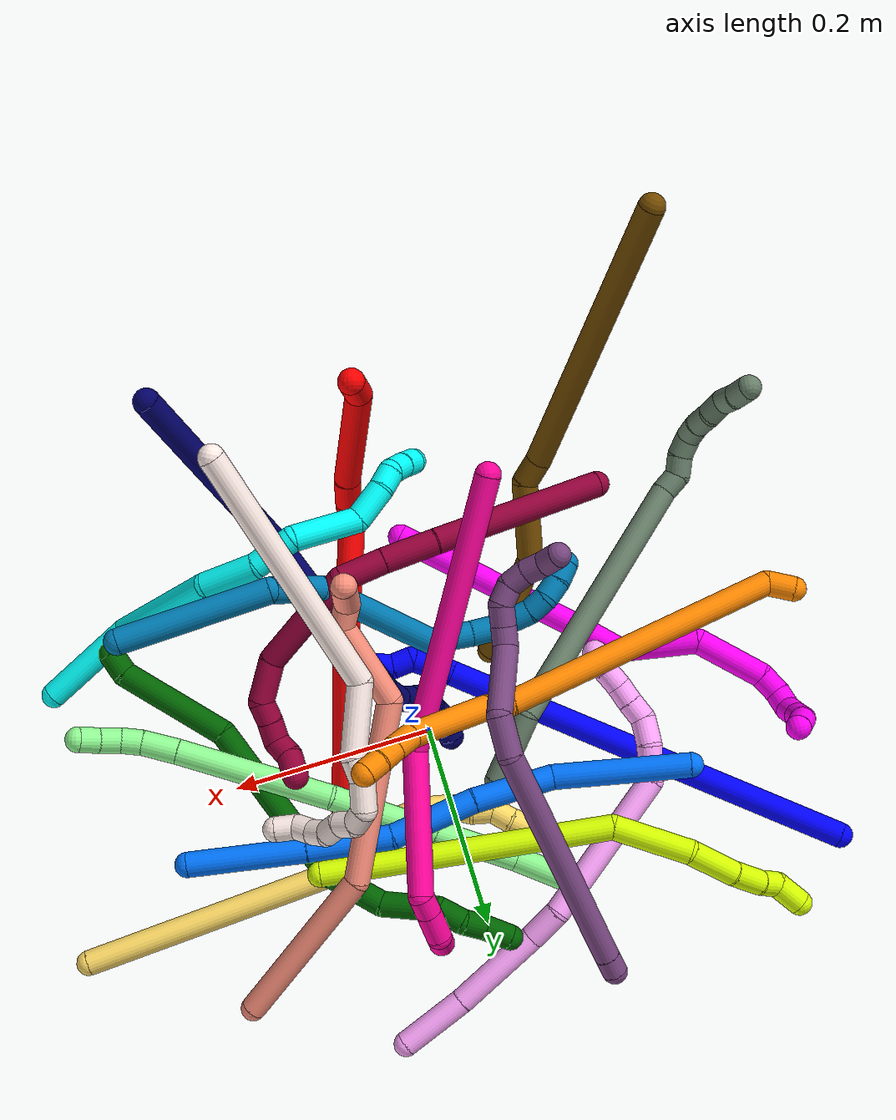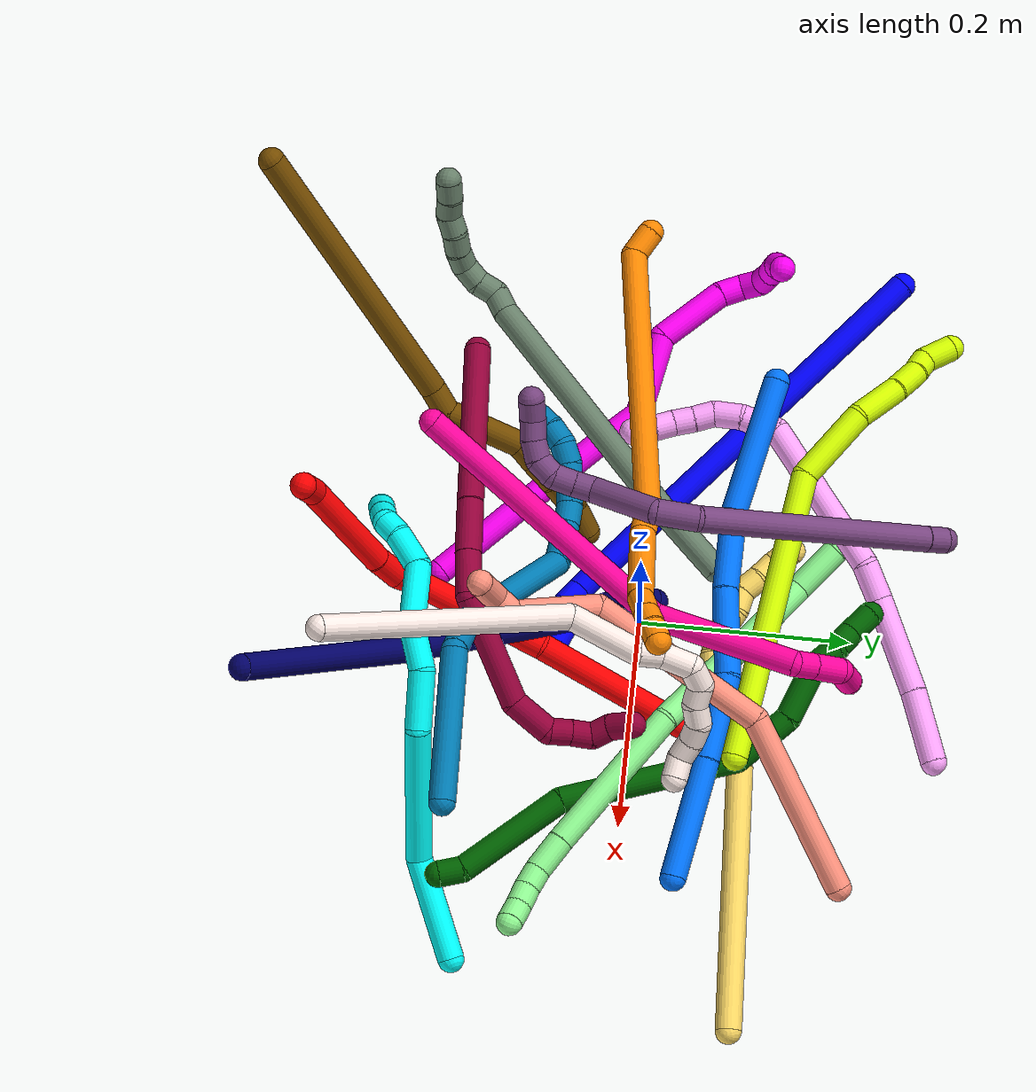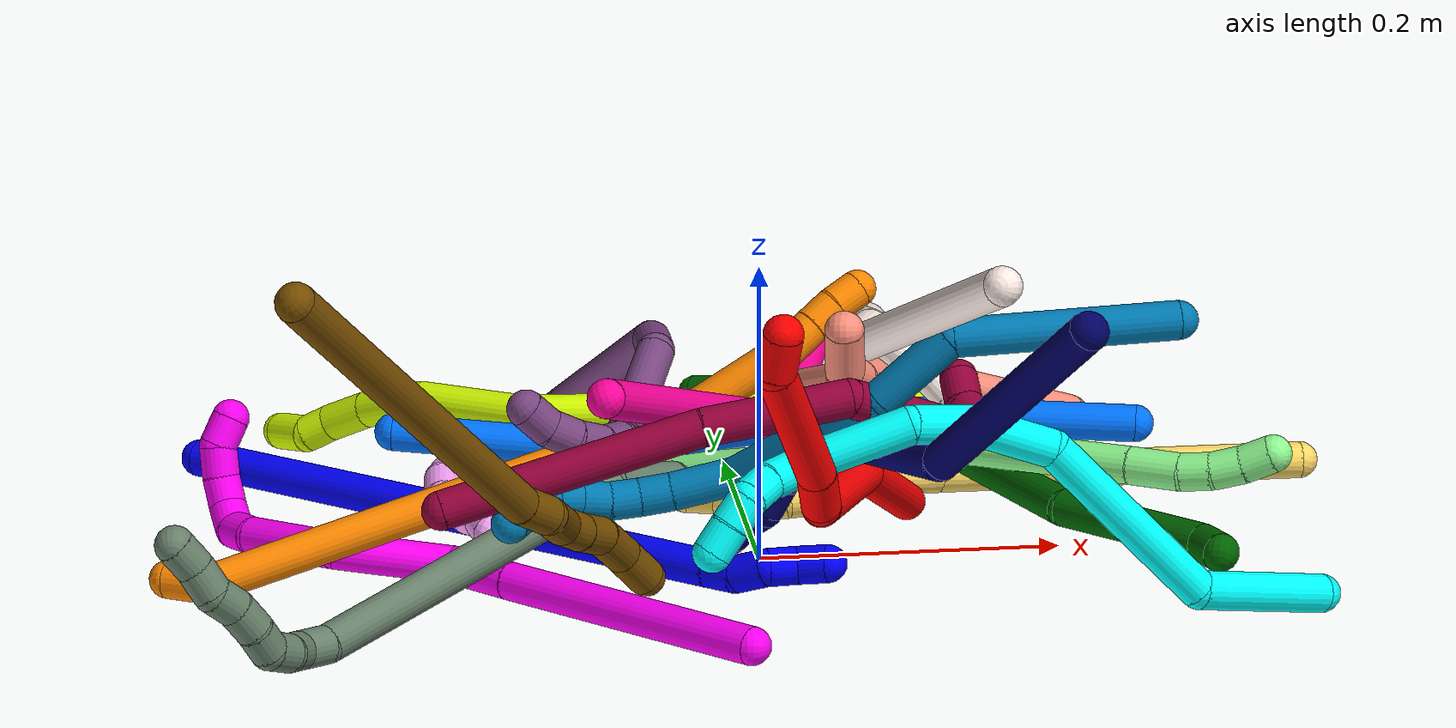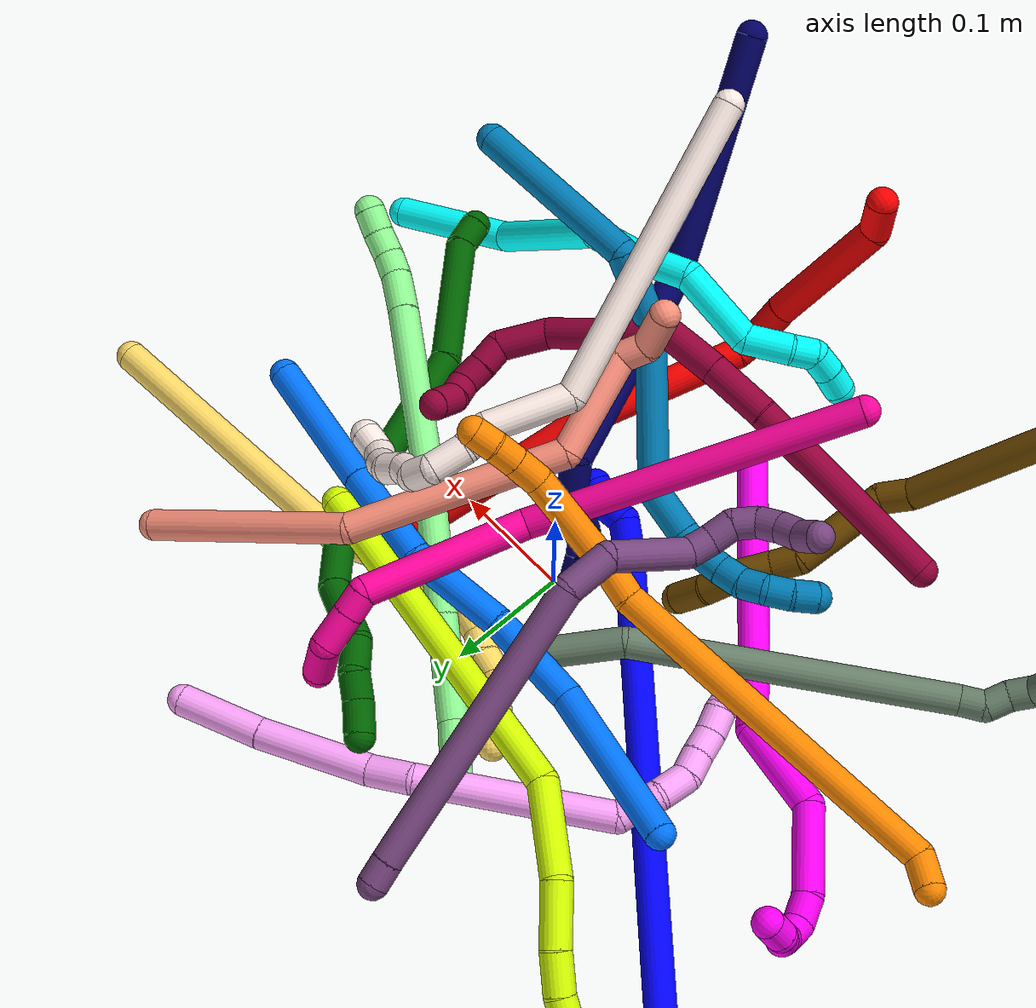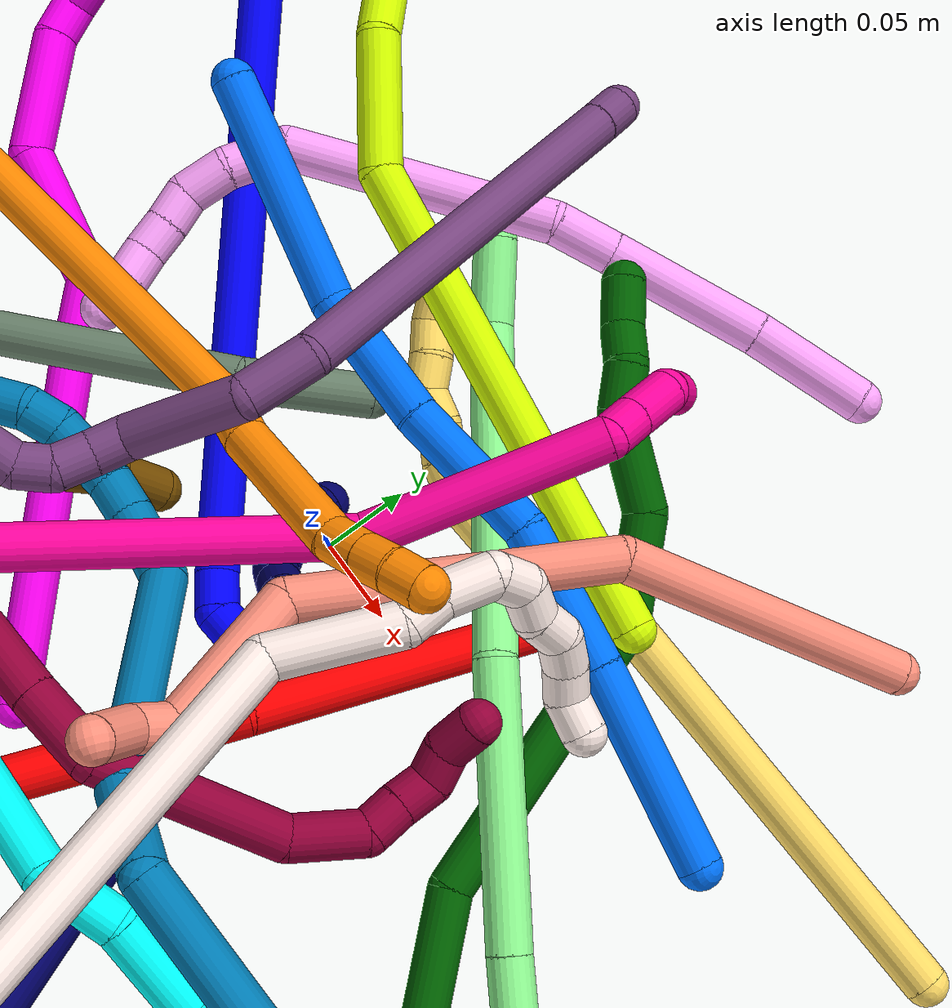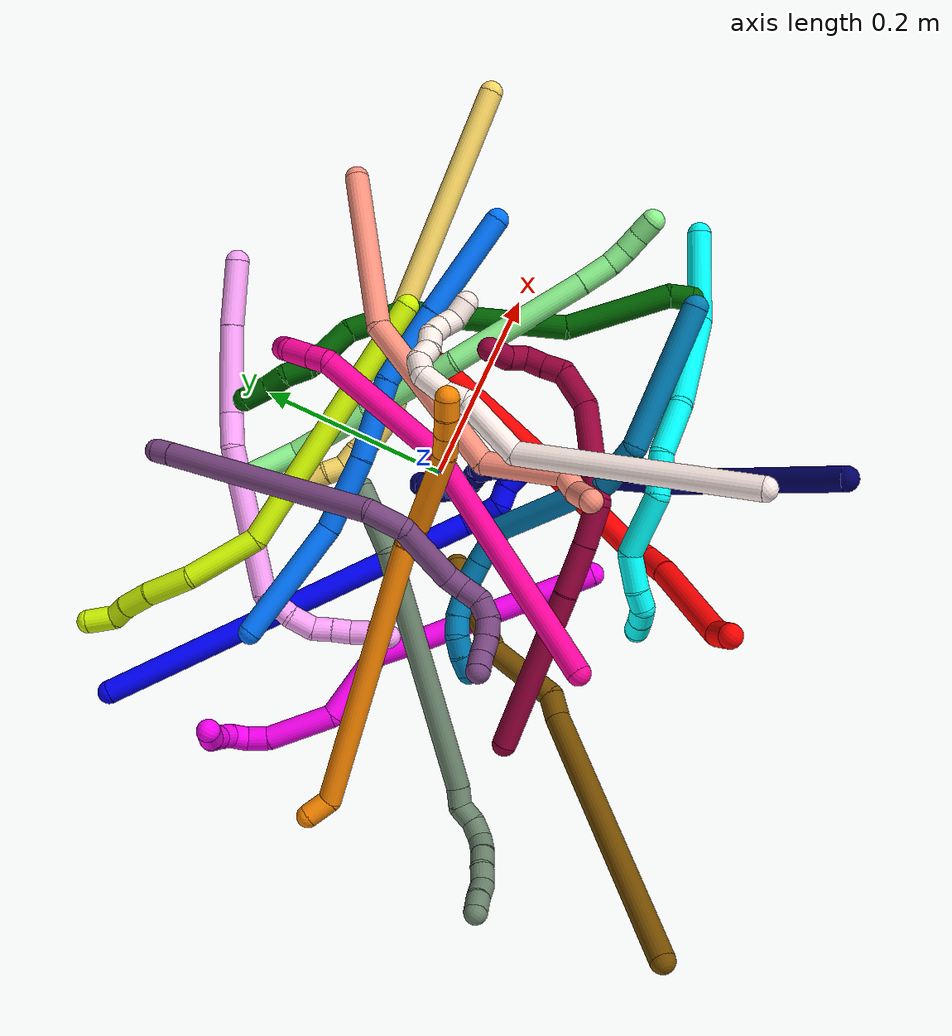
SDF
<sdf version="1.7">
 <world name="default">
  <plugin name="TubeGeneratorPlugin" filename="libtube_generator_plugin.so"/>
  <model name="photoneo_s_sensor">
   <static>1</static>
   <pose>0 0 2 1.57079 1.57079 3.14159</pose>
   <link name="link">
    <inertial><mass>0.1</mass></inertial>
    <sensor name="sensor" type="depth">
     <update_rate>30</update_rate>
     <camera>
      <horizontal_fov>1.22</horizontal_fov>
      <image><width>1920</width><height>1200</height><format>B8G8R8</format></image>
      <clip><near>0.1</near><far>4</far></clip>
      <depth_camera><output>points</output></depth_camera>
     </camera>
     <plugin name="camera_plugin" filename="libgazebo_ros_depth_camera.so">
      <baseline>0.2</baseline>
      <alwaysOn>1</alwaysOn>
      <updateRate>0.0</updateRate>
      <cameraName>camera_ir</cameraName>
      <imageTopicName>/camera/color/image_raw</imageTopicName>
      <cameraInfoTopicName>/camera/color/camera_info</cameraInfoTopicName>
      <depthImageTopicName>/camera/depth/image_raw</depthImageTopicName>
      <depthImageCameraInfoTopicName>/camera/depth/camera_info</depthImageCameraInfoTopicName>
      <pointCloudTopicName>/camera/depth/points</pointCloudTopicName>
      <frameName>fr_optical</frameName>
      <pointCloudCutoff>0.1</pointCloudCutoff>
      <pointCloudCutoffMax>2.0</pointCloudCutoffMax>
      <distortionK1>0</distortionK1>
      <distortionK2>0</distortionK2>
      <distortionK3>0</distortionK3>
      <distortionT1>0</distortionT1>
      <distortionT2>0</distortionT2>
      <CxPrime>0</CxPrime>
      <Cx>0</Cx>
      <Cy>0</Cy>
      <focalLength>0</focalLength>
      <hackBaseline>0</hackBaseline>
     </plugin>
    </sensor>
   </link>
  </model>
  <gravity>0 0 -9.8</gravity>
  <magnetic_field>6e-06 2.3e-05 -4.2e-05</magnetic_field>
  <atmosphere type="adiabatic"/>
  <physics name="default_physics" default="0" type="ode">
   <max_step_size>0.003</max_step_size>
   <real_time_factor>1</real_time_factor>
   <real_time_update_rate>1000</real_time_update_rate>
   <max_contacts>10000</max_contacts>
   <ode>
    <solver>
     <type>quick</type>
     <iters>100</iters>
     <sor>1.3</sor>
     <use_dynamic_moi_rescaling>0</use_dynamic_moi_rescaling>
    </solver>
    <constraints>
     <contact_max_correcting_vel>0</contact_max_correcting_vel>
     <contact_surface_layer>0.001</contact_surface_layer>
     <cfm>0</cfm>
     <erp>0.2</erp>
    </constraints>
   </ode>
  </physics>
  <scene><ambient>0.4 0.4 0.4 1</ambient><background>0.7 0.7 0.7 1</background><shadows>0</shadows></scene>
  <audio><device>default</device></audio>
  <spherical_coordinates>
   <surface_model>EARTH_WGS84</surface_model>
   <latitude_deg>0</latitude_deg>
   <longitude_deg>0</longitude_deg>
   <elevation>0</elevation>
   <heading_deg>0</heading_deg>
  </spherical_coordinates>
  <model name="bin">
   <static>1</static>
   <link name="bottom">
    <collision name="collision-bottom">
     <pose>0 0 -0.01 0 -0 0</pose>
     <geometry><box><size>0.8 0.6 0.02</size></box></geometry>
     <surface>
      <friction><ode><mu>100</mu><mu2>100</mu2></ode></friction>
      <contact><collide_bitmask>65535</collide_bitmask></contact>
     </surface>
    </collision>
   </link>
   <link name="west_wall">
    <collision name="collision-west_wall">
     <pose>-0.41 0 0.1 0 -0 0</pose>
     <geometry><box><size>0.02 0.6 0.2</size></box></geometry>
     <surface>
      <friction><ode><mu>100</mu><mu2>100</mu2></ode></friction>
      <contact><collide_bitmask>65535</collide_bitmask></contact>
     </surface>
    </collision>
   </link>
   <link name="east_wall">
    <collision name="collision-east_wall">
     <pose>0.41 0 0.1 0 -0 0</pose>
     <geometry><box><size>0.02 0.6 0.2</size></box></geometry>
     <surface>
      <friction><ode><mu>100</mu><mu2>100</mu2></ode></friction>
      <contact><collide_bitmask>65535</collide_bitmask></contact>
     </surface>
    </collision>
   </link>
   <link name="south_wall">
    <collision name="collision-south_wall">
     <pose>0 -0.31 0.1 0 -0 0</pose>
     <geometry><box><size>0.8 0.02 0.2</size></box></geometry>
     <surface>
      <friction><ode><mu>100</mu><mu2>100</mu2></ode></friction>
      <contact><collide_bitmask>65535</collide_bitmask></contact>
     </surface>
    </collision>
   </link>
   <link name="north_wall">
    <collision name="collision-north_wall">
     <pose>0 0.31 0.1 0 -0 0</pose>
     <geometry><box><size>0.8 0.02 0.2</size></box></geometry>
     <surface>
      <friction><ode><mu>100</mu><mu2>100</mu2></ode></friction>
      <contact><collide_bitmask>65535</collide_bitmask></contact>
     </surface>
    </collision>
   </link>
  </model>
  <model name="1">
   <static>0</static>
   <link name="1">
    <collision name="collision-cylinder-e_1_1_4">
     <pose>0.159517 -0.130826 -0.02363 1.74949 0.876014 1.02177</pose>
     <geometry><cylinder><radius>0.0125</radius><length>0.415306</length></cylinder></geometry>
     <surface>
      <friction><ode><mu>1.16</mu><mu2>1.16</mu2><slip1>0</slip1><slip2>0</slip2></ode></friction>
      <contact><ode><kp>1e+06</kp><kd>1</kd><max_vel>0</max_vel><min_depth>0.001</min_depth></ode></contact>
     </surface>
    </collision>
    <visual name="visual-cylinder-e_1_1_4">
     <pose>0.159517 -0.130826 -0.02363 1.74949 0.876014 1.02177</pose>
     <geometry><cylinder><radius>0.0125</radius><length>0.415306</length></cylinder></geometry>
     <material><ambient>0 0 1 1</ambient></material>
    </visual>
    <collision name="collision-cylinder-e_2_4_5">
     <pose>0.326929 -0.268099 -0.048311 1.73226 0.879559 1.01082</pose>
     <geometry><cylinder><radius>0.0125</radius><length>0.020492</length></cylinder></geometry>
     <surface>
      <friction><ode><mu>1.16</mu><mu2>1.16</mu2><slip1>0</slip1><slip2>0</slip2></ode></friction>
      <contact><ode><kp>1e+06</kp><kd>1</kd><max_vel>0</max_vel><min_depth>0.001</min_depth></ode></contact>
     </surface>
    </collision>
    <visual name="visual-cylinder-e_2_4_5">
     <pose>0.326929 -0.268099 -0.048311 1.73226 0.879559 1.01082</pose>
     <geometry><cylinder><radius>0.0125</radius><length>0.020492</length></cylinder></geometry>
     <material><ambient>0 0 1 1</ambient></material>
    </visual>
    <collision name="collision-cylinder-e_3_5_6">
     <pose>0.341251 -0.284482 -0.048433 1.47765 0.572252 0.523687</pose>
     <geometry><cylinder><radius>0.0125</radius><length>0.023741</length></cylinder></geometry>
     <surface>
      <friction><ode><mu>1.16</mu><mu2>1.16</mu2><slip1>0</slip1><slip2>0</slip2></ode></friction>
      <contact><ode><kp>1e+06</kp><kd>1</kd><max_vel>0</max_vel><min_depth>0.001</min_depth></ode></contact>
     </surface>
    </collision>
    <visual name="visual-cylinder-e_3_5_6">
     <pose>0.341251 -0.284482 -0.048433 1.47765 0.572252 0.523687</pose>
     <geometry><cylinder><radius>0.0125</radius><length>0.023741</length></cylinder></geometry>
     <material><ambient>0 0 1 1</ambient></material>
    </visual>
    <collision name="collision-cylinder-e_4_6_7">
     <pose>0.354846 -0.298239 -0.041424 0.561123 0.784369 0.237255</pose>
     <geometry><cylinder><radius>0.0125</radius><length>0.020291</length></cylinder></geometry>
     <surface>
      <friction><ode><mu>1.16</mu><mu2>1.16</mu2><slip1>0</slip1><slip2>0</slip2></ode></friction>
      <contact><ode><kp>1e+06</kp><kd>1</kd><max_vel>0</max_vel><min_depth>0.001</min_depth></ode></contact>
     </surface>
    </collision>
    <visual name="visual-cylinder-e_4_6_7">
     <pose>0.354846 -0.298239 -0.041424 0.561123 0.784369 0.237255</pose>
     <geometry><cylinder><radius>0.0125</radius><length>0.020291</length></cylinder></geometry>
     <material><ambient>0 0 1 1</ambient></material>
    </visual>
    <collision name="collision-cylinder-e_5_7_2">
     <pose>0.369249 -0.308569 -0.032702 1.18511 0.800223 0.554795</pose>
     <geometry><cylinder><radius>0.0125</radius><length>0.020171</length></cylinder></geometry>
     <surface>
      <friction><ode><mu>1.16</mu><mu2>1.16</mu2><slip1>0</slip1><slip2>0</slip2></ode></friction>
      <contact><ode><kp>1e+06</kp><kd>1</kd><max_vel>0</max_vel><min_depth>0.001</min_depth></ode></contact>
     </surface>
    </collision>
    <visual name="visual-cylinder-e_5_7_2">
     <pose>0.369249 -0.308569 -0.032702 1.18511 0.800223 0.554795</pose>
     <geometry><cylinder><radius>0.0125</radius><length>0.020171</length></cylinder></geometry>
     <material><ambient>0 0 1 1</ambient></material>
    </visual>
    <collision name="collision-sphere-2">
     <pose>0.376485 -0.315078 -0.030059 0 -0 0</pose>
     <geometry><sphere><radius>0.0125</radius></sphere></geometry>
     <surface>
      <friction><ode><mu>1.16</mu><mu2>1.16</mu2><slip1>0</slip1><slip2>0</slip2></ode></friction>
      <contact><ode><kp>1e+06</kp><kd>1</kd><max_vel>0</max_vel><min_depth>0.001</min_depth></ode></contact>
     </surface>
    </collision>
    <visual name="visual-sphere-2">
     <pose>0.376485 -0.315078 -0.030059 0 -0 0</pose>
     <geometry><sphere><radius>0.0125</radius></sphere></geometry>
     <material><ambient>0 0 1 1</ambient></material>
    </visual>
    <collision name="collision-sphere-7">
     <pose>0.362012 -0.30206 -0.035344 0 -0 0</pose>
     <geometry><sphere><radius>0.0125</radius></sphere></geometry>
     <surface>
      <friction><ode><mu>1.16</mu><mu2>1.16</mu2><slip1>0</slip1><slip2>0</slip2></ode></friction>
      <contact><ode><kp>1e+06</kp><kd>1</kd><max_vel>0</max_vel><min_depth>0.001</min_depth></ode></contact>
     </surface>
    </collision>
    <visual name="visual-sphere-7">
     <pose>0.362012 -0.30206 -0.035344 0 -0 0</pose>
     <geometry><sphere><radius>0.0125</radius></sphere></geometry>
     <material><ambient>0 0 1 1</ambient></material>
    </visual>
    <collision name="collision-sphere-6">
     <pose>0.347679 -0.294417 -0.047504 0 -0 0</pose>
     <geometry><sphere><radius>0.0125</radius></sphere></geometry>
     <surface>
      <friction><ode><mu>1.16</mu><mu2>1.16</mu2><slip1>0</slip1><slip2>0</slip2></ode></friction>
      <contact><ode><kp>1e+06</kp><kd>1</kd><max_vel>0</max_vel><min_depth>0.001</min_depth></ode></contact>
     </surface>
    </collision>
    <visual name="visual-sphere-6">
     <pose>0.347679 -0.294417 -0.047504 0 -0 0</pose>
     <geometry><sphere><radius>0.0125</radius></sphere></geometry>
     <material><ambient>0 0 1 1</ambient></material>
    </visual>
    <collision name="collision-sphere-5">
     <pose>0.334823 -0.274546 -0.049361 0 -0 0</pose>
     <geometry><sphere><radius>0.0125</radius></sphere></geometry>
     <surface>
      <friction><ode><mu>1.16</mu><mu2>1.16</mu2><slip1>0</slip1><slip2>0</slip2></ode></friction>
      <contact><ode><kp>1e+06</kp><kd>1</kd><max_vel>0</max_vel><min_depth>0.001</min_depth></ode></contact>
     </surface>
    </collision>
    <visual name="visual-sphere-5">
     <pose>0.334823 -0.274546 -0.049361 0 -0 0</pose>
     <geometry><sphere><radius>0.0125</radius></sphere></geometry>
     <material><ambient>0 0 1 1</ambient></material>
    </visual>
    <collision name="collision-sphere-1">
     <geometry><sphere><radius>0.0125</radius></sphere></geometry>
     <surface>
      <friction><ode><mu>1.16</mu><mu2>1.16</mu2><slip1>0</slip1><slip2>0</slip2></ode></friction>
      <contact><ode><kp>1e+06</kp><kd>1</kd><max_vel>0</max_vel><min_depth>0.001</min_depth></ode></contact>
     </surface>
    </collision>
    <visual name="visual-sphere-1">
     <geometry><sphere><radius>0.0125</radius></sphere></geometry>
     <material><ambient>0 0 1 1</ambient></material>
    </visual>
    <collision name="collision-sphere-4">
     <pose>0.319035 -0.261652 -0.047261 0 -0 0</pose>
     <geometry><sphere><radius>0.0125</radius></sphere></geometry>
     <surface>
      <friction><ode><mu>1.16</mu><mu2>1.16</mu2><slip1>0</slip1><slip2>0</slip2></ode></friction>
      <contact><ode><kp>1e+06</kp><kd>1</kd><max_vel>0</max_vel><min_depth>0.001</min_depth></ode></contact>
     </surface>
    </collision>
    <visual name="visual-sphere-4">
     <pose>0.319035 -0.261652 -0.047261 0 -0 0</pose>
     <geometry><sphere><radius>0.0125</radius></sphere></geometry>
     <material><ambient>0 0 1 1</ambient></material>
    </visual>
    <inertial>
     <pose>0.191395 -0.157712 -0.026908 0 -0 0</pose>
     <mass>0.5</mass>
     <inertia>
      <ixx>0.005304</ixx>
      <ixy>0</ixy>
      <ixz>0</ixz>
      <iyy>0.006555</iyy>
      <iyz>0</iyz>
      <izz>-0.00083</izz>
     </inertia>
    </inertial>
   </link>
   <pose>-0.358455 0.217861 0.011495 -1.28395 0.640028 -0.400552</pose>
  </model>
  <model name="2">
   <static>0</static>
   <link name="2">
    <collision name="collision-cylinder-e_1_1_4">
     <pose>-0.014333 -0.024493 0.085113 0.280201 -0.160437 -0.022673</pose>
     <geometry><cylinder><radius>0.0125</radius><length>0.179439</length></cylinder></geometry>
     <surface>
      <friction><ode><mu>1.16</mu><mu2>1.16</mu2><slip1>0</slip1><slip2>0</slip2></ode></friction>
      <contact><ode><kp>1e+06</kp><kd>1</kd><max_vel>0</max_vel><min_depth>0.001</min_depth></ode></contact>
     </surface>
    </collision>
    <visual name="visual-cylinder-e_1_1_4">
     <pose>-0.014333 -0.024493 0.085113 0.280201 -0.160437 -0.022673</pose>
     <geometry><cylinder><radius>0.0125</radius><length>0.179439</length></cylinder></geometry>
     <material><ambient>1 0 0 1</ambient></material>
    </visual>
    <collision name="collision-cylinder-e_2_4_5">
     <pose>-0.025159 -0.056269 0.235091 0.111807 0.053669 0.003004</pose>
     <geometry><cylinder><radius>0.0125</radius><length>0.130732</length></cylinder></geometry>
     <surface>
      <friction><ode><mu>1.16</mu><mu2>1.16</mu2><slip1>0</slip1><slip2>0</slip2></ode></friction>
      <contact><ode><kp>1e+06</kp><kd>1</kd><max_vel>0</max_vel><min_depth>0.001</min_depth></ode></contact>
     </surface>
    </collision>
    <visual name="visual-cylinder-e_2_4_5">
     <pose>-0.025159 -0.056269 0.235091 0.111807 0.053669 0.003004</pose>
     <geometry><cylinder><radius>0.0125</radius><length>0.130732</length></cylinder></geometry>
     <material><ambient>1 0 0 1</ambient></material>
    </visual>
    <collision name="collision-cylinder-e_3_5_6">
     <pose>-0.024023 -0.064759 0.30961 0.124432 -0.238934 -0.014956</pose>
     <geometry><cylinder><radius>0.0125</radius><length>0.020029</length></cylinder></geometry>
     <surface>
      <friction><ode><mu>1.16</mu><mu2>1.16</mu2><slip1>0</slip1><slip2>0</slip2></ode></friction>
      <contact><ode><kp>1e+06</kp><kd>1</kd><max_vel>0</max_vel><min_depth>0.001</min_depth></ode></contact>
     </surface>
    </collision>
    <visual name="visual-cylinder-e_3_5_6">
     <pose>-0.024023 -0.064759 0.30961 0.124432 -0.238934 -0.014956</pose>
     <geometry><cylinder><radius>0.0125</radius><length>0.020029</length></cylinder></geometry>
     <material><ambient>1 0 0 1</ambient></material>
    </visual>
    <collision name="collision-cylinder-e_4_6_7">
     <pose>-0.034705 -0.075048 0.330536 0.67818 -0.521323 -0.187606</pose>
     <geometry><cylinder><radius>0.0125</radius><length>0.033383</length></cylinder></geometry>
     <surface>
      <friction><ode><mu>1.16</mu><mu2>1.16</mu2><slip1>0</slip1><slip2>0</slip2></ode></friction>
      <contact><ode><kp>1e+06</kp><kd>1</kd><max_vel>0</max_vel><min_depth>0.001</min_depth></ode></contact>
     </surface>
    </collision>
    <visual name="visual-cylinder-e_4_6_7">
     <pose>-0.034705 -0.075048 0.330536 0.67818 -0.521323 -0.187606</pose>
     <geometry><cylinder><radius>0.0125</radius><length>0.033383</length></cylinder></geometry>
     <material><ambient>1 0 0 1</ambient></material>
    </visual>
    <collision name="collision-cylinder-e_5_7_8">
     <pose>-0.063708 -0.117643 0.378896 0.734814 -0.392433 -0.152712</pose>
     <geometry><cylinder><radius>0.0125</radius><length>0.1082</length></cylinder></geometry>
     <surface>
      <friction><ode><mu>1.16</mu><mu2>1.16</mu2><slip1>0</slip1><slip2>0</slip2></ode></friction>
      <contact><ode><kp>1e+06</kp><kd>1</kd><max_vel>0</max_vel><min_depth>0.001</min_depth></ode></contact>
     </surface>
    </collision>
    <visual name="visual-cylinder-e_5_7_8">
     <pose>-0.063708 -0.117643 0.378896 0.734814 -0.392433 -0.152712</pose>
     <geometry><cylinder><radius>0.0125</radius><length>0.1082</length></cylinder></geometry>
     <material><ambient>1 0 0 1</ambient></material>
    </visual>
    <collision name="collision-cylinder-e_6_8_2">
     <pose>-0.095397 -0.158464 0.420952 0.973735 -0.893972 -0.497011</pose>
     <geometry><cylinder><radius>0.0125</radius><length>0.028217</length></cylinder></geometry>
     <surface>
      <friction><ode><mu>1.16</mu><mu2>1.16</mu2><slip1>0</slip1><slip2>0</slip2></ode></friction>
      <contact><ode><kp>1e+06</kp><kd>1</kd><max_vel>0</max_vel><min_depth>0.001</min_depth></ode></contact>
     </surface>
    </collision>
    <visual name="visual-cylinder-e_6_8_2">
     <pose>-0.095397 -0.158464 0.420952 0.973735 -0.893972 -0.497011</pose>
     <geometry><cylinder><radius>0.0125</radius><length>0.028217</length></cylinder></geometry>
     <material><ambient>1 0 0 1</ambient></material>
    </visual>
    <collision name="collision-sphere-2">
     <pose>-0.106395 -0.165772 0.42592 0 -0 0</pose>
     <geometry><sphere><radius>0.0125</radius></sphere></geometry>
     <surface>
      <friction><ode><mu>1.16</mu><mu2>1.16</mu2><slip1>0</slip1><slip2>0</slip2></ode></friction>
      <contact><ode><kp>1e+06</kp><kd>1</kd><max_vel>0</max_vel><min_depth>0.001</min_depth></ode></contact>
     </surface>
    </collision>
    <visual name="visual-sphere-2">
     <pose>-0.106395 -0.165772 0.42592 0 -0 0</pose>
     <geometry><sphere><radius>0.0125</radius></sphere></geometry>
     <material><ambient>1 0 0 1</ambient></material>
    </visual>
    <collision name="collision-sphere-4">
     <pose>-0.028665 -0.048986 0.170227 0 -0 0</pose>
     <geometry><sphere><radius>0.0125</radius></sphere></geometry>
     <surface>
      <friction><ode><mu>1.16</mu><mu2>1.16</mu2><slip1>0</slip1><slip2>0</slip2></ode></friction>
      <contact><ode><kp>1e+06</kp><kd>1</kd><max_vel>0</max_vel><min_depth>0.001</min_depth></ode></contact>
     </surface>
    </collision>
    <visual name="visual-sphere-4">
     <pose>-0.028665 -0.048986 0.170227 0 -0 0</pose>
     <geometry><sphere><radius>0.0125</radius></sphere></geometry>
     <material><ambient>1 0 0 1</ambient></material>
    </visual>
    <collision name="collision-sphere-1">
     <geometry><sphere><radius>0.0125</radius></sphere></geometry>
     <surface>
      <friction><ode><mu>1.16</mu><mu2>1.16</mu2><slip1>0</slip1><slip2>0</slip2></ode></friction>
      <contact><ode><kp>1e+06</kp><kd>1</kd><max_vel>0</max_vel><min_depth>0.001</min_depth></ode></contact>
     </surface>
    </collision>
    <visual name="visual-sphere-1">
     <geometry><sphere><radius>0.0125</radius></sphere></geometry>
     <material><ambient>1 0 0 1</ambient></material>
    </visual>
    <collision name="collision-sphere-8">
     <pose>-0.084398 -0.151157 0.415984 0 -0 0</pose>
     <geometry><sphere><radius>0.0125</radius></sphere></geometry>
     <surface>
      <friction><ode><mu>1.16</mu><mu2>1.16</mu2><slip1>0</slip1><slip2>0</slip2></ode></friction>
      <contact><ode><kp>1e+06</kp><kd>1</kd><max_vel>0</max_vel><min_depth>0.001</min_depth></ode></contact>
     </surface>
    </collision>
    <visual name="visual-sphere-8">
     <pose>-0.084398 -0.151157 0.415984 0 -0 0</pose>
     <geometry><sphere><radius>0.0125</radius></sphere></geometry>
     <material><ambient>1 0 0 1</ambient></material>
    </visual>
    <collision name="collision-sphere-5">
     <pose>-0.021652 -0.063552 0.299955 0 -0 0</pose>
     <geometry><sphere><radius>0.0125</radius></sphere></geometry>
     <surface>
      <friction><ode><mu>1.16</mu><mu2>1.16</mu2><slip1>0</slip1><slip2>0</slip2></ode></friction>
      <contact><ode><kp>1e+06</kp><kd>1</kd><max_vel>0</max_vel><min_depth>0.001</min_depth></ode></contact>
     </surface>
    </collision>
    <visual name="visual-sphere-5">
     <pose>-0.021652 -0.063552 0.299955 0 -0 0</pose>
     <geometry><sphere><radius>0.0125</radius></sphere></geometry>
     <material><ambient>1 0 0 1</ambient></material>
    </visual>
    <collision name="collision-sphere-6">
     <pose>-0.026393 -0.065967 0.319264 0 -0 0</pose>
     <geometry><sphere><radius>0.0125</radius></sphere></geometry>
     <surface>
      <friction><ode><mu>1.16</mu><mu2>1.16</mu2><slip1>0</slip1><slip2>0</slip2></ode></friction>
      <contact><ode><kp>1e+06</kp><kd>1</kd><max_vel>0</max_vel><min_depth>0.001</min_depth></ode></contact>
     </surface>
    </collision>
    <visual name="visual-sphere-6">
     <pose>-0.026393 -0.065967 0.319264 0 -0 0</pose>
     <geometry><sphere><radius>0.0125</radius></sphere></geometry>
     <material><ambient>1 0 0 1</ambient></material>
    </visual>
    <collision name="collision-sphere-7">
     <pose>-0.043018 -0.084129 0.341807 0 -0 0</pose>
     <geometry><sphere><radius>0.0125</radius></sphere></geometry>
     <surface>
      <friction><ode><mu>1.16</mu><mu2>1.16</mu2><slip1>0</slip1><slip2>0</slip2></ode></friction>
      <contact><ode><kp>1e+06</kp><kd>1</kd><max_vel>0</max_vel><min_depth>0.001</min_depth></ode></contact>
     </surface>
    </collision>
    <visual name="visual-sphere-7">
     <pose>-0.043018 -0.084129 0.341807 0 -0 0</pose>
     <geometry><sphere><radius>0.0125</radius></sphere></geometry>
     <material><ambient>1 0 0 1</ambient></material>
    </visual>
    <inertial>
     <pose>-0.034171 -0.065508 0.232233 0 -0 0</pose>
     <mass>0.5</mass>
     <inertia>
      <ixx>0.000744</ixx>
      <ixy>0</ixy>
      <ixz>0</ixz>
      <iyy>0.000712</iyy>
      <iyz>0</iyz>
      <izz>0.000375</izz>
     </inertia>
    </inertial>
   </link>
   <pose>0.108281 0.068476 0.011496 -1.40272 0.781808 3.0295</pose>
  </model>
  <model name="3">
   <static>0</static>
   <link name="3">
    <collision name="collision-cylinder-e_1_1_4">
     <pose>-0.010593 -0.004497 -0.047782 3.04775 -0.217234 -2.32841</pose>
     <geometry><cylinder><radius>0.0125</radius><length>0.098297</length></cylinder></geometry>
     <surface>
      <friction><ode><mu>1.16</mu><mu2>1.16</mu2><slip1>0</slip1><slip2>0</slip2></ode></friction>
      <contact><ode><kp>1e+06</kp><kd>1</kd><max_vel>0</max_vel><min_depth>0.001</min_depth></ode></contact>
     </surface>
    </collision>
    <visual name="visual-cylinder-e_1_1_4">
     <pose>-0.010593 -0.004497 -0.047782 3.04775 -0.217234 -2.32841</pose>
     <geometry><cylinder><radius>0.0125</radius><length>0.098297</length></cylinder></geometry>
     <material><ambient>0.003922 1 0.996078 1</ambient></material>
    </visual>
    <collision name="collision-cylinder-e_2_4_5">
     <pose>-0.071892 -0.02963 -0.139286 2.70061 -0.809216 -2.17721</pose>
     <geometry><cylinder><radius>0.0125</radius><length>0.140121</length></cylinder></geometry>
     <surface>
      <friction><ode><mu>1.16</mu><mu2>1.16</mu2><slip1>0</slip1><slip2>0</slip2></ode></friction>
      <contact><ode><kp>1e+06</kp><kd>1</kd><max_vel>0</max_vel><min_depth>0.001</min_depth></ode></contact>
     </surface>
    </collision>
    <visual name="visual-cylinder-e_2_4_5">
     <pose>-0.071892 -0.02963 -0.139286 2.70061 -0.809216 -2.17721</pose>
     <geometry><cylinder><radius>0.0125</radius><length>0.140121</length></cylinder></geometry>
     <material><ambient>0.003922 1 0.996078 1</ambient></material>
    </visual>
    <collision name="collision-cylinder-e_3_5_6">
     <pose>-0.137624 -0.048182 -0.206108 -3.05164 -0.574841 2.8394</pose>
     <geometry><cylinder><radius>0.0125</radius><length>0.055274</length></cylinder></geometry>
     <surface>
      <friction><ode><mu>1.16</mu><mu2>1.16</mu2><slip1>0</slip1><slip2>0</slip2></ode></friction>
      <contact><ode><kp>1e+06</kp><kd>1</kd><max_vel>0</max_vel><min_depth>0.001</min_depth></ode></contact>
     </surface>
    </collision>
    <visual name="visual-cylinder-e_3_5_6">
     <pose>-0.137624 -0.048182 -0.206108 -3.05164 -0.574841 2.8394</pose>
     <geometry><cylinder><radius>0.0125</radius><length>0.055274</length></cylinder></geometry>
     <material><ambient>0.003922 1 0.996078 1</ambient></material>
    </visual>
    <collision name="collision-cylinder-e_4_6_7">
     <pose>-0.157536 -0.04578 -0.250022 -3.12632 -0.230517 3.00985</pose>
     <geometry><cylinder><radius>0.0125</radius><length>0.04276</length></cylinder></geometry>
     <surface>
      <friction><ode><mu>1.16</mu><mu2>1.16</mu2><slip1>0</slip1><slip2>0</slip2></ode></friction>
      <contact><ode><kp>1e+06</kp><kd>1</kd><max_vel>0</max_vel><min_depth>0.001</min_depth></ode></contact>
     </surface>
    </collision>
    <visual name="visual-cylinder-e_4_6_7">
     <pose>-0.157536 -0.04578 -0.250022 -3.12632 -0.230517 3.00985</pose>
     <geometry><cylinder><radius>0.0125</radius><length>0.04276</length></cylinder></geometry>
     <material><ambient>0.003922 1 0.996078 1</ambient></material>
    </visual>
    <collision name="collision-cylinder-e_5_7_8">
     <pose>-0.164787 -0.028272 -0.298971 -2.59316 -0.071633 0.253392</pose>
     <geometry><cylinder><radius>0.0125</radius><length>0.066115</length></cylinder></geometry>
     <surface>
      <friction><ode><mu>1.16</mu><mu2>1.16</mu2><slip1>0</slip1><slip2>0</slip2></ode></friction>
      <contact><ode><kp>1e+06</kp><kd>1</kd><max_vel>0</max_vel><min_depth>0.001</min_depth></ode></contact>
     </surface>
    </collision>
    <visual name="visual-cylinder-e_5_7_8">
     <pose>-0.164787 -0.028272 -0.298971 -2.59316 -0.071633 0.253392</pose>
     <geometry><cylinder><radius>0.0125</radius><length>0.066115</length></cylinder></geometry>
     <material><ambient>0.003922 1 0.996078 1</ambient></material>
    </visual>
    <collision name="collision-cylinder-e_6_8_9">
     <pose>-0.163927 -0.011719 -0.345457 3.10683 0.17392 2.74802</pose>
     <geometry><cylinder><radius>0.0125</radius><length>0.037282</length></cylinder></geometry>
     <surface>
      <friction><ode><mu>1.16</mu><mu2>1.16</mu2><slip1>0</slip1><slip2>0</slip2></ode></friction>
      <contact><ode><kp>1e+06</kp><kd>1</kd><max_vel>0</max_vel><min_depth>0.001</min_depth></ode></contact>
     </surface>
    </collision>
    <visual name="visual-cylinder-e_6_8_9">
     <pose>-0.163927 -0.011719 -0.345457 3.10683 0.17392 2.74802</pose>
     <geometry><cylinder><radius>0.0125</radius><length>0.037282</length></cylinder></geometry>
     <material><ambient>0.003922 1 0.996078 1</ambient></material>
    </visual>
    <collision name="collision-cylinder-e_7_9_10">
     <pose>-0.156824 -0.012497 -0.373025 3.12644 0.398062 3.06649</pose>
     <geometry><cylinder><radius>0.0125</radius><length>0.020003</length></cylinder></geometry>
     <surface>
      <friction><ode><mu>1.16</mu><mu2>1.16</mu2><slip1>0</slip1><slip2>0</slip2></ode></friction>
      <contact><ode><kp>1e+06</kp><kd>1</kd><max_vel>0</max_vel><min_depth>0.001</min_depth></ode></contact>
     </surface>
    </collision>
    <visual name="visual-cylinder-e_7_9_10">
     <pose>-0.156824 -0.012497 -0.373025 3.12644 0.398062 3.06649</pose>
     <geometry><cylinder><radius>0.0125</radius><length>0.020003</length></cylinder></geometry>
     <material><ambient>0.003922 1 0.996078 1</ambient></material>
    </visual>
    <collision name="collision-cylinder-e_8_10_11">
     <pose>-0.147939 -0.006876 -0.38879 -2.42001 0.521306 -1.2307</pose>
     <geometry><cylinder><radius>0.0125</radius><length>0.020112</length></cylinder></geometry>
     <surface>
      <friction><ode><mu>1.16</mu><mu2>1.16</mu2><slip1>0</slip1><slip2>0</slip2></ode></friction>
      <contact><ode><kp>1e+06</kp><kd>1</kd><max_vel>0</max_vel><min_depth>0.001</min_depth></ode></contact>
     </surface>
    </collision>
    <visual name="visual-cylinder-e_8_10_11">
     <pose>-0.147939 -0.006876 -0.38879 -2.42001 0.521306 -1.2307</pose>
     <geometry><cylinder><radius>0.0125</radius><length>0.020112</length></cylinder></geometry>
     <material><ambient>0.003922 1 0.996078 1</ambient></material>
    </visual>
    <collision name="collision-cylinder-e_9_11_2">
     <pose>-0.137959 0.005338 -0.401164 -2.30518 0.519449 -1.07777</pose>
     <geometry><cylinder><radius>0.0125</radius><length>0.020034</length></cylinder></geometry>
     <surface>
      <friction><ode><mu>1.16</mu><mu2>1.16</mu2><slip1>0</slip1><slip2>0</slip2></ode></friction>
      <contact><ode><kp>1e+06</kp><kd>1</kd><max_vel>0</max_vel><min_depth>0.001</min_depth></ode></contact>
     </surface>
    </collision>
    <visual name="visual-cylinder-e_9_11_2">
     <pose>-0.137959 0.005338 -0.401164 -2.30518 0.519449 -1.07777</pose>
     <geometry><cylinder><radius>0.0125</radius><length>0.020034</length></cylinder></geometry>
     <material><ambient>0.003922 1 0.996078 1</ambient></material>
    </visual>
    <collision name="collision-sphere-2">
     <pose>-0.132986 0.011793 -0.406992 0 -0 0</pose>
     <geometry><sphere><radius>0.0125</radius></sphere></geometry>
     <surface>
      <friction><ode><mu>1.16</mu><mu2>1.16</mu2><slip1>0</slip1><slip2>0</slip2></ode></friction>
      <contact><ode><kp>1e+06</kp><kd>1</kd><max_vel>0</max_vel><min_depth>0.001</min_depth></ode></contact>
     </surface>
    </collision>
    <visual name="visual-sphere-2">
     <pose>-0.132986 0.011793 -0.406992 0 -0 0</pose>
     <geometry><sphere><radius>0.0125</radius></sphere></geometry>
     <material><ambient>0.003922 1 0.996078 1</ambient></material>
    </visual>
    <collision name="collision-sphere-11">
     <pose>-0.142931 -0.001116 -0.395337 0 -0 0</pose>
     <geometry><sphere><radius>0.0125</radius></sphere></geometry>
     <surface>
      <friction><ode><mu>1.16</mu><mu2>1.16</mu2><slip1>0</slip1><slip2>0</slip2></ode></friction>
      <contact><ode><kp>1e+06</kp><kd>1</kd><max_vel>0</max_vel><min_depth>0.001</min_depth></ode></contact>
     </surface>
    </collision>
    <visual name="visual-sphere-11">
     <pose>-0.142931 -0.001116 -0.395337 0 -0 0</pose>
     <geometry><sphere><radius>0.0125</radius></sphere></geometry>
     <material><ambient>0.003922 1 0.996078 1</ambient></material>
    </visual>
    <collision name="collision-sphere-10">
     <pose>-0.152947 -0.012637 -0.382243 0 -0 0</pose>
     <geometry><sphere><radius>0.0125</radius></sphere></geometry>
     <surface>
      <friction><ode><mu>1.16</mu><mu2>1.16</mu2><slip1>0</slip1><slip2>0</slip2></ode></friction>
      <contact><ode><kp>1e+06</kp><kd>1</kd><max_vel>0</max_vel><min_depth>0.001</min_depth></ode></contact>
     </surface>
    </collision>
    <visual name="visual-sphere-10">
     <pose>-0.152947 -0.012637 -0.382243 0 -0 0</pose>
     <geometry><sphere><radius>0.0125</radius></sphere></geometry>
     <material><ambient>0.003922 1 0.996078 1</ambient></material>
    </visual>
    <collision name="collision-sphere-9">
     <pose>-0.160701 -0.012357 -0.363806 0 -0 0</pose>
     <geometry><sphere><radius>0.0125</radius></sphere></geometry>
     <surface>
      <friction><ode><mu>1.16</mu><mu2>1.16</mu2><slip1>0</slip1><slip2>0</slip2></ode></friction>
      <contact><ode><kp>1e+06</kp><kd>1</kd><max_vel>0</max_vel><min_depth>0.001</min_depth></ode></contact>
     </surface>
    </collision>
    <visual name="visual-sphere-9">
     <pose>-0.160701 -0.012357 -0.363806 0 -0 0</pose>
     <geometry><sphere><radius>0.0125</radius></sphere></geometry>
     <material><ambient>0.003922 1 0.996078 1</ambient></material>
    </visual>
    <collision name="collision-sphere-4">
     <pose>-0.021186 -0.008994 -0.095565 0 -0 0</pose>
     <geometry><sphere><radius>0.0125</radius></sphere></geometry>
     <surface>
      <friction><ode><mu>1.16</mu><mu2>1.16</mu2><slip1>0</slip1><slip2>0</slip2></ode></friction>
      <contact><ode><kp>1e+06</kp><kd>1</kd><max_vel>0</max_vel><min_depth>0.001</min_depth></ode></contact>
     </surface>
    </collision>
    <visual name="visual-sphere-4">
     <pose>-0.021186 -0.008994 -0.095565 0 -0 0</pose>
     <geometry><sphere><radius>0.0125</radius></sphere></geometry>
     <material><ambient>0.003922 1 0.996078 1</ambient></material>
    </visual>
    <collision name="collision-sphere-1">
     <geometry><sphere><radius>0.0125</radius></sphere></geometry>
     <surface>
      <friction><ode><mu>1.16</mu><mu2>1.16</mu2><slip1>0</slip1><slip2>0</slip2></ode></friction>
      <contact><ode><kp>1e+06</kp><kd>1</kd><max_vel>0</max_vel><min_depth>0.001</min_depth></ode></contact>
     </surface>
    </collision>
    <visual name="visual-sphere-1">
     <geometry><sphere><radius>0.0125</radius></sphere></geometry>
     <material><ambient>0.003922 1 0.996078 1</ambient></material>
    </visual>
    <collision name="collision-sphere-8">
     <pose>-0.167153 -0.011081 -0.327108 0 -0 0</pose>
     <geometry><sphere><radius>0.0125</radius></sphere></geometry>
     <surface>
      <friction><ode><mu>1.16</mu><mu2>1.16</mu2><slip1>0</slip1><slip2>0</slip2></ode></friction>
      <contact><ode><kp>1e+06</kp><kd>1</kd><max_vel>0</max_vel><min_depth>0.001</min_depth></ode></contact>
     </surface>
    </collision>
    <visual name="visual-sphere-8">
     <pose>-0.167153 -0.011081 -0.327108 0 -0 0</pose>
     <geometry><sphere><radius>0.0125</radius></sphere></geometry>
     <material><ambient>0.003922 1 0.996078 1</ambient></material>
    </visual>
    <collision name="collision-sphere-5">
     <pose>-0.122598 -0.050266 -0.183007 0 -0 0</pose>
     <geometry><sphere><radius>0.0125</radius></sphere></geometry>
     <surface>
      <friction><ode><mu>1.16</mu><mu2>1.16</mu2><slip1>0</slip1><slip2>0</slip2></ode></friction>
      <contact><ode><kp>1e+06</kp><kd>1</kd><max_vel>0</max_vel><min_depth>0.001</min_depth></ode></contact>
     </surface>
    </collision>
    <visual name="visual-sphere-5">
     <pose>-0.122598 -0.050266 -0.183007 0 -0 0</pose>
     <geometry><sphere><radius>0.0125</radius></sphere></geometry>
     <material><ambient>0.003922 1 0.996078 1</ambient></material>
    </visual>
    <collision name="collision-sphere-6">
     <pose>-0.152651 -0.046098 -0.22921 0 -0 0</pose>
     <geometry><sphere><radius>0.0125</radius></sphere></geometry>
     <surface>
      <friction><ode><mu>1.16</mu><mu2>1.16</mu2><slip1>0</slip1><slip2>0</slip2></ode></friction>
      <contact><ode><kp>1e+06</kp><kd>1</kd><max_vel>0</max_vel><min_depth>0.001</min_depth></ode></contact>
     </surface>
    </collision>
    <visual name="visual-sphere-6">
     <pose>-0.152651 -0.046098 -0.22921 0 -0 0</pose>
     <geometry><sphere><radius>0.0125</radius></sphere></geometry>
     <material><ambient>0.003922 1 0.996078 1</ambient></material>
    </visual>
    <collision name="collision-sphere-7">
     <pose>-0.162421 -0.045462 -0.270834 0 -0 0</pose>
     <geometry><sphere><radius>0.0125</radius></sphere></geometry>
     <surface>
      <friction><ode><mu>1.16</mu><mu2>1.16</mu2><slip1>0</slip1><slip2>0</slip2></ode></friction>
      <contact><ode><kp>1e+06</kp><kd>1</kd><max_vel>0</max_vel><min_depth>0.001</min_depth></ode></contact>
     </surface>
    </collision>
    <visual name="visual-sphere-7">
     <pose>-0.162421 -0.045462 -0.270834 0 -0 0</pose>
     <geometry><sphere><radius>0.0125</radius></sphere></geometry>
     <material><ambient>0.003922 1 0.996078 1</ambient></material>
    </visual>
    <inertial>
     <pose>-0.102682 -0.023604 -0.204523 0 -0 0</pose>
     <mass>0.5</mass>
     <inertia>
      <ixx>-0.000339</ixx>
      <ixy>0</ixy>
      <ixz>0</ixz>
      <iyy>6.8e-05</iyy>
      <iyz>0</iyz>
      <izz>0.000226</izz>
     </inertia>
    </inertial>
   </link>
   <pose>0.3457 -0.141904 0.011491 -1.54778 0.826244 -1.05764</pose>
  </model>
  <model name="4">
   <static>0</static>
   <link name="4">
    <collision name="collision-cylinder-e_1_1_4">
     <pose>-0.003451 -0.029742 0.017831 1.03072 -0.099195 -0.056217</pose>
     <geometry><cylinder><radius>0.0125</radius><length>0.069697</length></cylinder></geometry>
     <surface>
      <friction><ode><mu>1.16</mu><mu2>1.16</mu2><slip1>0</slip1><slip2>0</slip2></ode></friction>
      <contact><ode><kp>1e+06</kp><kd>1</kd><max_vel>0</max_vel><min_depth>0.001</min_depth></ode></contact>
     </surface>
    </collision>
    <visual name="visual-cylinder-e_1_1_4">
     <pose>-0.003451 -0.029742 0.017831 1.03072 -0.099195 -0.056217</pose>
     <geometry><cylinder><radius>0.0125</radius><length>0.069697</length></cylinder></geometry>
     <material><ambient>1 0.65098 0.996078 1</ambient></material>
    </visual>
    <collision name="collision-cylinder-e_2_4_5">
     <pose>-0.0152 -0.09884 0.059508 1.02606 -0.178397 -0.100681</pose>
     <geometry><cylinder><radius>0.0125</radius><length>0.093518</length></cylinder></geometry>
     <surface>
      <friction><ode><mu>1.16</mu><mu2>1.16</mu2><slip1>0</slip1><slip2>0</slip2></ode></friction>
      <contact><ode><kp>1e+06</kp><kd>1</kd><max_vel>0</max_vel><min_depth>0.001</min_depth></ode></contact>
     </surface>
    </collision>
    <visual name="visual-cylinder-e_2_4_5">
     <pose>-0.0152 -0.09884 0.059508 1.02606 -0.178397 -0.100681</pose>
     <geometry><cylinder><radius>0.0125</radius><length>0.093518</length></cylinder></geometry>
     <material><ambient>1 0.65098 0.996078 1</ambient></material>
    </visual>
    <collision name="collision-cylinder-e_3_5_6">
     <pose>-0.028229 -0.154291 0.090146 1.17141 -0.264494 -0.176028</pose>
     <geometry><cylinder><radius>0.0125</radius><length>0.036197</length></cylinder></geometry>
     <surface>
      <friction><ode><mu>1.16</mu><mu2>1.16</mu2><slip1>0</slip1><slip2>0</slip2></ode></friction>
      <contact><ode><kp>1e+06</kp><kd>1</kd><max_vel>0</max_vel><min_depth>0.001</min_depth></ode></contact>
     </surface>
    </collision>
    <visual name="visual-cylinder-e_3_5_6">
     <pose>-0.028229 -0.154291 0.090146 1.17141 -0.264494 -0.176028</pose>
     <geometry><cylinder><radius>0.0125</radius><length>0.036197</length></cylinder></geometry>
     <material><ambient>1 0.65098 0.996078 1</ambient></material>
    </visual>
    <collision name="collision-cylinder-e_4_6_7">
     <pose>-0.059554 -0.225541 0.146487 0.838904 -0.344398 -0.154799</pose>
     <geometry><cylinder><radius>0.0125</radius><length>0.157537</length></cylinder></geometry>
     <surface>
      <friction><ode><mu>1.16</mu><mu2>1.16</mu2><slip1>0</slip1><slip2>0</slip2></ode></friction>
      <contact><ode><kp>1e+06</kp><kd>1</kd><max_vel>0</max_vel><min_depth>0.001</min_depth></ode></contact>
     </surface>
    </collision>
    <visual name="visual-cylinder-e_4_6_7">
     <pose>-0.059554 -0.225541 0.146487 0.838904 -0.344398 -0.154799</pose>
     <geometry><cylinder><radius>0.0125</radius><length>0.157537</length></cylinder></geometry>
     <material><ambient>1 0.65098 0.996078 1</ambient></material>
    </visual>
    <collision name="collision-cylinder-e_5_7_8">
     <pose>-0.101418 -0.287171 0.202497 0.786415 -1.03105 -0.46171</pose>
     <geometry><cylinder><radius>0.0125</radius><length>0.035598</length></cylinder></geometry>
     <surface>
      <friction><ode><mu>1.16</mu><mu2>1.16</mu2><slip1>0</slip1><slip2>0</slip2></ode></friction>
      <contact><ode><kp>1e+06</kp><kd>1</kd><max_vel>0</max_vel><min_depth>0.001</min_depth></ode></contact>
     </surface>
    </collision>
    <visual name="visual-cylinder-e_5_7_8">
     <pose>-0.101418 -0.287171 0.202497 0.786415 -1.03105 -0.46171</pose>
     <geometry><cylinder><radius>0.0125</radius><length>0.035598</length></cylinder></geometry>
     <material><ambient>1 0.65098 0.996078 1</ambient></material>
    </visual>
    <collision name="collision-cylinder-e_6_8_9">
     <pose>-0.128416 -0.294906 0.215415 0.192724 -1.05966 -0.113106</pose>
     <geometry><cylinder><radius>0.0125</radius><length>0.026897</length></cylinder></geometry>
     <surface>
      <friction><ode><mu>1.16</mu><mu2>1.16</mu2><slip1>0</slip1><slip2>0</slip2></ode></friction>
      <contact><ode><kp>1e+06</kp><kd>1</kd><max_vel>0</max_vel><min_depth>0.001</min_depth></ode></contact>
     </surface>
    </collision>
    <visual name="visual-cylinder-e_6_8_9">
     <pose>-0.128416 -0.294906 0.215415 0.192724 -1.05966 -0.113106</pose>
     <geometry><cylinder><radius>0.0125</radius><length>0.026897</length></cylinder></geometry>
     <material><ambient>1 0.65098 0.996078 1</ambient></material>
    </visual>
    <collision name="collision-cylinder-e_7_9_10">
     <pose>-0.150055 -0.294017 0.223318 -0.978516 -1.31517 0.780198</pose>
     <geometry><cylinder><radius>0.0125</radius><length>0.020484</length></cylinder></geometry>
     <surface>
      <friction><ode><mu>1.16</mu><mu2>1.16</mu2><slip1>0</slip1><slip2>0</slip2></ode></friction>
      <contact><ode><kp>1e+06</kp><kd>1</kd><max_vel>0</max_vel><min_depth>0.001</min_depth></ode></contact>
     </surface>
    </collision>
    <visual name="visual-cylinder-e_7_9_10">
     <pose>-0.150055 -0.294017 0.223318 -0.978516 -1.31517 0.780198</pose>
     <geometry><cylinder><radius>0.0125</radius><length>0.020484</length></cylinder></geometry>
     <material><ambient>1 0.65098 0.996078 1</ambient></material>
    </visual>
    <collision name="collision-cylinder-e_8_10_11">
     <pose>-0.169771 -0.2905 0.226321 -0.720986 -1.36246 0.593183</pose>
     <geometry><cylinder><radius>0.0125</radius><length>0.020046</length></cylinder></geometry>
     <surface>
      <friction><ode><mu>1.16</mu><mu2>1.16</mu2><slip1>0</slip1><slip2>0</slip2></ode></friction>
      <contact><ode><kp>1e+06</kp><kd>1</kd><max_vel>0</max_vel><min_depth>0.001</min_depth></ode></contact>
     </surface>
    </collision>
    <visual name="visual-cylinder-e_8_10_11">
     <pose>-0.169771 -0.2905 0.226321 -0.720986 -1.36246 0.593183</pose>
     <geometry><cylinder><radius>0.0125</radius><length>0.020046</length></cylinder></geometry>
     <material><ambient>1 0.65098 0.996078 1</ambient></material>
    </visual>
    <collision name="collision-cylinder-e_9_11_12">
     <pose>-0.189449 -0.287538 0.227903 -1.55518 -1.4107 1.3953</pose>
     <geometry><cylinder><radius>0.0125</radius><length>0.02</length></cylinder></geometry>
     <surface>
      <friction><ode><mu>1.16</mu><mu2>1.16</mu2><slip1>0</slip1><slip2>0</slip2></ode></friction>
      <contact><ode><kp>1e+06</kp><kd>1</kd><max_vel>0</max_vel><min_depth>0.001</min_depth></ode></contact>
     </surface>
    </collision>
    <visual name="visual-cylinder-e_9_11_12">
     <pose>-0.189449 -0.287538 0.227903 -1.55518 -1.4107 1.3953</pose>
     <geometry><cylinder><radius>0.0125</radius><length>0.02</length></cylinder></geometry>
     <material><ambient>1 0.65098 0.996078 1</ambient></material>
    </visual>
    <collision name="collision-cylinder-e_10_12_2">
     <pose>-0.208762 -0.284492 0.230932 -0.450149 -1.23102 0.321024</pose>
     <geometry><cylinder><radius>0.0125</radius><length>0.020026</length></cylinder></geometry>
     <surface>
      <friction><ode><mu>1.16</mu><mu2>1.16</mu2><slip1>0</slip1><slip2>0</slip2></ode></friction>
      <contact><ode><kp>1e+06</kp><kd>1</kd><max_vel>0</max_vel><min_depth>0.001</min_depth></ode></contact>
     </surface>
    </collision>
    <visual name="visual-cylinder-e_10_12_2">
     <pose>-0.208762 -0.284492 0.230932 -0.450149 -1.23102 0.321024</pose>
     <geometry><cylinder><radius>0.0125</radius><length>0.020026</length></cylinder></geometry>
     <material><ambient>1 0.65098 0.996078 1</ambient></material>
    </visual>
    <collision name="collision-sphere-2">
     <pose>-0.218202 -0.28304 0.233937 0 -0 0</pose>
     <geometry><sphere><radius>0.0125</radius></sphere></geometry>
     <surface>
      <friction><ode><mu>1.16</mu><mu2>1.16</mu2><slip1>0</slip1><slip2>0</slip2></ode></friction>
      <contact><ode><kp>1e+06</kp><kd>1</kd><max_vel>0</max_vel><min_depth>0.001</min_depth></ode></contact>
     </surface>
    </collision>
    <visual name="visual-sphere-2">
     <pose>-0.218202 -0.28304 0.233937 0 -0 0</pose>
     <geometry><sphere><radius>0.0125</radius></sphere></geometry>
     <material><ambient>1 0.65098 0.996078 1</ambient></material>
    </visual>
    <collision name="collision-sphere-12">
     <pose>-0.199321 -0.285944 0.227928 0 -0 0</pose>
     <geometry><sphere><radius>0.0125</radius></sphere></geometry>
     <surface>
      <friction><ode><mu>1.16</mu><mu2>1.16</mu2><slip1>0</slip1><slip2>0</slip2></ode></friction>
      <contact><ode><kp>1e+06</kp><kd>1</kd><max_vel>0</max_vel><min_depth>0.001</min_depth></ode></contact>
     </surface>
    </collision>
    <visual name="visual-sphere-12">
     <pose>-0.199321 -0.285944 0.227928 0 -0 0</pose>
     <geometry><sphere><radius>0.0125</radius></sphere></geometry>
     <material><ambient>1 0.65098 0.996078 1</ambient></material>
    </visual>
    <collision name="collision-sphere-11">
     <pose>-0.179577 -0.289132 0.227878 0 -0 0</pose>
     <geometry><sphere><radius>0.0125</radius></sphere></geometry>
     <surface>
      <friction><ode><mu>1.16</mu><mu2>1.16</mu2><slip1>0</slip1><slip2>0</slip2></ode></friction>
      <contact><ode><kp>1e+06</kp><kd>1</kd><max_vel>0</max_vel><min_depth>0.001</min_depth></ode></contact>
     </surface>
    </collision>
    <visual name="visual-sphere-11">
     <pose>-0.179577 -0.289132 0.227878 0 -0 0</pose>
     <geometry><sphere><radius>0.0125</radius></sphere></geometry>
     <material><ambient>1 0.65098 0.996078 1</ambient></material>
    </visual>
    <collision name="collision-sphere-10">
     <pose>-0.159965 -0.291869 0.224763 0 -0 0</pose>
     <geometry><sphere><radius>0.0125</radius></sphere></geometry>
     <surface>
      <friction><ode><mu>1.16</mu><mu2>1.16</mu2><slip1>0</slip1><slip2>0</slip2></ode></friction>
      <contact><ode><kp>1e+06</kp><kd>1</kd><max_vel>0</max_vel><min_depth>0.001</min_depth></ode></contact>
     </surface>
    </collision>
    <visual name="visual-sphere-10">
     <pose>-0.159965 -0.291869 0.224763 0 -0 0</pose>
     <geometry><sphere><radius>0.0125</radius></sphere></geometry>
     <material><ambient>1 0.65098 0.996078 1</ambient></material>
    </visual>
    <collision name="collision-sphere-9">
     <pose>-0.140146 -0.296166 0.221872 0 -0 0</pose>
     <geometry><sphere><radius>0.0125</radius></sphere></geometry>
     <surface>
      <friction><ode><mu>1.16</mu><mu2>1.16</mu2><slip1>0</slip1><slip2>0</slip2></ode></friction>
      <contact><ode><kp>1e+06</kp><kd>1</kd><max_vel>0</max_vel><min_depth>0.001</min_depth></ode></contact>
     </surface>
    </collision>
    <visual name="visual-sphere-9">
     <pose>-0.140146 -0.296166 0.221872 0 -0 0</pose>
     <geometry><sphere><radius>0.0125</radius></sphere></geometry>
     <material><ambient>1 0.65098 0.996078 1</ambient></material>
    </visual>
    <collision name="collision-sphere-4">
     <pose>-0.006902 -0.059483 0.035662 0 -0 0</pose>
     <geometry><sphere><radius>0.0125</radius></sphere></geometry>
     <surface>
      <friction><ode><mu>1.16</mu><mu2>1.16</mu2><slip1>0</slip1><slip2>0</slip2></ode></friction>
      <contact><ode><kp>1e+06</kp><kd>1</kd><max_vel>0</max_vel><min_depth>0.001</min_depth></ode></contact>
     </surface>
    </collision>
    <visual name="visual-sphere-4">
     <pose>-0.006902 -0.059483 0.035662 0 -0 0</pose>
     <geometry><sphere><radius>0.0125</radius></sphere></geometry>
     <material><ambient>1 0.65098 0.996078 1</ambient></material>
    </visual>
    <collision name="collision-sphere-1">
     <geometry><sphere><radius>0.0125</radius></sphere></geometry>
     <surface>
      <friction><ode><mu>1.16</mu><mu2>1.16</mu2><slip1>0</slip1><slip2>0</slip2></ode></friction>
      <contact><ode><kp>1e+06</kp><kd>1</kd><max_vel>0</max_vel><min_depth>0.001</min_depth></ode></contact>
     </surface>
    </collision>
    <visual name="visual-sphere-1">
     <geometry><sphere><radius>0.0125</radius></sphere></geometry>
     <material><ambient>1 0.65098 0.996078 1</ambient></material>
    </visual>
    <collision name="collision-sphere-8">
     <pose>-0.116687 -0.293646 0.208958 0 -0 0</pose>
     <geometry><sphere><radius>0.0125</radius></sphere></geometry>
     <surface>
      <friction><ode><mu>1.16</mu><mu2>1.16</mu2><slip1>0</slip1><slip2>0</slip2></ode></friction>
      <contact><ode><kp>1e+06</kp><kd>1</kd><max_vel>0</max_vel><min_depth>0.001</min_depth></ode></contact>
     </surface>
    </collision>
    <visual name="visual-sphere-8">
     <pose>-0.116687 -0.293646 0.208958 0 -0 0</pose>
     <geometry><sphere><radius>0.0125</radius></sphere></geometry>
     <material><ambient>1 0.65098 0.996078 1</ambient></material>
    </visual>
    <collision name="collision-sphere-5">
     <pose>-0.023497 -0.138197 0.083354 0 -0 0</pose>
     <geometry><sphere><radius>0.0125</radius></sphere></geometry>
     <surface>
      <friction><ode><mu>1.16</mu><mu2>1.16</mu2><slip1>0</slip1><slip2>0</slip2></ode></friction>
      <contact><ode><kp>1e+06</kp><kd>1</kd><max_vel>0</max_vel><min_depth>0.001</min_depth></ode></contact>
     </surface>
    </collision>
    <visual name="visual-sphere-5">
     <pose>-0.023497 -0.138197 0.083354 0 -0 0</pose>
     <geometry><sphere><radius>0.0125</radius></sphere></geometry>
     <material><ambient>1 0.65098 0.996078 1</ambient></material>
    </visual>
    <collision name="collision-sphere-6">
     <pose>-0.03296 -0.170385 0.096939 0 -0 0</pose>
     <geometry><sphere><radius>0.0125</radius></sphere></geometry>
     <surface>
      <friction><ode><mu>1.16</mu><mu2>1.16</mu2><slip1>0</slip1><slip2>0</slip2></ode></friction>
      <contact><ode><kp>1e+06</kp><kd>1</kd><max_vel>0</max_vel><min_depth>0.001</min_depth></ode></contact>
     </surface>
    </collision>
    <visual name="visual-sphere-6">
     <pose>-0.03296 -0.170385 0.096939 0 -0 0</pose>
     <geometry><sphere><radius>0.0125</radius></sphere></geometry>
     <material><ambient>1 0.65098 0.996078 1</ambient></material>
    </visual>
    <collision name="collision-sphere-7">
     <pose>-0.086149 -0.280697 0.196035 0 -0 0</pose>
     <geometry><sphere><radius>0.0125</radius></sphere></geometry>
     <surface>
      <friction><ode><mu>1.16</mu><mu2>1.16</mu2><slip1>0</slip1><slip2>0</slip2></ode></friction>
      <contact><ode><kp>1e+06</kp><kd>1</kd><max_vel>0</max_vel><min_depth>0.001</min_depth></ode></contact>
     </surface>
    </collision>
    <visual name="visual-sphere-7">
     <pose>-0.086149 -0.280697 0.196035 0 -0 0</pose>
     <geometry><sphere><radius>0.0125</radius></sphere></geometry>
     <material><ambient>1 0.65098 0.996078 1</ambient></material>
    </visual>
    <inertial>
     <pose>-0.067153 -0.187762 0.128889 0 -0 0</pose>
     <mass>0.5</mass>
     <inertia>
      <ixx>0.000344</ixx>
      <ixy>0</ixy>
      <ixz>0</ixz>
      <iyy>0.000221</iyy>
      <iyz>0</iyz>
      <izz>0.000485</izz>
     </inertia>
    </inertial>
   </link>
   <pose>0.111434 0.288534 0.012502 -2.53262 0.238211 1.85644</pose>
  </model>
  <model name="5">
   <static>0</static>
   <link name="5">
    <collision name="collision-cylinder-e_1_1_4">
     <pose>-0.11102 -0.02168 -0.056233 2.77362 -1.07346 -2.53534</pose>
     <geometry><cylinder><radius>0.0125</radius><length>0.252647</length></cylinder></geometry>
     <surface>
      <friction><ode><mu>1.16</mu><mu2>1.16</mu2><slip1>0</slip1><slip2>0</slip2></ode></friction>
      <contact><ode><kp>1e+06</kp><kd>1</kd><max_vel>0</max_vel><min_depth>0.001</min_depth></ode></contact>
     </surface>
    </collision>
    <visual name="visual-cylinder-e_1_1_4">
     <pose>-0.11102 -0.02168 -0.056233 2.77362 -1.07346 -2.53534</pose>
     <geometry><cylinder><radius>0.0125</radius><length>0.252647</length></cylinder></geometry>
     <material><ambient>1 0.858824 0.4 1</ambient></material>
    </visual>
    <collision name="collision-cylinder-e_2_4_5">
     <pose>-0.24888 -0.058021 -0.1186 1.96704 -1.03619 -1.41639</pose>
     <geometry><cylinder><radius>0.0125</radius><length>0.062386</length></cylinder></geometry>
     <surface>
      <friction><ode><mu>1.16</mu><mu2>1.16</mu2><slip1>0</slip1><slip2>0</slip2></ode></friction>
      <contact><ode><kp>1e+06</kp><kd>1</kd><max_vel>0</max_vel><min_depth>0.001</min_depth></ode></contact>
     </surface>
    </collision>
    <visual name="visual-cylinder-e_2_4_5">
     <pose>-0.24888 -0.058021 -0.1186 1.96704 -1.03619 -1.41639</pose>
     <geometry><cylinder><radius>0.0125</radius><length>0.062386</length></cylinder></geometry>
     <material><ambient>1 0.858824 0.4 1</ambient></material>
    </visual>
    <collision name="collision-cylinder-e_3_5_6">
     <pose>-0.286371 -0.079274 -0.134115 2.52912 -0.748581 -1.78611</pose>
     <geometry><cylinder><radius>0.0125</radius><length>0.031296</length></cylinder></geometry>
     <surface>
      <friction><ode><mu>1.16</mu><mu2>1.16</mu2><slip1>0</slip1><slip2>0</slip2></ode></friction>
      <contact><ode><kp>1e+06</kp><kd>1</kd><max_vel>0</max_vel><min_depth>0.001</min_depth></ode></contact>
     </surface>
    </collision>
    <visual name="visual-cylinder-e_3_5_6">
     <pose>-0.286371 -0.079274 -0.134115 2.52912 -0.748581 -1.78611</pose>
     <geometry><cylinder><radius>0.0125</radius><length>0.031296</length></cylinder></geometry>
     <material><ambient>1 0.858824 0.4 1</ambient></material>
    </visual>
    <collision name="collision-cylinder-e_4_6_7">
     <pose>-0.305931 -0.088152 -0.148883 2.74016 -0.989637 -2.42045</pose>
     <geometry><cylinder><radius>0.0125</radius><length>0.021321</length></cylinder></geometry>
     <surface>
      <friction><ode><mu>1.16</mu><mu2>1.16</mu2><slip1>0</slip1><slip2>0</slip2></ode></friction>
      <contact><ode><kp>1e+06</kp><kd>1</kd><max_vel>0</max_vel><min_depth>0.001</min_depth></ode></contact>
     </surface>
    </collision>
    <visual name="visual-cylinder-e_4_6_7">
     <pose>-0.305931 -0.088152 -0.148883 2.74016 -0.989637 -2.42045</pose>
     <geometry><cylinder><radius>0.0125</radius><length>0.021321</length></cylinder></geometry>
     <material><ambient>1 0.858824 0.4 1</ambient></material>
    </visual>
    <collision name="collision-cylinder-e_5_7_8">
     <pose>-0.325784 -0.089735 -0.162812 -3.05939 -0.906343 2.97309</pose>
     <geometry><cylinder><radius>0.0125</radius><length>0.0278</length></cylinder></geometry>
     <surface>
      <friction><ode><mu>1.16</mu><mu2>1.16</mu2><slip1>0</slip1><slip2>0</slip2></ode></friction>
      <contact><ode><kp>1e+06</kp><kd>1</kd><max_vel>0</max_vel><min_depth>0.001</min_depth></ode></contact>
     </surface>
    </collision>
    <visual name="visual-cylinder-e_5_7_8">
     <pose>-0.325784 -0.089735 -0.162812 -3.05939 -0.906343 2.97309</pose>
     <geometry><cylinder><radius>0.0125</radius><length>0.0278</length></cylinder></geometry>
     <material><ambient>1 0.858824 0.4 1</ambient></material>
    </visual>
    <collision name="collision-cylinder-e_6_8_9">
     <pose>-0.345395 -0.084764 -0.176504 -2.4497 -0.913674 1.8761</pose>
     <geometry><cylinder><radius>0.0125</radius><length>0.021897</length></cylinder></geometry>
     <surface>
      <friction><ode><mu>1.16</mu><mu2>1.16</mu2><slip1>0</slip1><slip2>0</slip2></ode></friction>
      <contact><ode><kp>1e+06</kp><kd>1</kd><max_vel>0</max_vel><min_depth>0.001</min_depth></ode></contact>
     </surface>
    </collision>
    <visual name="visual-cylinder-e_6_8_9">
     <pose>-0.345395 -0.084764 -0.176504 -2.4497 -0.913674 1.8761</pose>
     <geometry><cylinder><radius>0.0125</radius><length>0.021897</length></cylinder></geometry>
     <material><ambient>1 0.858824 0.4 1</ambient></material>
    </visual>
    <collision name="collision-cylinder-e_7_9_10">
     <pose>-0.362585 -0.079627 -0.187055 -2.98173 -1.00011 2.85045</pose>
     <geometry><cylinder><radius>0.0125</radius><length>0.020253</length></cylinder></geometry>
     <surface>
      <friction><ode><mu>1.16</mu><mu2>1.16</mu2><slip1>0</slip1><slip2>0</slip2></ode></friction>
      <contact><ode><kp>1e+06</kp><kd>1</kd><max_vel>0</max_vel><min_depth>0.001</min_depth></ode></contact>
     </surface>
    </collision>
    <visual name="visual-cylinder-e_7_9_10">
     <pose>-0.362585 -0.079627 -0.187055 -2.98173 -1.00011 2.85045</pose>
     <geometry><cylinder><radius>0.0125</radius><length>0.020253</length></cylinder></geometry>
     <material><ambient>1 0.858824 0.4 1</ambient></material>
    </visual>
    <collision name="collision-cylinder-e_8_10_11">
     <pose>-0.377335 -0.072512 -0.197746 -2.27376 -0.650493 1.25823</pose>
     <geometry><cylinder><radius>0.0125</radius><length>0.020568</length></cylinder></geometry>
     <surface>
      <friction><ode><mu>1.16</mu><mu2>1.16</mu2><slip1>0</slip1><slip2>0</slip2></ode></friction>
      <contact><ode><kp>1e+06</kp><kd>1</kd><max_vel>0</max_vel><min_depth>0.001</min_depth></ode></contact>
     </surface>
    </collision>
    <visual name="visual-cylinder-e_8_10_11">
     <pose>-0.377335 -0.072512 -0.197746 -2.27376 -0.650493 1.25823</pose>
     <geometry><cylinder><radius>0.0125</radius><length>0.020568</length></cylinder></geometry>
     <material><ambient>1 0.858824 0.4 1</ambient></material>
    </visual>
    <collision name="collision-cylinder-e_9_11_12">
     <pose>-0.389489 -0.061723 -0.209951 -2.56005 -0.621501 1.64136</pose>
     <geometry><cylinder><radius>0.0125</radius><length>0.020356</length></cylinder></geometry>
     <surface>
      <friction><ode><mu>1.16</mu><mu2>1.16</mu2><slip1>0</slip1><slip2>0</slip2></ode></friction>
      <contact><ode><kp>1e+06</kp><kd>1</kd><max_vel>0</max_vel><min_depth>0.001</min_depth></ode></contact>
     </surface>
    </collision>
    <visual name="visual-cylinder-e_9_11_12">
     <pose>-0.389489 -0.061723 -0.209951 -2.56005 -0.621501 1.64136</pose>
     <geometry><cylinder><radius>0.0125</radius><length>0.020356</length></cylinder></geometry>
     <material><ambient>1 0.858824 0.4 1</ambient></material>
    </visual>
    <collision name="collision-cylinder-e_10_12_2">
     <pose>-0.402278 -0.049558 -0.220052 -1.96686 -0.693343 0.994345</pose>
     <geometry><cylinder><radius>0.0125</radius><length>0.021477</length></cylinder></geometry>
     <surface>
      <friction><ode><mu>1.16</mu><mu2>1.16</mu2><slip1>0</slip1><slip2>0</slip2></ode></friction>
      <contact><ode><kp>1e+06</kp><kd>1</kd><max_vel>0</max_vel><min_depth>0.001</min_depth></ode></contact>
     </surface>
    </collision>
    <visual name="visual-cylinder-e_10_12_2">
     <pose>-0.402278 -0.049558 -0.220052 -1.96686 -0.693343 0.994345</pose>
     <geometry><cylinder><radius>0.0125</radius><length>0.021477</length></cylinder></geometry>
     <material><ambient>1 0.858824 0.4 1</ambient></material>
    </visual>
    <collision name="collision-sphere-2">
     <pose>-0.409141 -0.041938 -0.223238 0 -0 0</pose>
     <geometry><sphere><radius>0.0125</radius></sphere></geometry>
     <surface>
      <friction><ode><mu>1.16</mu><mu2>1.16</mu2><slip1>0</slip1><slip2>0</slip2></ode></friction>
      <contact><ode><kp>1e+06</kp><kd>1</kd><max_vel>0</max_vel><min_depth>0.001</min_depth></ode></contact>
     </surface>
    </collision>
    <visual name="visual-sphere-2">
     <pose>-0.409141 -0.041938 -0.223238 0 -0 0</pose>
     <geometry><sphere><radius>0.0125</radius></sphere></geometry>
     <material><ambient>1 0.858824 0.4 1</ambient></material>
    </visual>
    <collision name="collision-sphere-12">
     <pose>-0.395415 -0.057177 -0.216865 0 -0 0</pose>
     <geometry><sphere><radius>0.0125</radius></sphere></geometry>
     <surface>
      <friction><ode><mu>1.16</mu><mu2>1.16</mu2><slip1>0</slip1><slip2>0</slip2></ode></friction>
      <contact><ode><kp>1e+06</kp><kd>1</kd><max_vel>0</max_vel><min_depth>0.001</min_depth></ode></contact>
     </surface>
    </collision>
    <visual name="visual-sphere-12">
     <pose>-0.395415 -0.057177 -0.216865 0 -0 0</pose>
     <geometry><sphere><radius>0.0125</radius></sphere></geometry>
     <material><ambient>1 0.858824 0.4 1</ambient></material>
    </visual>
    <collision name="collision-sphere-11">
     <pose>-0.383563 -0.066268 -0.203037 0 -0 0</pose>
     <geometry><sphere><radius>0.0125</radius></sphere></geometry>
     <surface>
      <friction><ode><mu>1.16</mu><mu2>1.16</mu2><slip1>0</slip1><slip2>0</slip2></ode></friction>
      <contact><ode><kp>1e+06</kp><kd>1</kd><max_vel>0</max_vel><min_depth>0.001</min_depth></ode></contact>
     </surface>
    </collision>
    <visual name="visual-sphere-11">
     <pose>-0.383563 -0.066268 -0.203037 0 -0 0</pose>
     <geometry><sphere><radius>0.0125</radius></sphere></geometry>
     <material><ambient>1 0.858824 0.4 1</ambient></material>
    </visual>
    <collision name="collision-sphere-10">
     <pose>-0.371107 -0.078756 -0.192455 0 -0 0</pose>
     <geometry><sphere><radius>0.0125</radius></sphere></geometry>
     <surface>
      <friction><ode><mu>1.16</mu><mu2>1.16</mu2><slip1>0</slip1><slip2>0</slip2></ode></friction>
      <contact><ode><kp>1e+06</kp><kd>1</kd><max_vel>0</max_vel><min_depth>0.001</min_depth></ode></contact>
     </surface>
    </collision>
    <visual name="visual-sphere-10">
     <pose>-0.371107 -0.078756 -0.192455 0 -0 0</pose>
     <geometry><sphere><radius>0.0125</radius></sphere></geometry>
     <material><ambient>1 0.858824 0.4 1</ambient></material>
    </visual>
    <collision name="collision-sphere-9">
     <pose>-0.354064 -0.080497 -0.181654 0 -0 0</pose>
     <geometry><sphere><radius>0.0125</radius></sphere></geometry>
     <surface>
      <friction><ode><mu>1.16</mu><mu2>1.16</mu2><slip1>0</slip1><slip2>0</slip2></ode></friction>
      <contact><ode><kp>1e+06</kp><kd>1</kd><max_vel>0</max_vel><min_depth>0.001</min_depth></ode></contact>
     </surface>
    </collision>
    <visual name="visual-sphere-9">
     <pose>-0.354064 -0.080497 -0.181654 0 -0 0</pose>
     <geometry><sphere><radius>0.0125</radius></sphere></geometry>
     <material><ambient>1 0.858824 0.4 1</ambient></material>
    </visual>
    <collision name="collision-sphere-4">
     <pose>-0.22204 -0.04336 -0.112466 0 -0 0</pose>
     <geometry><sphere><radius>0.0125</radius></sphere></geometry>
     <surface>
      <friction><ode><mu>1.16</mu><mu2>1.16</mu2><slip1>0</slip1><slip2>0</slip2></ode></friction>
      <contact><ode><kp>1e+06</kp><kd>1</kd><max_vel>0</max_vel><min_depth>0.001</min_depth></ode></contact>
     </surface>
    </collision>
    <visual name="visual-sphere-4">
     <pose>-0.22204 -0.04336 -0.112466 0 -0 0</pose>
     <geometry><sphere><radius>0.0125</radius></sphere></geometry>
     <material><ambient>1 0.858824 0.4 1</ambient></material>
    </visual>
    <collision name="collision-sphere-1">
     <geometry><sphere><radius>0.0125</radius></sphere></geometry>
     <surface>
      <friction><ode><mu>1.16</mu><mu2>1.16</mu2><slip1>0</slip1><slip2>0</slip2></ode></friction>
      <contact><ode><kp>1e+06</kp><kd>1</kd><max_vel>0</max_vel><min_depth>0.001</min_depth></ode></contact>
     </surface>
    </collision>
    <visual name="visual-sphere-1">
     <geometry><sphere><radius>0.0125</radius></sphere></geometry>
     <material><ambient>1 0.858824 0.4 1</ambient></material>
    </visual>
    <collision name="collision-sphere-8">
     <pose>-0.336727 -0.089031 -0.171354 0 -0 0</pose>
     <geometry><sphere><radius>0.0125</radius></sphere></geometry>
     <surface>
      <friction><ode><mu>1.16</mu><mu2>1.16</mu2><slip1>0</slip1><slip2>0</slip2></ode></friction>
      <contact><ode><kp>1e+06</kp><kd>1</kd><max_vel>0</max_vel><min_depth>0.001</min_depth></ode></contact>
     </surface>
    </collision>
    <visual name="visual-sphere-8">
     <pose>-0.336727 -0.089031 -0.171354 0 -0 0</pose>
     <geometry><sphere><radius>0.0125</radius></sphere></geometry>
     <material><ambient>1 0.858824 0.4 1</ambient></material>
    </visual>
    <collision name="collision-sphere-5">
     <pose>-0.275721 -0.072683 -0.124734 0 -0 0</pose>
     <geometry><sphere><radius>0.0125</radius></sphere></geometry>
     <surface>
      <friction><ode><mu>1.16</mu><mu2>1.16</mu2><slip1>0</slip1><slip2>0</slip2></ode></friction>
      <contact><ode><kp>1e+06</kp><kd>1</kd><max_vel>0</max_vel><min_depth>0.001</min_depth></ode></contact>
     </surface>
    </collision>
    <visual name="visual-sphere-5">
     <pose>-0.275721 -0.072683 -0.124734 0 -0 0</pose>
     <geometry><sphere><radius>0.0125</radius></sphere></geometry>
     <material><ambient>1 0.858824 0.4 1</ambient></material>
    </visual>
    <collision name="collision-sphere-6">
     <pose>-0.297021 -0.085865 -0.143495 0 -0 0</pose>
     <geometry><sphere><radius>0.0125</radius></sphere></geometry>
     <surface>
      <friction><ode><mu>1.16</mu><mu2>1.16</mu2><slip1>0</slip1><slip2>0</slip2></ode></friction>
      <contact><ode><kp>1e+06</kp><kd>1</kd><max_vel>0</max_vel><min_depth>0.001</min_depth></ode></contact>
     </surface>
    </collision>
    <visual name="visual-sphere-6">
     <pose>-0.297021 -0.085865 -0.143495 0 -0 0</pose>
     <geometry><sphere><radius>0.0125</radius></sphere></geometry>
     <material><ambient>1 0.858824 0.4 1</ambient></material>
    </visual>
    <collision name="collision-sphere-7">
     <pose>-0.314841 -0.090438 -0.15427 0 -0 0</pose>
     <geometry><sphere><radius>0.0125</radius></sphere></geometry>
     <surface>
      <friction><ode><mu>1.16</mu><mu2>1.16</mu2><slip1>0</slip1><slip2>0</slip2></ode></friction>
      <contact><ode><kp>1e+06</kp><kd>1</kd><max_vel>0</max_vel><min_depth>0.001</min_depth></ode></contact>
     </surface>
    </collision>
    <visual name="visual-sphere-7">
     <pose>-0.314841 -0.090438 -0.15427 0 -0 0</pose>
     <geometry><sphere><radius>0.0125</radius></sphere></geometry>
     <material><ambient>1 0.858824 0.4 1</ambient></material>
    </visual>
    <inertial>
     <pose>-0.214706 -0.046466 -0.108448 0 -0 0</pose>
     <mass>0.5</mass>
     <inertia>
      <ixx>-0.000942</ixx>
      <ixy>0</ixy>
      <ixz>0</ixz>
      <iyy>0.000928</iyy>
      <iyz>0</iyz>
      <izz>0.001445</izz>
     </inertia>
    </inertial>
   </link>
   <pose>0.387513 0.121468 0.011499 0.32484 0.515791 0.033614</pose>
  </model>
  <model name="6">
   <static>0</static>
   <link name="6">
    <collision name="collision-cylinder-e_1_1_4">
     <pose>0.002653 0.00986 0.005705 -1.04624 0.228839 -0.132359</pose>
     <geometry><cylinder><radius>0.0125</radius><length>0.023394</length></cylinder></geometry>
     <surface>
      <friction><ode><mu>1.16</mu><mu2>1.16</mu2><slip1>0</slip1><slip2>0</slip2></ode></friction>
      <contact><ode><kp>1e+06</kp><kd>1</kd><max_vel>0</max_vel><min_depth>0.001</min_depth></ode></contact>
     </surface>
    </collision>
    <visual name="visual-cylinder-e_1_1_4">
     <pose>0.002653 0.00986 0.005705 -1.04624 0.228839 -0.132359</pose>
     <geometry><cylinder><radius>0.0125</radius><length>0.023394</length></cylinder></geometry>
     <material><ambient>0 0.392157 0.003922 1</ambient></material>
    </visual>
    <collision name="collision-cylinder-e_2_4_5">
     <pose>-0.001736 0.073071 0.026947 -1.28743 -0.126075 0.094653</pose>
     <geometry><cylinder><radius>0.0125</radius><length>0.112023</length></cylinder></geometry>
     <surface>
      <friction><ode><mu>1.16</mu><mu2>1.16</mu2><slip1>0</slip1><slip2>0</slip2></ode></friction>
      <contact><ode><kp>1e+06</kp><kd>1</kd><max_vel>0</max_vel><min_depth>0.001</min_depth></ode></contact>
     </surface>
    </collision>
    <visual name="visual-cylinder-e_2_4_5">
     <pose>-0.001736 0.073071 0.026947 -1.28743 -0.126075 0.094653</pose>
     <geometry><cylinder><radius>0.0125</radius><length>0.112023</length></cylinder></geometry>
     <material><ambient>0 0.392157 0.003922 1</ambient></material>
    </visual>
    <collision name="collision-cylinder-e_3_5_6">
     <pose>0.007842 0.199363 0.083477 -1.05878 0.196094 -0.114976</pose>
     <geometry><cylinder><radius>0.0125</radius><length>0.170613</length></cylinder></geometry>
     <surface>
      <friction><ode><mu>1.16</mu><mu2>1.16</mu2><slip1>0</slip1><slip2>0</slip2></ode></friction>
      <contact><ode><kp>1e+06</kp><kd>1</kd><max_vel>0</max_vel><min_depth>0.001</min_depth></ode></contact>
     </surface>
    </collision>
    <visual name="visual-cylinder-e_3_5_6">
     <pose>0.007842 0.199363 0.083477 -1.05878 0.196094 -0.114976</pose>
     <geometry><cylinder><radius>0.0125</radius><length>0.170613</length></cylinder></geometry>
     <material><ambient>0 0.392157 0.003922 1</ambient></material>
    </visual>
    <collision name="collision-cylinder-e_4_6_7">
     <pose>0.01745 0.299986 0.134881 -1.21108 -0.232826 0.161565</pose>
     <geometry><cylinder><radius>0.0125</radius><length>0.060787</length></cylinder></geometry>
     <surface>
      <friction><ode><mu>1.16</mu><mu2>1.16</mu2><slip1>0</slip1><slip2>0</slip2></ode></friction>
      <contact><ode><kp>1e+06</kp><kd>1</kd><max_vel>0</max_vel><min_depth>0.001</min_depth></ode></contact>
     </surface>
    </collision>
    <visual name="visual-cylinder-e_4_6_7">
     <pose>0.01745 0.299986 0.134881 -1.21108 -0.232826 0.161565</pose>
     <geometry><cylinder><radius>0.0125</radius><length>0.060787</length></cylinder></geometry>
     <material><ambient>0 0.392157 0.003922 1</ambient></material>
    </visual>
    <collision name="collision-cylinder-e_5_7_8">
     <pose>-0.005048 0.350609 0.147996 -1.45343 -0.590543 0.528182</pose>
     <geometry><cylinder><radius>0.0125</radius><length>0.055624</length></cylinder></geometry>
     <surface>
      <friction><ode><mu>1.16</mu><mu2>1.16</mu2><slip1>0</slip1><slip2>0</slip2></ode></friction>
      <contact><ode><kp>1e+06</kp><kd>1</kd><max_vel>0</max_vel><min_depth>0.001</min_depth></ode></contact>
     </surface>
    </collision>
    <visual name="visual-cylinder-e_5_7_8">
     <pose>-0.005048 0.350609 0.147996 -1.45343 -0.590543 0.528182</pose>
     <geometry><cylinder><radius>0.0125</radius><length>0.055624</length></cylinder></geometry>
     <material><ambient>0 0.392157 0.003922 1</ambient></material>
    </visual>
    <collision name="collision-cylinder-e_6_8_9">
     <pose>-0.022995 0.386246 0.15423 -1.29966 -0.184625 0.140472</pose>
     <geometry><cylinder><radius>0.0125</radius><length>0.026807</length></cylinder></geometry>
     <surface>
      <friction><ode><mu>1.16</mu><mu2>1.16</mu2><slip1>0</slip1><slip2>0</slip2></ode></friction>
      <contact><ode><kp>1e+06</kp><kd>1</kd><max_vel>0</max_vel><min_depth>0.001</min_depth></ode></contact>
     </surface>
    </collision>
    <visual name="visual-cylinder-e_6_8_9">
     <pose>-0.022995 0.386246 0.15423 -1.29966 -0.184625 0.140472</pose>
     <geometry><cylinder><radius>0.0125</radius><length>0.026807</length></cylinder></geometry>
     <material><ambient>0 0.392157 0.003922 1</ambient></material>
    </visual>
    <collision name="collision-cylinder-e_7_9_10">
     <pose>-0.026661 0.410181 0.156099 -1.71744 -0.105686 0.122404</pose>
     <geometry><cylinder><radius>0.0125</radius><length>0.022852</length></cylinder></geometry>
     <surface>
      <friction><ode><mu>1.16</mu><mu2>1.16</mu2><slip1>0</slip1><slip2>0</slip2></ode></friction>
      <contact><ode><kp>1e+06</kp><kd>1</kd><max_vel>0</max_vel><min_depth>0.001</min_depth></ode></contact>
     </surface>
    </collision>
    <visual name="visual-cylinder-e_7_9_10">
     <pose>-0.026661 0.410181 0.156099 -1.71744 -0.105686 0.122404</pose>
     <geometry><cylinder><radius>0.0125</radius><length>0.022852</length></cylinder></geometry>
     <material><ambient>0 0.392157 0.003922 1</ambient></material>
    </visual>
    <collision name="collision-cylinder-e_8_10_2">
     <pose>-0.030156 0.435142 0.155486 -1.49457 -0.16486 0.152798</pose>
     <geometry><cylinder><radius>0.0125</radius><length>0.0279</length></cylinder></geometry>
     <surface>
      <friction><ode><mu>1.16</mu><mu2>1.16</mu2><slip1>0</slip1><slip2>0</slip2></ode></friction>
      <contact><ode><kp>1e+06</kp><kd>1</kd><max_vel>0</max_vel><min_depth>0.001</min_depth></ode></contact>
     </surface>
    </collision>
    <visual name="visual-cylinder-e_8_10_2">
     <pose>-0.030156 0.435142 0.155486 -1.49457 -0.16486 0.152798</pose>
     <geometry><cylinder><radius>0.0125</radius><length>0.0279</length></cylinder></geometry>
     <material><ambient>0 0.392157 0.003922 1</ambient></material>
    </visual>
    <collision name="collision-sphere-2">
     <pose>-0.032445 0.448863 0.156534 0 -0 0</pose>
     <geometry><sphere><radius>0.0125</radius></sphere></geometry>
     <surface>
      <friction><ode><mu>1.16</mu><mu2>1.16</mu2><slip1>0</slip1><slip2>0</slip2></ode></friction>
      <contact><ode><kp>1e+06</kp><kd>1</kd><max_vel>0</max_vel><min_depth>0.001</min_depth></ode></contact>
     </surface>
    </collision>
    <visual name="visual-sphere-2">
     <pose>-0.032445 0.448863 0.156534 0 -0 0</pose>
     <geometry><sphere><radius>0.0125</radius></sphere></geometry>
     <material><ambient>0 0.392157 0.003922 1</ambient></material>
    </visual>
    <collision name="collision-sphere-10">
     <pose>-0.027866 0.421421 0.154438 0 -0 0</pose>
     <geometry><sphere><radius>0.0125</radius></sphere></geometry>
     <surface>
      <friction><ode><mu>1.16</mu><mu2>1.16</mu2><slip1>0</slip1><slip2>0</slip2></ode></friction>
      <contact><ode><kp>1e+06</kp><kd>1</kd><max_vel>0</max_vel><min_depth>0.001</min_depth></ode></contact>
     </surface>
    </collision>
    <visual name="visual-sphere-10">
     <pose>-0.027866 0.421421 0.154438 0 -0 0</pose>
     <geometry><sphere><radius>0.0125</radius></sphere></geometry>
     <material><ambient>0 0.392157 0.003922 1</ambient></material>
    </visual>
    <collision name="collision-sphere-9">
     <pose>-0.025455 0.39894 0.157759 0 -0 0</pose>
     <geometry><sphere><radius>0.0125</radius></sphere></geometry>
     <surface>
      <friction><ode><mu>1.16</mu><mu2>1.16</mu2><slip1>0</slip1><slip2>0</slip2></ode></friction>
      <contact><ode><kp>1e+06</kp><kd>1</kd><max_vel>0</max_vel><min_depth>0.001</min_depth></ode></contact>
     </surface>
    </collision>
    <visual name="visual-sphere-9">
     <pose>-0.025455 0.39894 0.157759 0 -0 0</pose>
     <geometry><sphere><radius>0.0125</radius></sphere></geometry>
     <material><ambient>0 0.392157 0.003922 1</ambient></material>
    </visual>
    <collision name="collision-sphere-4">
     <pose>0.005307 0.01972 0.011411 0 -0 0</pose>
     <geometry><sphere><radius>0.0125</radius></sphere></geometry>
     <surface>
      <friction><ode><mu>1.16</mu><mu2>1.16</mu2><slip1>0</slip1><slip2>0</slip2></ode></friction>
      <contact><ode><kp>1e+06</kp><kd>1</kd><max_vel>0</max_vel><min_depth>0.001</min_depth></ode></contact>
     </surface>
    </collision>
    <visual name="visual-sphere-4">
     <pose>0.005307 0.01972 0.011411 0 -0 0</pose>
     <geometry><sphere><radius>0.0125</radius></sphere></geometry>
     <material><ambient>0 0.392157 0.003922 1</ambient></material>
    </visual>
    <collision name="collision-sphere-1">
     <geometry><sphere><radius>0.0125</radius></sphere></geometry>
     <surface>
      <friction><ode><mu>1.16</mu><mu2>1.16</mu2><slip1>0</slip1><slip2>0</slip2></ode></friction>
      <contact><ode><kp>1e+06</kp><kd>1</kd><max_vel>0</max_vel><min_depth>0.001</min_depth></ode></contact>
     </surface>
    </collision>
    <visual name="visual-sphere-1">
     <geometry><sphere><radius>0.0125</radius></sphere></geometry>
     <material><ambient>0 0.392157 0.003922 1</ambient></material>
    </visual>
    <collision name="collision-sphere-8">
     <pose>-0.020534 0.373552 0.150701 0 -0 0</pose>
     <geometry><sphere><radius>0.0125</radius></sphere></geometry>
     <surface>
      <friction><ode><mu>1.16</mu><mu2>1.16</mu2><slip1>0</slip1><slip2>0</slip2></ode></friction>
      <contact><ode><kp>1e+06</kp><kd>1</kd><max_vel>0</max_vel><min_depth>0.001</min_depth></ode></contact>
     </surface>
    </collision>
    <visual name="visual-sphere-8">
     <pose>-0.020534 0.373552 0.150701 0 -0 0</pose>
     <geometry><sphere><radius>0.0125</radius></sphere></geometry>
     <material><ambient>0 0.392157 0.003922 1</ambient></material>
    </visual>
    <collision name="collision-sphere-5">
     <pose>-0.008779 0.126422 0.042483 0 -0 0</pose>
     <geometry><sphere><radius>0.0125</radius></sphere></geometry>
     <surface>
      <friction><ode><mu>1.16</mu><mu2>1.16</mu2><slip1>0</slip1><slip2>0</slip2></ode></friction>
      <contact><ode><kp>1e+06</kp><kd>1</kd><max_vel>0</max_vel><min_depth>0.001</min_depth></ode></contact>
     </surface>
    </collision>
    <visual name="visual-sphere-5">
     <pose>-0.008779 0.126422 0.042483 0 -0 0</pose>
     <geometry><sphere><radius>0.0125</radius></sphere></geometry>
     <material><ambient>0 0.392157 0.003922 1</ambient></material>
    </visual>
    <collision name="collision-sphere-6">
     <pose>0.024463 0.272305 0.124471 0 -0 0</pose>
     <geometry><sphere><radius>0.0125</radius></sphere></geometry>
     <surface>
      <friction><ode><mu>1.16</mu><mu2>1.16</mu2><slip1>0</slip1><slip2>0</slip2></ode></friction>
      <contact><ode><kp>1e+06</kp><kd>1</kd><max_vel>0</max_vel><min_depth>0.001</min_depth></ode></contact>
     </surface>
    </collision>
    <visual name="visual-sphere-6">
     <pose>0.024463 0.272305 0.124471 0 -0 0</pose>
     <geometry><sphere><radius>0.0125</radius></sphere></geometry>
     <material><ambient>0 0.392157 0.003922 1</ambient></material>
    </visual>
    <collision name="collision-sphere-7">
     <pose>0.010438 0.327666 0.145291 0 -0 0</pose>
     <geometry><sphere><radius>0.0125</radius></sphere></geometry>
     <surface>
      <friction><ode><mu>1.16</mu><mu2>1.16</mu2><slip1>0</slip1><slip2>0</slip2></ode></friction>
      <contact><ode><kp>1e+06</kp><kd>1</kd><max_vel>0</max_vel><min_depth>0.001</min_depth></ode></contact>
     </surface>
    </collision>
    <visual name="visual-sphere-7">
     <pose>0.010438 0.327666 0.145291 0 -0 0</pose>
     <geometry><sphere><radius>0.0125</radius></sphere></geometry>
     <material><ambient>0 0.392157 0.003922 1</ambient></material>
    </visual>
    <inertial>
     <pose>-0.000163 0.224072 0.09173 0 -0 0</pose>
     <mass>0.5</mass>
     <inertia>
      <ixx>0.000544</ixx>
      <ixy>0</ixy>
      <ixz>0</ixz>
      <iyy>0.000274</iyy>
      <iyz>0</iyz>
      <izz>-0.000557</izz>
     </inertia>
    </inertial>
   </link>
   <pose>0.274856 -0.16079 0.049123 -0.398884 0.649668 0.566539</pose>
  </model>
  <model name="7">
   <static>0</static>
   <link name="7">
    <collision name="collision-cylinder-e_1_1_4">
     <pose>-0.087643 0.041512 0.015465 -1.21418 -1.1028 0.807469</pose>
     <geometry><cylinder><radius>0.0125</radius><length>0.196405</length></cylinder></geometry>
     <surface>
      <friction><ode><mu>1.16</mu><mu2>1.16</mu2><slip1>0</slip1><slip2>0</slip2></ode></friction>
      <contact><ode><kp>1e+06</kp><kd>1</kd><max_vel>0</max_vel><min_depth>0.001</min_depth></ode></contact>
     </surface>
    </collision>
    <visual name="visual-cylinder-e_1_1_4">
     <pose>-0.087643 0.041512 0.015465 -1.21418 -1.1028 0.807469</pose>
     <geometry><cylinder><radius>0.0125</radius><length>0.196405</length></cylinder></geometry>
     <material><ambient>0.003922 0 0.403922 1</ambient></material>
    </visual>
    <collision name="collision-cylinder-e_2_4_5">
     <pose>-0.262282 0.077887 0.032055 1.35509 -1.51043 -1.2965</pose>
     <geometry><cylinder><radius>0.0125</radius><length>0.174307</length></cylinder></geometry>
     <surface>
      <friction><ode><mu>1.16</mu><mu2>1.16</mu2><slip1>0</slip1><slip2>0</slip2></ode></friction>
      <contact><ode><kp>1e+06</kp><kd>1</kd><max_vel>0</max_vel><min_depth>0.001</min_depth></ode></contact>
     </surface>
    </collision>
    <visual name="visual-cylinder-e_2_4_5">
     <pose>-0.262282 0.077887 0.032055 1.35509 -1.51043 -1.2965</pose>
     <geometry><cylinder><radius>0.0125</radius><length>0.174307</length></cylinder></geometry>
     <material><ambient>0.003922 0 0.403922 1</ambient></material>
    </visual>
    <collision name="collision-cylinder-e_3_5_6">
     <pose>-0.358702 0.080394 0.034937 -1.34485 -0.876838 0.714563</pose>
     <geometry><cylinder><radius>0.0125</radius><length>0.024523</length></cylinder></geometry>
     <surface>
      <friction><ode><mu>1.16</mu><mu2>1.16</mu2><slip1>0</slip1><slip2>0</slip2></ode></friction>
      <contact><ode><kp>1e+06</kp><kd>1</kd><max_vel>0</max_vel><min_depth>0.001</min_depth></ode></contact>
     </surface>
    </collision>
    <visual name="visual-cylinder-e_3_5_6">
     <pose>-0.358702 0.080394 0.034937 -1.34485 -0.876838 0.714563</pose>
     <geometry><cylinder><radius>0.0125</radius><length>0.024523</length></cylinder></geometry>
     <material><ambient>0.003922 0 0.403922 1</ambient></material>
    </visual>
    <collision name="collision-cylinder-e_4_6_7">
     <pose>-0.373065 0.098758 0.037308 -1.51361 -0.43093 0.407641</pose>
     <geometry><cylinder><radius>0.0125</radius><length>0.023639</length></cylinder></geometry>
     <surface>
      <friction><ode><mu>1.16</mu><mu2>1.16</mu2><slip1>0</slip1><slip2>0</slip2></ode></friction>
      <contact><ode><kp>1e+06</kp><kd>1</kd><max_vel>0</max_vel><min_depth>0.001</min_depth></ode></contact>
     </surface>
    </collision>
    <visual name="visual-cylinder-e_4_6_7">
     <pose>-0.373065 0.098758 0.037308 -1.51361 -0.43093 0.407641</pose>
     <geometry><cylinder><radius>0.0125</radius><length>0.023639</length></cylinder></geometry>
     <material><ambient>0.003922 0 0.403922 1</ambient></material>
    </visual>
    <collision name="collision-cylinder-e_5_7_8">
     <pose>-0.382779 0.118642 0.03804 -1.55789 -0.480515 0.474582</pose>
     <geometry><cylinder><radius>0.0125</radius><length>0.020667</length></cylinder></geometry>
     <surface>
      <friction><ode><mu>1.16</mu><mu2>1.16</mu2><slip1>0</slip1><slip2>0</slip2></ode></friction>
      <contact><ode><kp>1e+06</kp><kd>1</kd><max_vel>0</max_vel><min_depth>0.001</min_depth></ode></contact>
     </surface>
    </collision>
    <visual name="visual-cylinder-e_5_7_8">
     <pose>-0.382779 0.118642 0.03804 -1.55789 -0.480515 0.474582</pose>
     <geometry><cylinder><radius>0.0125</radius><length>0.020667</length></cylinder></geometry>
     <material><ambient>0.003922 0 0.403922 1</ambient></material>
    </visual>
    <collision name="collision-cylinder-e_6_8_9">
     <pose>-0.396584 0.132206 0.03805 -1.59541 -1.11714 1.13939</pose>
     <geometry><cylinder><radius>0.0125</radius><length>0.02009</length></cylinder></geometry>
     <surface>
      <friction><ode><mu>1.16</mu><mu2>1.16</mu2><slip1>0</slip1><slip2>0</slip2></ode></friction>
      <contact><ode><kp>1e+06</kp><kd>1</kd><max_vel>0</max_vel><min_depth>0.001</min_depth></ode></contact>
     </surface>
    </collision>
    <visual name="visual-cylinder-e_6_8_9">
     <pose>-0.396584 0.132206 0.03805 -1.59541 -1.11714 1.13939</pose>
     <geometry><cylinder><radius>0.0125</radius><length>0.02009</length></cylinder></geometry>
     <material><ambient>0.003922 0 0.403922 1</ambient></material>
    </visual>
    <collision name="collision-cylinder-e_7_9_10">
     <pose>-0.41436 0.141262 0.039382 -1.27074 -1.06252 0.817742</pose>
     <geometry><cylinder><radius>0.0125</radius><length>0.020025</length></cylinder></geometry>
     <surface>
      <friction><ode><mu>1.16</mu><mu2>1.16</mu2><slip1>0</slip1><slip2>0</slip2></ode></friction>
      <contact><ode><kp>1e+06</kp><kd>1</kd><max_vel>0</max_vel><min_depth>0.001</min_depth></ode></contact>
     </surface>
    </collision>
    <visual name="visual-cylinder-e_7_9_10">
     <pose>-0.41436 0.141262 0.039382 -1.27074 -1.06252 0.817742</pose>
     <geometry><cylinder><radius>0.0125</radius><length>0.020025</length></cylinder></geometry>
     <material><ambient>0.003922 0 0.403922 1</ambient></material>
    </visual>
    <collision name="collision-cylinder-e_8_10_2">
     <pose>-0.432517 0.146752 0.044592 -0.218125 -1.18144 0.146595</pose>
     <geometry><cylinder><radius>0.0125</radius><length>0.020344</length></cylinder></geometry>
     <surface>
      <friction><ode><mu>1.16</mu><mu2>1.16</mu2><slip1>0</slip1><slip2>0</slip2></ode></friction>
      <contact><ode><kp>1e+06</kp><kd>1</kd><max_vel>0</max_vel><min_depth>0.001</min_depth></ode></contact>
     </surface>
    </collision>
    <visual name="visual-cylinder-e_8_10_2">
     <pose>-0.432517 0.146752 0.044592 -0.218125 -1.18144 0.146595</pose>
     <geometry><cylinder><radius>0.0125</radius><length>0.020344</length></cylinder></geometry>
     <material><ambient>0.003922 0 0.403922 1</ambient></material>
    </visual>
    <collision name="collision-sphere-2">
     <pose>-0.441928 0.147588 0.048362 0 -0 0</pose>
     <geometry><sphere><radius>0.0125</radius></sphere></geometry>
     <surface>
      <friction><ode><mu>1.16</mu><mu2>1.16</mu2><slip1>0</slip1><slip2>0</slip2></ode></friction>
      <contact><ode><kp>1e+06</kp><kd>1</kd><max_vel>0</max_vel><min_depth>0.001</min_depth></ode></contact>
     </surface>
    </collision>
    <visual name="visual-sphere-2">
     <pose>-0.441928 0.147588 0.048362 0 -0 0</pose>
     <geometry><sphere><radius>0.0125</radius></sphere></geometry>
     <material><ambient>0.003922 0 0.403922 1</ambient></material>
    </visual>
    <collision name="collision-sphere-10">
     <pose>-0.423107 0.145917 0.040822 0 -0 0</pose>
     <geometry><sphere><radius>0.0125</radius></sphere></geometry>
     <surface>
      <friction><ode><mu>1.16</mu><mu2>1.16</mu2><slip1>0</slip1><slip2>0</slip2></ode></friction>
      <contact><ode><kp>1e+06</kp><kd>1</kd><max_vel>0</max_vel><min_depth>0.001</min_depth></ode></contact>
     </surface>
    </collision>
    <visual name="visual-sphere-10">
     <pose>-0.423107 0.145917 0.040822 0 -0 0</pose>
     <geometry><sphere><radius>0.0125</radius></sphere></geometry>
     <material><ambient>0.003922 0 0.403922 1</ambient></material>
    </visual>
    <collision name="collision-sphere-9">
     <pose>-0.405613 0.136607 0.037942 0 -0 0</pose>
     <geometry><sphere><radius>0.0125</radius></sphere></geometry>
     <surface>
      <friction><ode><mu>1.16</mu><mu2>1.16</mu2><slip1>0</slip1><slip2>0</slip2></ode></friction>
      <contact><ode><kp>1e+06</kp><kd>1</kd><max_vel>0</max_vel><min_depth>0.001</min_depth></ode></contact>
     </surface>
    </collision>
    <visual name="visual-sphere-9">
     <pose>-0.405613 0.136607 0.037942 0 -0 0</pose>
     <geometry><sphere><radius>0.0125</radius></sphere></geometry>
     <material><ambient>0.003922 0 0.403922 1</ambient></material>
    </visual>
    <collision name="collision-sphere-4">
     <pose>-0.175287 0.083023 0.03093 0 -0 0</pose>
     <geometry><sphere><radius>0.0125</radius></sphere></geometry>
     <surface>
      <friction><ode><mu>1.16</mu><mu2>1.16</mu2><slip1>0</slip1><slip2>0</slip2></ode></friction>
      <contact><ode><kp>1e+06</kp><kd>1</kd><max_vel>0</max_vel><min_depth>0.001</min_depth></ode></contact>
     </surface>
    </collision>
    <visual name="visual-sphere-4">
     <pose>-0.175287 0.083023 0.03093 0 -0 0</pose>
     <geometry><sphere><radius>0.0125</radius></sphere></geometry>
     <material><ambient>0.003922 0 0.403922 1</ambient></material>
    </visual>
    <collision name="collision-sphere-1">
     <geometry><sphere><radius>0.0125</radius></sphere></geometry>
     <surface>
      <friction><ode><mu>1.16</mu><mu2>1.16</mu2><slip1>0</slip1><slip2>0</slip2></ode></friction>
      <contact><ode><kp>1e+06</kp><kd>1</kd><max_vel>0</max_vel><min_depth>0.001</min_depth></ode></contact>
     </surface>
    </collision>
    <visual name="visual-sphere-1">
     <geometry><sphere><radius>0.0125</radius></sphere></geometry>
     <material><ambient>0.003922 0 0.403922 1</ambient></material>
    </visual>
    <collision name="collision-sphere-8">
     <pose>-0.387555 0.127805 0.038158 0 -0 0</pose>
     <geometry><sphere><radius>0.0125</radius></sphere></geometry>
     <surface>
      <friction><ode><mu>1.16</mu><mu2>1.16</mu2><slip1>0</slip1><slip2>0</slip2></ode></friction>
      <contact><ode><kp>1e+06</kp><kd>1</kd><max_vel>0</max_vel><min_depth>0.001</min_depth></ode></contact>
     </surface>
    </collision>
    <visual name="visual-sphere-8">
     <pose>-0.387555 0.127805 0.038158 0 -0 0</pose>
     <geometry><sphere><radius>0.0125</radius></sphere></geometry>
     <material><ambient>0.003922 0 0.403922 1</ambient></material>
    </visual>
    <collision name="collision-sphere-5">
     <pose>-0.349276 0.072751 0.03318 0 -0 0</pose>
     <geometry><sphere><radius>0.0125</radius></sphere></geometry>
     <surface>
      <friction><ode><mu>1.16</mu><mu2>1.16</mu2><slip1>0</slip1><slip2>0</slip2></ode></friction>
      <contact><ode><kp>1e+06</kp><kd>1</kd><max_vel>0</max_vel><min_depth>0.001</min_depth></ode></contact>
     </surface>
    </collision>
    <visual name="visual-sphere-5">
     <pose>-0.349276 0.072751 0.03318 0 -0 0</pose>
     <geometry><sphere><radius>0.0125</radius></sphere></geometry>
     <material><ambient>0.003922 0 0.403922 1</ambient></material>
    </visual>
    <collision name="collision-sphere-6">
     <pose>-0.368128 0.088037 0.036694 0 -0 0</pose>
     <geometry><sphere><radius>0.0125</radius></sphere></geometry>
     <surface>
      <friction><ode><mu>1.16</mu><mu2>1.16</mu2><slip1>0</slip1><slip2>0</slip2></ode></friction>
      <contact><ode><kp>1e+06</kp><kd>1</kd><max_vel>0</max_vel><min_depth>0.001</min_depth></ode></contact>
     </surface>
    </collision>
    <visual name="visual-sphere-6">
     <pose>-0.368128 0.088037 0.036694 0 -0 0</pose>
     <geometry><sphere><radius>0.0125</radius></sphere></geometry>
     <material><ambient>0.003922 0 0.403922 1</ambient></material>
    </visual>
    <collision name="collision-sphere-7">
     <pose>-0.378002 0.10948 0.037922 0 -0 0</pose>
     <geometry><sphere><radius>0.0125</radius></sphere></geometry>
     <surface>
      <friction><ode><mu>1.16</mu><mu2>1.16</mu2><slip1>0</slip1><slip2>0</slip2></ode></friction>
      <contact><ode><kp>1e+06</kp><kd>1</kd><max_vel>0</max_vel><min_depth>0.001</min_depth></ode></contact>
     </surface>
    </collision>
    <visual name="visual-sphere-7">
     <pose>-0.378002 0.10948 0.037922 0 -0 0</pose>
     <geometry><sphere><radius>0.0125</radius></sphere></geometry>
     <material><ambient>0.003922 0 0.403922 1</ambient></material>
    </visual>
    <inertial>
     <pose>-0.227043 0.073915 0.02722 0 -0 0</pose>
     <mass>0.5</mass>
     <inertia>
      <ixx>0.000363</ixx>
      <ixy>0</ixy>
      <ixz>0</ixz>
      <iyy>0.00119</iyy>
      <iyz>0</iyz>
      <izz>0.000779</izz>
     </inertia>
    </inertial>
   </link>
   <pose>0.15298 -0.345946 0.258912 -2.04196 -0.223491 -1.18401</pose>
  </model>
  <model name="8">
   <static>0</static>
   <link name="8">
    <collision name="collision-cylinder-e_1_1_4">
     <pose>0.01048 -0.024625 -0.080695 2.84541 0.123581 0.786252</pose>
     <geometry><cylinder><radius>0.0125</radius><length>0.170034</length></cylinder></geometry>
     <surface>
      <friction><ode><mu>1.16</mu><mu2>1.16</mu2><slip1>0</slip1><slip2>0</slip2></ode></friction>
      <contact><ode><kp>1e+06</kp><kd>1</kd><max_vel>0</max_vel><min_depth>0.001</min_depth></ode></contact>
     </surface>
    </collision>
    <visual name="visual-cylinder-e_1_1_4">
     <pose>0.01048 -0.024625 -0.080695 2.84541 0.123581 0.786252</pose>
     <geometry><cylinder><radius>0.0125</radius><length>0.170034</length></cylinder></geometry>
     <material><ambient>0.584314 0 0.227451 1</ambient></material>
    </visual>
    <collision name="collision-cylinder-e_2_4_5">
     <pose>0.024459 -0.053828 -0.187029 2.96491 0.133567 1.29355</pose>
     <geometry><cylinder><radius>0.0125</radius><length>0.052558</length></cylinder></geometry>
     <surface>
      <friction><ode><mu>1.16</mu><mu2>1.16</mu2><slip1>0</slip1><slip2>0</slip2></ode></friction>
      <contact><ode><kp>1e+06</kp><kd>1</kd><max_vel>0</max_vel><min_depth>0.001</min_depth></ode></contact>
     </surface>
    </collision>
    <visual name="visual-cylinder-e_2_4_5">
     <pose>0.024459 -0.053828 -0.187029 2.96491 0.133567 1.29355</pose>
     <geometry><cylinder><radius>0.0125</radius><length>0.052558</length></cylinder></geometry>
     <material><ambient>0.584314 0 0.227451 1</ambient></material>
    </visual>
    <collision name="collision-cylinder-e_3_5_6">
     <pose>0.032007 -0.061955 -0.23362 2.97377 0.188262 1.68606</pose>
     <geometry><cylinder><radius>0.0125</radius><length>0.043264</length></cylinder></geometry>
     <surface>
      <friction><ode><mu>1.16</mu><mu2>1.16</mu2><slip1>0</slip1><slip2>0</slip2></ode></friction>
      <contact><ode><kp>1e+06</kp><kd>1</kd><max_vel>0</max_vel><min_depth>0.001</min_depth></ode></contact>
     </surface>
    </collision>
    <visual name="visual-cylinder-e_3_5_6">
     <pose>0.032007 -0.061955 -0.23362 2.97377 0.188262 1.68606</pose>
     <geometry><cylinder><radius>0.0125</radius><length>0.043264</length></cylinder></geometry>
     <material><ambient>0.584314 0 0.227451 1</ambient></material>
    </visual>
    <collision name="collision-cylinder-e_4_6_7">
     <pose>0.064862 -0.046357 -0.295772 -2.70656 0.565075 -1.84017</pose>
     <geometry><cylinder><radius>0.0125</radius><length>0.107592</length></cylinder></geometry>
     <surface>
      <friction><ode><mu>1.16</mu><mu2>1.16</mu2><slip1>0</slip1><slip2>0</slip2></ode></friction>
      <contact><ode><kp>1e+06</kp><kd>1</kd><max_vel>0</max_vel><min_depth>0.001</min_depth></ode></contact>
     </surface>
    </collision>
    <visual name="visual-cylinder-e_4_6_7">
     <pose>0.064862 -0.046357 -0.295772 -2.70656 0.565075 -1.84017</pose>
     <geometry><cylinder><radius>0.0125</radius><length>0.107592</length></cylinder></geometry>
     <material><ambient>0.584314 0 0.227451 1</ambient></material>
    </visual>
    <collision name="collision-cylinder-e_5_7_8">
     <pose>0.11159 -0.024189 -0.346759 -2.84217 1.05163 -2.63298</pose>
     <geometry><cylinder><radius>0.0125</radius><length>0.041283</length></cylinder></geometry>
     <surface>
      <friction><ode><mu>1.16</mu><mu2>1.16</mu2><slip1>0</slip1><slip2>0</slip2></ode></friction>
      <contact><ode><kp>1e+06</kp><kd>1</kd><max_vel>0</max_vel><min_depth>0.001</min_depth></ode></contact>
     </surface>
    </collision>
    <visual name="visual-cylinder-e_5_7_8">
     <pose>0.11159 -0.024189 -0.346759 -2.84217 1.05163 -2.63298</pose>
     <geometry><cylinder><radius>0.0125</radius><length>0.041283</length></cylinder></geometry>
     <material><ambient>0.584314 0 0.227451 1</ambient></material>
    </visual>
    <collision name="collision-cylinder-e_6_8_9">
     <pose>0.139487 -0.018932 -0.354823 -0.914288 1.29506 -0.712329</pose>
     <geometry><cylinder><radius>0.0125</radius><length>0.020732</length></cylinder></geometry>
     <surface>
      <friction><ode><mu>1.16</mu><mu2>1.16</mu2><slip1>0</slip1><slip2>0</slip2></ode></friction>
      <contact><ode><kp>1e+06</kp><kd>1</kd><max_vel>0</max_vel><min_depth>0.001</min_depth></ode></contact>
     </surface>
    </collision>
    <visual name="visual-cylinder-e_6_8_9">
     <pose>0.139487 -0.018932 -0.354823 -0.914288 1.29506 -0.712329</pose>
     <geometry><cylinder><radius>0.0125</radius><length>0.020732</length></cylinder></geometry>
     <material><ambient>0.584314 0 0.227451 1</ambient></material>
    </visual>
    <collision name="collision-cylinder-e_7_9_10">
     <pose>0.15979 -0.014565 -0.352399 -1.25319 1.35689 -1.05646</pose>
     <geometry><cylinder><radius>0.0125</radius><length>0.021138</length></cylinder></geometry>
     <surface>
      <friction><ode><mu>1.16</mu><mu2>1.16</mu2><slip1>0</slip1><slip2>0</slip2></ode></friction>
      <contact><ode><kp>1e+06</kp><kd>1</kd><max_vel>0</max_vel><min_depth>0.001</min_depth></ode></contact>
     </surface>
    </collision>
    <visual name="visual-cylinder-e_7_9_10">
     <pose>0.15979 -0.014565 -0.352399 -1.25319 1.35689 -1.05646</pose>
     <geometry><cylinder><radius>0.0125</radius><length>0.021138</length></cylinder></geometry>
     <material><ambient>0.584314 0 0.227451 1</ambient></material>
    </visual>
    <collision name="collision-cylinder-e_8_10_11">
     <pose>0.177923 -0.016373 -0.346811 0.678339 0.893466 0.334843</pose>
     <geometry><cylinder><radius>0.0125</radius><length>0.020033</length></cylinder></geometry>
     <surface>
      <friction><ode><mu>1.16</mu><mu2>1.16</mu2><slip1>0</slip1><slip2>0</slip2></ode></friction>
      <contact><ode><kp>1e+06</kp><kd>1</kd><max_vel>0</max_vel><min_depth>0.001</min_depth></ode></contact>
     </surface>
    </collision>
    <visual name="visual-cylinder-e_8_10_11">
     <pose>0.177923 -0.016373 -0.346811 0.678339 0.893466 0.334843</pose>
     <geometry><cylinder><radius>0.0125</radius><length>0.020033</length></cylinder></geometry>
     <material><ambient>0.584314 0 0.227451 1</ambient></material>
    </visual>
    <collision name="collision-cylinder-e_9_11_2">
     <pose>0.19543 -0.026715 -0.340749 1.38935 0.979827 0.836274</pose>
     <geometry><cylinder><radius>0.0125</radius><length>0.023366</length></cylinder></geometry>
     <surface>
      <friction><ode><mu>1.16</mu><mu2>1.16</mu2><slip1>0</slip1><slip2>0</slip2></ode></friction>
      <contact><ode><kp>1e+06</kp><kd>1</kd><max_vel>0</max_vel><min_depth>0.001</min_depth></ode></contact>
     </surface>
    </collision>
    <visual name="visual-cylinder-e_9_11_2">
     <pose>0.19543 -0.026715 -0.340749 1.38935 0.979827 0.836274</pose>
     <geometry><cylinder><radius>0.0125</radius><length>0.023366</length></cylinder></geometry>
     <material><ambient>0.584314 0 0.227451 1</ambient></material>
    </visual>
    <collision name="collision-sphere-2">
     <pose>0.205132 -0.033117 -0.339574 0 -0 0</pose>
     <geometry><sphere><radius>0.0125</radius></sphere></geometry>
     <surface>
      <friction><ode><mu>1.16</mu><mu2>1.16</mu2><slip1>0</slip1><slip2>0</slip2></ode></friction>
      <contact><ode><kp>1e+06</kp><kd>1</kd><max_vel>0</max_vel><min_depth>0.001</min_depth></ode></contact>
     </surface>
    </collision>
    <visual name="visual-sphere-2">
     <pose>0.205132 -0.033117 -0.339574 0 -0 0</pose>
     <geometry><sphere><radius>0.0125</radius></sphere></geometry>
     <material><ambient>0.584314 0 0.227451 1</ambient></material>
    </visual>
    <collision name="collision-sphere-11">
     <pose>0.185728 -0.020312 -0.341923 0 -0 0</pose>
     <geometry><sphere><radius>0.0125</radius></sphere></geometry>
     <surface>
      <friction><ode><mu>1.16</mu><mu2>1.16</mu2><slip1>0</slip1><slip2>0</slip2></ode></friction>
      <contact><ode><kp>1e+06</kp><kd>1</kd><max_vel>0</max_vel><min_depth>0.001</min_depth></ode></contact>
     </surface>
    </collision>
    <visual name="visual-sphere-11">
     <pose>0.185728 -0.020312 -0.341923 0 -0 0</pose>
     <geometry><sphere><radius>0.0125</radius></sphere></geometry>
     <material><ambient>0.584314 0 0.227451 1</ambient></material>
    </visual>
    <collision name="collision-sphere-10">
     <pose>0.170118 -0.012434 -0.351699 0 -0 0</pose>
     <geometry><sphere><radius>0.0125</radius></sphere></geometry>
     <surface>
      <friction><ode><mu>1.16</mu><mu2>1.16</mu2><slip1>0</slip1><slip2>0</slip2></ode></friction>
      <contact><ode><kp>1e+06</kp><kd>1</kd><max_vel>0</max_vel><min_depth>0.001</min_depth></ode></contact>
     </surface>
    </collision>
    <visual name="visual-sphere-10">
     <pose>0.170118 -0.012434 -0.351699 0 -0 0</pose>
     <geometry><sphere><radius>0.0125</radius></sphere></geometry>
     <material><ambient>0.584314 0 0.227451 1</ambient></material>
    </visual>
    <collision name="collision-sphere-9">
     <pose>0.149461 -0.016697 -0.3531 0 -0 0</pose>
     <geometry><sphere><radius>0.0125</radius></sphere></geometry>
     <surface>
      <friction><ode><mu>1.16</mu><mu2>1.16</mu2><slip1>0</slip1><slip2>0</slip2></ode></friction>
      <contact><ode><kp>1e+06</kp><kd>1</kd><max_vel>0</max_vel><min_depth>0.001</min_depth></ode></contact>
     </surface>
    </collision>
    <visual name="visual-sphere-9">
     <pose>0.149461 -0.016697 -0.3531 0 -0 0</pose>
     <geometry><sphere><radius>0.0125</radius></sphere></geometry>
     <material><ambient>0.584314 0 0.227451 1</ambient></material>
    </visual>
    <collision name="collision-sphere-4">
     <pose>0.02096 -0.04925 -0.161389 0 -0 0</pose>
     <geometry><sphere><radius>0.0125</radius></sphere></geometry>
     <surface>
      <friction><ode><mu>1.16</mu><mu2>1.16</mu2><slip1>0</slip1><slip2>0</slip2></ode></friction>
      <contact><ode><kp>1e+06</kp><kd>1</kd><max_vel>0</max_vel><min_depth>0.001</min_depth></ode></contact>
     </surface>
    </collision>
    <visual name="visual-sphere-4">
     <pose>0.02096 -0.04925 -0.161389 0 -0 0</pose>
     <geometry><sphere><radius>0.0125</radius></sphere></geometry>
     <material><ambient>0.584314 0 0.227451 1</ambient></material>
    </visual>
    <collision name="collision-sphere-1">
     <geometry><sphere><radius>0.0125</radius></sphere></geometry>
     <surface>
      <friction><ode><mu>1.16</mu><mu2>1.16</mu2><slip1>0</slip1><slip2>0</slip2></ode></friction>
      <contact><ode><kp>1e+06</kp><kd>1</kd><max_vel>0</max_vel><min_depth>0.001</min_depth></ode></contact>
     </surface>
    </collision>
    <visual name="visual-sphere-1">
     <geometry><sphere><radius>0.0125</radius></sphere></geometry>
     <material><ambient>0.584314 0 0.227451 1</ambient></material>
    </visual>
    <collision name="collision-sphere-8">
     <pose>0.129512 -0.021168 -0.356545 0 -0 0</pose>
     <geometry><sphere><radius>0.0125</radius></sphere></geometry>
     <surface>
      <friction><ode><mu>1.16</mu><mu2>1.16</mu2><slip1>0</slip1><slip2>0</slip2></ode></friction>
      <contact><ode><kp>1e+06</kp><kd>1</kd><max_vel>0</max_vel><min_depth>0.001</min_depth></ode></contact>
     </surface>
    </collision>
    <visual name="visual-sphere-8">
     <pose>0.129512 -0.021168 -0.356545 0 -0 0</pose>
     <geometry><sphere><radius>0.0125</radius></sphere></geometry>
     <material><ambient>0.584314 0 0.227451 1</ambient></material>
    </visual>
    <collision name="collision-sphere-5">
     <pose>0.027959 -0.058406 -0.212668 0 -0 0</pose>
     <geometry><sphere><radius>0.0125</radius></sphere></geometry>
     <surface>
      <friction><ode><mu>1.16</mu><mu2>1.16</mu2><slip1>0</slip1><slip2>0</slip2></ode></friction>
      <contact><ode><kp>1e+06</kp><kd>1</kd><max_vel>0</max_vel><min_depth>0.001</min_depth></ode></contact>
     </surface>
    </collision>
    <visual name="visual-sphere-5">
     <pose>0.027959 -0.058406 -0.212668 0 -0 0</pose>
     <geometry><sphere><radius>0.0125</radius></sphere></geometry>
     <material><ambient>0.584314 0 0.227451 1</ambient></material>
    </visual>
    <collision name="collision-sphere-6">
     <pose>0.036056 -0.065505 -0.254571 0 -0 0</pose>
     <geometry><sphere><radius>0.0125</radius></sphere></geometry>
     <surface>
      <friction><ode><mu>1.16</mu><mu2>1.16</mu2><slip1>0</slip1><slip2>0</slip2></ode></friction>
      <contact><ode><kp>1e+06</kp><kd>1</kd><max_vel>0</max_vel><min_depth>0.001</min_depth></ode></contact>
     </surface>
    </collision>
    <visual name="visual-sphere-6">
     <pose>0.036056 -0.065505 -0.254571 0 -0 0</pose>
     <geometry><sphere><radius>0.0125</radius></sphere></geometry>
     <material><ambient>0.584314 0 0.227451 1</ambient></material>
    </visual>
    <collision name="collision-sphere-7">
     <pose>0.093669 -0.02721 -0.336974 0 -0 0</pose>
     <geometry><sphere><radius>0.0125</radius></sphere></geometry>
     <surface>
      <friction><ode><mu>1.16</mu><mu2>1.16</mu2><slip1>0</slip1><slip2>0</slip2></ode></friction>
      <contact><ode><kp>1e+06</kp><kd>1</kd><max_vel>0</max_vel><min_depth>0.001</min_depth></ode></contact>
     </surface>
    </collision>
    <visual name="visual-sphere-7">
     <pose>0.093669 -0.02721 -0.336974 0 -0 0</pose>
     <geometry><sphere><radius>0.0125</radius></sphere></geometry>
     <material><ambient>0.584314 0 0.227451 1</ambient></material>
    </visual>
    <inertial>
     <pose>0.060876 -0.034671 -0.219022 0 -0 0</pose>
     <mass>0.5</mass>
     <inertia><ixx>0.00051</ixx><ixy>0</ixy><ixz>0</ixz><iyy>1.2e-05</iyy><iyz>0</iyz><izz>-6.6e-05</izz></inertia>
    </inertial>
   </link>
   <pose>-0.22112 -0.176184 0.104022 -1.54061 0.045287 1.50311</pose>
  </model>
  <model name="9">
   <static>0</static>
   <link name="9">
    <collision name="collision-cylinder-e_1_1_4">
     <pose>-0.044723 0.037474 0.043358 -0.712725 -0.662677 0.254741</pose>
     <geometry><cylinder><radius>0.0125</radius><length>0.145388</length></cylinder></geometry>
     <surface>
      <friction><ode><mu>1.16</mu><mu2>1.16</mu2><slip1>0</slip1><slip2>0</slip2></ode></friction>
      <contact><ode><kp>1e+06</kp><kd>1</kd><max_vel>0</max_vel><min_depth>0.001</min_depth></ode></contact>
     </surface>
    </collision>
    <visual name="visual-cylinder-e_1_1_4">
     <pose>-0.044723 0.037474 0.043358 -0.712725 -0.662677 0.254741</pose>
     <geometry><cylinder><radius>0.0125</radius><length>0.145388</length></cylinder></geometry>
     <material><ambient>0 0.490196 0.709804 1</ambient></material>
    </visual>
    <collision name="collision-cylinder-e_2_4_5">
     <pose>-0.089119 0.10107 0.101325 -1.06091 0.010956 -0.006426</pose>
     <geometry><cylinder><radius>0.0125</radius><length>0.059862</length></cylinder></geometry>
     <surface>
      <friction><ode><mu>1.16</mu><mu2>1.16</mu2><slip1>0</slip1><slip2>0</slip2></ode></friction>
      <contact><ode><kp>1e+06</kp><kd>1</kd><max_vel>0</max_vel><min_depth>0.001</min_depth></ode></contact>
     </surface>
    </collision>
    <visual name="visual-cylinder-e_2_4_5">
     <pose>-0.089119 0.10107 0.101325 -1.06091 0.010956 -0.006426</pose>
     <geometry><cylinder><radius>0.0125</radius><length>0.059862</length></cylinder></geometry>
     <material><ambient>0 0.490196 0.709804 1</ambient></material>
    </visual>
    <collision name="collision-cylinder-e_3_5_6">
     <pose>-0.07436 0.166996 0.166435 -0.667478 0.220763 -0.076815</pose>
     <geometry><cylinder><radius>0.0125</radius><length>0.131805</length></cylinder></geometry>
     <surface>
      <friction><ode><mu>1.16</mu><mu2>1.16</mu2><slip1>0</slip1><slip2>0</slip2></ode></friction>
      <contact><ode><kp>1e+06</kp><kd>1</kd><max_vel>0</max_vel><min_depth>0.001</min_depth></ode></contact>
     </surface>
    </collision>
    <visual name="visual-cylinder-e_3_5_6">
     <pose>-0.07436 0.166996 0.166435 -0.667478 0.220763 -0.076815</pose>
     <geometry><cylinder><radius>0.0125</radius><length>0.131805</length></cylinder></geometry>
     <material><ambient>0 0.490196 0.709804 1</ambient></material>
    </visual>
    <collision name="collision-cylinder-e_4_6_7">
     <pose>-0.068102 0.21985 0.230461 -0.767615 -0.41023 0.167634</pose>
     <geometry><cylinder><radius>0.0125</radius><length>0.040986</length></cylinder></geometry>
     <surface>
      <friction><ode><mu>1.16</mu><mu2>1.16</mu2><slip1>0</slip1><slip2>0</slip2></ode></friction>
      <contact><ode><kp>1e+06</kp><kd>1</kd><max_vel>0</max_vel><min_depth>0.001</min_depth></ode></contact>
     </surface>
    </collision>
    <visual name="visual-cylinder-e_4_6_7">
     <pose>-0.068102 0.21985 0.230461 -0.767615 -0.41023 0.167634</pose>
     <geometry><cylinder><radius>0.0125</radius><length>0.040986</length></cylinder></geometry>
     <material><ambient>0 0.490196 0.709804 1</ambient></material>
    </visual>
    <collision name="collision-cylinder-e_5_7_8">
     <pose>-0.081636 0.239285 0.250852 -0.748909 -0.51931 0.208047</pose>
     <geometry><cylinder><radius>0.0125</radius><length>0.021604</length></cylinder></geometry>
     <surface>
      <friction><ode><mu>1.16</mu><mu2>1.16</mu2><slip1>0</slip1><slip2>0</slip2></ode></friction>
      <contact><ode><kp>1e+06</kp><kd>1</kd><max_vel>0</max_vel><min_depth>0.001</min_depth></ode></contact>
     </surface>
    </collision>
    <visual name="visual-cylinder-e_5_7_8">
     <pose>-0.081636 0.239285 0.250852 -0.748909 -0.51931 0.208047</pose>
     <geometry><cylinder><radius>0.0125</radius><length>0.021604</length></cylinder></geometry>
     <material><ambient>0 0.490196 0.709804 1</ambient></material>
    </visual>
    <collision name="collision-cylinder-e_6_8_9">
     <pose>-0.093485 0.251191 0.262972 -0.810521 -0.705362 0.313224</pose>
     <geometry><cylinder><radius>0.0125</radius><length>0.020016</length></cylinder></geometry>
     <surface>
      <friction><ode><mu>1.16</mu><mu2>1.16</mu2><slip1>0</slip1><slip2>0</slip2></ode></friction>
      <contact><ode><kp>1e+06</kp><kd>1</kd><max_vel>0</max_vel><min_depth>0.001</min_depth></ode></contact>
     </surface>
    </collision>
    <visual name="visual-cylinder-e_6_8_9">
     <pose>-0.093485 0.251191 0.262972 -0.810521 -0.705362 0.313224</pose>
     <geometry><cylinder><radius>0.0125</radius><length>0.020016</length></cylinder></geometry>
     <material><ambient>0 0.490196 0.709804 1</ambient></material>
    </visual>
    <collision name="collision-cylinder-e_7_9_10">
     <pose>-0.107624 0.260577 0.273682 -0.615904 -0.852392 0.286841</pose>
     <geometry><cylinder><radius>0.0125</radius><length>0.020323</length></cylinder></geometry>
     <surface>
      <friction><ode><mu>1.16</mu><mu2>1.16</mu2><slip1>0</slip1><slip2>0</slip2></ode></friction>
      <contact><ode><kp>1e+06</kp><kd>1</kd><max_vel>0</max_vel><min_depth>0.001</min_depth></ode></contact>
     </surface>
    </collision>
    <visual name="visual-cylinder-e_7_9_10">
     <pose>-0.107624 0.260577 0.273682 -0.615904 -0.852392 0.286841</pose>
     <geometry><cylinder><radius>0.0125</radius><length>0.020323</length></cylinder></geometry>
     <material><ambient>0 0.490196 0.709804 1</ambient></material>
    </visual>
    <collision name="collision-cylinder-e_8_10_11">
     <pose>-0.124181 0.268074 0.281877 -0.925392 -1.09874 0.59279</pose>
     <geometry><cylinder><radius>0.0125</radius><length>0.020002</length></cylinder></geometry>
     <surface>
      <friction><ode><mu>1.16</mu><mu2>1.16</mu2><slip1>0</slip1><slip2>0</slip2></ode></friction>
      <contact><ode><kp>1e+06</kp><kd>1</kd><max_vel>0</max_vel><min_depth>0.001</min_depth></ode></contact>
     </surface>
    </collision>
    <visual name="visual-cylinder-e_8_10_11">
     <pose>-0.124181 0.268074 0.281877 -0.925392 -1.09874 0.59279</pose>
     <geometry><cylinder><radius>0.0125</radius><length>0.020002</length></cylinder></geometry>
     <material><ambient>0 0.490196 0.709804 1</ambient></material>
    </visual>
    <collision name="collision-cylinder-e_9_11_12">
     <pose>-0.140669 0.278238 0.284681 -1.56025 -0.859581 0.851615</pose>
     <geometry><cylinder><radius>0.0125</radius><length>0.020013</length></cylinder></geometry>
     <surface>
      <friction><ode><mu>1.16</mu><mu2>1.16</mu2><slip1>0</slip1><slip2>0</slip2></ode></friction>
      <contact><ode><kp>1e+06</kp><kd>1</kd><max_vel>0</max_vel><min_depth>0.001</min_depth></ode></contact>
     </surface>
    </collision>
    <visual name="visual-cylinder-e_9_11_12">
     <pose>-0.140669 0.278238 0.284681 -1.56025 -0.859581 0.851615</pose>
     <geometry><cylinder><radius>0.0125</radius><length>0.020013</length></cylinder></geometry>
     <material><ambient>0 0.490196 0.709804 1</ambient></material>
    </visual>
    <collision name="collision-cylinder-e_10_12_2">
     <pose>-0.155111 0.291797 0.282867 -1.83266 -0.756071 0.955249</pose>
     <geometry><cylinder><radius>0.0125</radius><length>0.02</length></cylinder></geometry>
     <surface>
      <friction><ode><mu>1.16</mu><mu2>1.16</mu2><slip1>0</slip1><slip2>0</slip2></ode></friction>
      <contact><ode><kp>1e+06</kp><kd>1</kd><max_vel>0</max_vel><min_depth>0.001</min_depth></ode></contact>
     </surface>
    </collision>
    <visual name="visual-cylinder-e_10_12_2">
     <pose>-0.155111 0.291797 0.282867 -1.83266 -0.756071 0.955249</pose>
     <geometry><cylinder><radius>0.0125</radius><length>0.02</length></cylinder></geometry>
     <material><ambient>0 0.490196 0.709804 1</ambient></material>
    </visual>
    <collision name="collision-sphere-2">
     <pose>-0.161971 0.298824 0.280983 0 -0 0</pose>
     <geometry><sphere><radius>0.0125</radius></sphere></geometry>
     <surface>
      <friction><ode><mu>1.16</mu><mu2>1.16</mu2><slip1>0</slip1><slip2>0</slip2></ode></friction>
      <contact><ode><kp>1e+06</kp><kd>1</kd><max_vel>0</max_vel><min_depth>0.001</min_depth></ode></contact>
     </surface>
    </collision>
    <visual name="visual-sphere-2">
     <pose>-0.161971 0.298824 0.280983 0 -0 0</pose>
     <geometry><sphere><radius>0.0125</radius></sphere></geometry>
     <material><ambient>0 0.490196 0.709804 1</ambient></material>
    </visual>
    <collision name="collision-sphere-12">
     <pose>-0.14825 0.284769 0.28475 0 -0 0</pose>
     <geometry><sphere><radius>0.0125</radius></sphere></geometry>
     <surface>
      <friction><ode><mu>1.16</mu><mu2>1.16</mu2><slip1>0</slip1><slip2>0</slip2></ode></friction>
      <contact><ode><kp>1e+06</kp><kd>1</kd><max_vel>0</max_vel><min_depth>0.001</min_depth></ode></contact>
     </surface>
    </collision>
    <visual name="visual-sphere-12">
     <pose>-0.14825 0.284769 0.28475 0 -0 0</pose>
     <geometry><sphere><radius>0.0125</radius></sphere></geometry>
     <material><ambient>0 0.490196 0.709804 1</ambient></material>
    </visual>
    <collision name="collision-sphere-11">
     <pose>-0.133089 0.271707 0.284612 0 -0 0</pose>
     <geometry><sphere><radius>0.0125</radius></sphere></geometry>
     <surface>
      <friction><ode><mu>1.16</mu><mu2>1.16</mu2><slip1>0</slip1><slip2>0</slip2></ode></friction>
      <contact><ode><kp>1e+06</kp><kd>1</kd><max_vel>0</max_vel><min_depth>0.001</min_depth></ode></contact>
     </surface>
    </collision>
    <visual name="visual-sphere-11">
     <pose>-0.133089 0.271707 0.284612 0 -0 0</pose>
     <geometry><sphere><radius>0.0125</radius></sphere></geometry>
     <material><ambient>0 0.490196 0.709804 1</ambient></material>
    </visual>
    <collision name="collision-sphere-10">
     <pose>-0.115274 0.264441 0.279141 0 -0 0</pose>
     <geometry><sphere><radius>0.0125</radius></sphere></geometry>
     <surface>
      <friction><ode><mu>1.16</mu><mu2>1.16</mu2><slip1>0</slip1><slip2>0</slip2></ode></friction>
      <contact><ode><kp>1e+06</kp><kd>1</kd><max_vel>0</max_vel><min_depth>0.001</min_depth></ode></contact>
     </surface>
    </collision>
    <visual name="visual-sphere-10">
     <pose>-0.115274 0.264441 0.279141 0 -0 0</pose>
     <geometry><sphere><radius>0.0125</radius></sphere></geometry>
     <material><ambient>0 0.490196 0.709804 1</ambient></material>
    </visual>
    <collision name="collision-sphere-9">
     <pose>-0.099974 0.256713 0.268223 0 -0 0</pose>
     <geometry><sphere><radius>0.0125</radius></sphere></geometry>
     <surface>
      <friction><ode><mu>1.16</mu><mu2>1.16</mu2><slip1>0</slip1><slip2>0</slip2></ode></friction>
      <contact><ode><kp>1e+06</kp><kd>1</kd><max_vel>0</max_vel><min_depth>0.001</min_depth></ode></contact>
     </surface>
    </collision>
    <visual name="visual-sphere-9">
     <pose>-0.099974 0.256713 0.268223 0 -0 0</pose>
     <geometry><sphere><radius>0.0125</radius></sphere></geometry>
     <material><ambient>0 0.490196 0.709804 1</ambient></material>
    </visual>
    <collision name="collision-sphere-4">
     <pose>-0.089447 0.074947 0.086717 0 -0 0</pose>
     <geometry><sphere><radius>0.0125</radius></sphere></geometry>
     <surface>
      <friction><ode><mu>1.16</mu><mu2>1.16</mu2><slip1>0</slip1><slip2>0</slip2></ode></friction>
      <contact><ode><kp>1e+06</kp><kd>1</kd><max_vel>0</max_vel><min_depth>0.001</min_depth></ode></contact>
     </surface>
    </collision>
    <visual name="visual-sphere-4">
     <pose>-0.089447 0.074947 0.086717 0 -0 0</pose>
     <geometry><sphere><radius>0.0125</radius></sphere></geometry>
     <material><ambient>0 0.490196 0.709804 1</ambient></material>
    </visual>
    <collision name="collision-sphere-1">
     <geometry><sphere><radius>0.0125</radius></sphere></geometry>
     <surface>
      <friction><ode><mu>1.16</mu><mu2>1.16</mu2><slip1>0</slip1><slip2>0</slip2></ode></friction>
      <contact><ode><kp>1e+06</kp><kd>1</kd><max_vel>0</max_vel><min_depth>0.001</min_depth></ode></contact>
     </surface>
    </collision>
    <visual name="visual-sphere-1">
     <geometry><sphere><radius>0.0125</radius></sphere></geometry>
     <material><ambient>0 0.490196 0.709804 1</ambient></material>
    </visual>
    <collision name="collision-sphere-8">
     <pose>-0.086997 0.24567 0.257721 0 -0 0</pose>
     <geometry><sphere><radius>0.0125</radius></sphere></geometry>
     <surface>
      <friction><ode><mu>1.16</mu><mu2>1.16</mu2><slip1>0</slip1><slip2>0</slip2></ode></friction>
      <contact><ode><kp>1e+06</kp><kd>1</kd><max_vel>0</max_vel><min_depth>0.001</min_depth></ode></contact>
     </surface>
    </collision>
    <visual name="visual-sphere-8">
     <pose>-0.086997 0.24567 0.257721 0 -0 0</pose>
     <geometry><sphere><radius>0.0125</radius></sphere></geometry>
     <material><ambient>0 0.490196 0.709804 1</ambient></material>
    </visual>
    <collision name="collision-sphere-5">
     <pose>-0.088791 0.127192 0.115933 0 -0 0</pose>
     <geometry><sphere><radius>0.0125</radius></sphere></geometry>
     <surface>
      <friction><ode><mu>1.16</mu><mu2>1.16</mu2><slip1>0</slip1><slip2>0</slip2></ode></friction>
      <contact><ode><kp>1e+06</kp><kd>1</kd><max_vel>0</max_vel><min_depth>0.001</min_depth></ode></contact>
     </surface>
    </collision>
    <visual name="visual-sphere-5">
     <pose>-0.088791 0.127192 0.115933 0 -0 0</pose>
     <geometry><sphere><radius>0.0125</radius></sphere></geometry>
     <material><ambient>0 0.490196 0.709804 1</ambient></material>
    </visual>
    <collision name="collision-sphere-6">
     <pose>-0.059929 0.2068 0.216938 0 -0 0</pose>
     <geometry><sphere><radius>0.0125</radius></sphere></geometry>
     <surface>
      <friction><ode><mu>1.16</mu><mu2>1.16</mu2><slip1>0</slip1><slip2>0</slip2></ode></friction>
      <contact><ode><kp>1e+06</kp><kd>1</kd><max_vel>0</max_vel><min_depth>0.001</min_depth></ode></contact>
     </surface>
    </collision>
    <visual name="visual-sphere-6">
     <pose>-0.059929 0.2068 0.216938 0 -0 0</pose>
     <geometry><sphere><radius>0.0125</radius></sphere></geometry>
     <material><ambient>0 0.490196 0.709804 1</ambient></material>
    </visual>
    <collision name="collision-sphere-7">
     <pose>-0.076275 0.2329 0.243983 0 -0 0</pose>
     <geometry><sphere><radius>0.0125</radius></sphere></geometry>
     <surface>
      <friction><ode><mu>1.16</mu><mu2>1.16</mu2><slip1>0</slip1><slip2>0</slip2></ode></friction>
      <contact><ode><kp>1e+06</kp><kd>1</kd><max_vel>0</max_vel><min_depth>0.001</min_depth></ode></contact>
     </surface>
    </collision>
    <visual name="visual-sphere-7">
     <pose>-0.076275 0.2329 0.243983 0 -0 0</pose>
     <geometry><sphere><radius>0.0125</radius></sphere></geometry>
     <material><ambient>0 0.490196 0.709804 1</ambient></material>
    </visual>
    <inertial>
     <pose>-0.077306 0.149559 0.15398 0 -0 0</pose>
     <mass>0.5</mass>
     <inertia>
      <ixx>0.000451</ixx>
      <ixy>0</ixy>
      <ixz>0</ixz>
      <iyy>0.00046</iyy>
      <iyz>0</iyz>
      <izz>-0.000131</izz>
     </inertia>
    </inertial>
   </link>
   <pose>0.245575 -0.155985 0.203429 -1.45507 0.581675 0.74243</pose>
  </model>
  <model name="10">
   <static>0</static>
   <link name="10">
    <collision name="collision-cylinder-e_1_1_4">
     <pose>-0.062458 0.019303 0.072447 -0.260389 -0.694573 0.094715</pose>
     <geometry><cylinder><radius>0.0125</radius><length>0.195164</length></cylinder></geometry>
     <surface>
      <friction><ode><mu>1.16</mu><mu2>1.16</mu2><slip1>0</slip1><slip2>0</slip2></ode></friction>
      <contact><ode><kp>1e+06</kp><kd>1</kd><max_vel>0</max_vel><min_depth>0.001</min_depth></ode></contact>
     </surface>
    </collision>
    <visual name="visual-cylinder-e_1_1_4">
     <pose>-0.062458 0.019303 0.072447 -0.260389 -0.694573 0.094715</pose>
     <geometry><cylinder><radius>0.0125</radius><length>0.195164</length></cylinder></geometry>
     <material><ambient>1 0 0.964706 1</ambient></material>
    </visual>
    <collision name="collision-cylinder-e_2_4_5">
     <pose>-0.141263 0.043552 0.162419 -0.275137 -0.731566 0.105954</pose>
     <geometry><cylinder><radius>0.0125</radius><length>0.04894</length></cylinder></geometry>
     <surface>
      <friction><ode><mu>1.16</mu><mu2>1.16</mu2><slip1>0</slip1><slip2>0</slip2></ode></friction>
      <contact><ode><kp>1e+06</kp><kd>1</kd><max_vel>0</max_vel><min_depth>0.001</min_depth></ode></contact>
     </surface>
    </collision>
    <visual name="visual-cylinder-e_2_4_5">
     <pose>-0.141263 0.043552 0.162419 -0.275137 -0.731566 0.105954</pose>
     <geometry><cylinder><radius>0.0125</radius><length>0.04894</length></cylinder></geometry>
     <material><ambient>1 0 0.964706 1</ambient></material>
    </visual>
    <collision name="collision-cylinder-e_3_5_6">
     <pose>-0.162409 0.053745 0.218616 -0.134819 -0.122348 0.00827</pose>
     <geometry><cylinder><radius>0.0125</radius><length>0.078644</length></cylinder></geometry>
     <surface>
      <friction><ode><mu>1.16</mu><mu2>1.16</mu2><slip1>0</slip1><slip2>0</slip2></ode></friction>
      <contact><ode><kp>1e+06</kp><kd>1</kd><max_vel>0</max_vel><min_depth>0.001</min_depth></ode></contact>
     </surface>
    </collision>
    <visual name="visual-cylinder-e_3_5_6">
     <pose>-0.162409 0.053745 0.218616 -0.134819 -0.122348 0.00827</pose>
     <geometry><cylinder><radius>0.0125</radius><length>0.078644</length></cylinder></geometry>
     <material><ambient>1 0 0.964706 1</ambient></material>
    </visual>
    <collision name="collision-cylinder-e_4_6_7">
     <pose>-0.191465 0.063371 0.283358 -0.166471 -0.742486 0.064933</pose>
     <geometry><cylinder><radius>0.0125</radius><length>0.071754</length></cylinder></geometry>
     <surface>
      <friction><ode><mu>1.16</mu><mu2>1.16</mu2><slip1>0</slip1><slip2>0</slip2></ode></friction>
      <contact><ode><kp>1e+06</kp><kd>1</kd><max_vel>0</max_vel><min_depth>0.001</min_depth></ode></contact>
     </surface>
    </collision>
    <visual name="visual-cylinder-e_4_6_7">
     <pose>-0.191465 0.063371 0.283358 -0.166471 -0.742486 0.064933</pose>
     <geometry><cylinder><radius>0.0125</radius><length>0.071754</length></cylinder></geometry>
     <material><ambient>1 0 0.964706 1</ambient></material>
    </visual>
    <collision name="collision-cylinder-e_5_7_8">
     <pose>-0.225939 0.069617 0.315138 -0.31571 -1.03922 0.181614</pose>
     <geometry><cylinder><radius>0.0125</radius><length>0.023706</length></cylinder></geometry>
     <surface>
      <friction><ode><mu>1.16</mu><mu2>1.16</mu2><slip1>0</slip1><slip2>0</slip2></ode></friction>
      <contact><ode><kp>1e+06</kp><kd>1</kd><max_vel>0</max_vel><min_depth>0.001</min_depth></ode></contact>
     </surface>
    </collision>
    <visual name="visual-cylinder-e_5_7_8">
     <pose>-0.225939 0.069617 0.315138 -0.31571 -1.03922 0.181614</pose>
     <geometry><cylinder><radius>0.0125</radius><length>0.023706</length></cylinder></geometry>
     <material><ambient>1 0 0.964706 1</ambient></material>
    </visual>
    <collision name="collision-cylinder-e_6_8_9">
     <pose>-0.242948 0.078839 0.322841 -1.30638 -0.727831 0.567223</pose>
     <geometry><cylinder><radius>0.0125</radius><length>0.020418</length></cylinder></geometry>
     <surface>
      <friction><ode><mu>1.16</mu><mu2>1.16</mu2><slip1>0</slip1><slip2>0</slip2></ode></friction>
      <contact><ode><kp>1e+06</kp><kd>1</kd><max_vel>0</max_vel><min_depth>0.001</min_depth></ode></contact>
     </surface>
    </collision>
    <visual name="visual-cylinder-e_6_8_9">
     <pose>-0.242948 0.078839 0.322841 -1.30638 -0.727831 0.567223</pose>
     <geometry><cylinder><radius>0.0125</radius><length>0.020418</length></cylinder></geometry>
     <material><ambient>1 0 0.964706 1</ambient></material>
    </visual>
    <collision name="collision-cylinder-e_7_9_10">
     <pose>-0.251054 0.096026 0.326948 -1.35891 -0.129963 0.105031</pose>
     <geometry><cylinder><radius>0.0125</radius><length>0.020279</length></cylinder></geometry>
     <surface>
      <friction><ode><mu>1.16</mu><mu2>1.16</mu2><slip1>0</slip1><slip2>0</slip2></ode></friction>
      <contact><ode><kp>1e+06</kp><kd>1</kd><max_vel>0</max_vel><min_depth>0.001</min_depth></ode></contact>
     </surface>
    </collision>
    <visual name="visual-cylinder-e_7_9_10">
     <pose>-0.251054 0.096026 0.326948 -1.35891 -0.129963 0.105031</pose>
     <geometry><cylinder><radius>0.0125</radius><length>0.020279</length></cylinder></geometry>
     <material><ambient>1 0 0.964706 1</ambient></material>
    </visual>
    <collision name="collision-cylinder-e_8_10_11">
     <pose>-0.251593 0.116205 0.330028 -1.47772 0.074364 -0.067751</pose>
     <geometry><cylinder><radius>0.0125</radius><length>0.020847</length></cylinder></geometry>
     <surface>
      <friction><ode><mu>1.16</mu><mu2>1.16</mu2><slip1>0</slip1><slip2>0</slip2></ode></friction>
      <contact><ode><kp>1e+06</kp><kd>1</kd><max_vel>0</max_vel><min_depth>0.001</min_depth></ode></contact>
     </surface>
    </collision>
    <visual name="visual-cylinder-e_8_10_11">
     <pose>-0.251593 0.116205 0.330028 -1.47772 0.074364 -0.067751</pose>
     <geometry><cylinder><radius>0.0125</radius><length>0.020847</length></cylinder></geometry>
     <material><ambient>1 0 0.964706 1</ambient></material>
    </visual>
    <collision name="collision-cylinder-e_9_11_2">
     <pose>-0.250978 0.135736 0.326731 -2.00551 -0.015692 0.024587</pose>
     <geometry><cylinder><radius>0.0125</radius><length>0.020249</length></cylinder></geometry>
     <surface>
      <friction><ode><mu>1.16</mu><mu2>1.16</mu2><slip1>0</slip1><slip2>0</slip2></ode></friction>
      <contact><ode><kp>1e+06</kp><kd>1</kd><max_vel>0</max_vel><min_depth>0.001</min_depth></ode></contact>
     </surface>
    </collision>
    <visual name="visual-cylinder-e_9_11_2">
     <pose>-0.250978 0.135736 0.326731 -2.00551 -0.015692 0.024587</pose>
     <geometry><cylinder><radius>0.0125</radius><length>0.020249</length></cylinder></geometry>
     <material><ambient>1 0 0.964706 1</ambient></material>
    </visual>
    <collision name="collision-sphere-2">
     <pose>-0.251137 0.144918 0.322468 0 -0 0</pose>
     <geometry><sphere><radius>0.0125</radius></sphere></geometry>
     <surface>
      <friction><ode><mu>1.16</mu><mu2>1.16</mu2><slip1>0</slip1><slip2>0</slip2></ode></friction>
      <contact><ode><kp>1e+06</kp><kd>1</kd><max_vel>0</max_vel><min_depth>0.001</min_depth></ode></contact>
     </surface>
    </collision>
    <visual name="visual-sphere-2">
     <pose>-0.251137 0.144918 0.322468 0 -0 0</pose>
     <geometry><sphere><radius>0.0125</radius></sphere></geometry>
     <material><ambient>1 0 0.964706 1</ambient></material>
    </visual>
    <collision name="collision-sphere-11">
     <pose>-0.250819 0.126554 0.330994 0 -0 0</pose>
     <geometry><sphere><radius>0.0125</radius></sphere></geometry>
     <surface>
      <friction><ode><mu>1.16</mu><mu2>1.16</mu2><slip1>0</slip1><slip2>0</slip2></ode></friction>
      <contact><ode><kp>1e+06</kp><kd>1</kd><max_vel>0</max_vel><min_depth>0.001</min_depth></ode></contact>
     </surface>
    </collision>
    <visual name="visual-sphere-11">
     <pose>-0.250819 0.126554 0.330994 0 -0 0</pose>
     <geometry><sphere><radius>0.0125</radius></sphere></geometry>
     <material><ambient>1 0 0.964706 1</ambient></material>
    </visual>
    <collision name="collision-sphere-10">
     <pose>-0.252368 0.105855 0.329062 0 -0 0</pose>
     <geometry><sphere><radius>0.0125</radius></sphere></geometry>
     <surface>
      <friction><ode><mu>1.16</mu><mu2>1.16</mu2><slip1>0</slip1><slip2>0</slip2></ode></friction>
      <contact><ode><kp>1e+06</kp><kd>1</kd><max_vel>0</max_vel><min_depth>0.001</min_depth></ode></contact>
     </surface>
    </collision>
    <visual name="visual-sphere-10">
     <pose>-0.252368 0.105855 0.329062 0 -0 0</pose>
     <geometry><sphere><radius>0.0125</radius></sphere></geometry>
     <material><ambient>1 0 0.964706 1</ambient></material>
    </visual>
    <collision name="collision-sphere-9">
     <pose>-0.24974 0.086197 0.324833 0 -0 0</pose>
     <geometry><sphere><radius>0.0125</radius></sphere></geometry>
     <surface>
      <friction><ode><mu>1.16</mu><mu2>1.16</mu2><slip1>0</slip1><slip2>0</slip2></ode></friction>
      <contact><ode><kp>1e+06</kp><kd>1</kd><max_vel>0</max_vel><min_depth>0.001</min_depth></ode></contact>
     </surface>
    </collision>
    <visual name="visual-sphere-9">
     <pose>-0.24974 0.086197 0.324833 0 -0 0</pose>
     <geometry><sphere><radius>0.0125</radius></sphere></geometry>
     <material><ambient>1 0 0.964706 1</ambient></material>
    </visual>
    <collision name="collision-sphere-4">
     <pose>-0.124916 0.038605 0.144895 0 -0 0</pose>
     <geometry><sphere><radius>0.0125</radius></sphere></geometry>
     <surface>
      <friction><ode><mu>1.16</mu><mu2>1.16</mu2><slip1>0</slip1><slip2>0</slip2></ode></friction>
      <contact><ode><kp>1e+06</kp><kd>1</kd><max_vel>0</max_vel><min_depth>0.001</min_depth></ode></contact>
     </surface>
    </collision>
    <visual name="visual-sphere-4">
     <pose>-0.124916 0.038605 0.144895 0 -0 0</pose>
     <geometry><sphere><radius>0.0125</radius></sphere></geometry>
     <material><ambient>1 0 0.964706 1</ambient></material>
    </visual>
    <collision name="collision-sphere-1">
     <geometry><sphere><radius>0.0125</radius></sphere></geometry>
     <surface>
      <friction><ode><mu>1.16</mu><mu2>1.16</mu2><slip1>0</slip1><slip2>0</slip2></ode></friction>
      <contact><ode><kp>1e+06</kp><kd>1</kd><max_vel>0</max_vel><min_depth>0.001</min_depth></ode></contact>
     </surface>
    </collision>
    <visual name="visual-sphere-1">
     <geometry><sphere><radius>0.0125</radius></sphere></geometry>
     <material><ambient>1 0 0.964706 1</ambient></material>
    </visual>
    <collision name="collision-sphere-8">
     <pose>-0.236157 0.071482 0.320849 0 -0 0</pose>
     <geometry><sphere><radius>0.0125</radius></sphere></geometry>
     <surface>
      <friction><ode><mu>1.16</mu><mu2>1.16</mu2><slip1>0</slip1><slip2>0</slip2></ode></friction>
      <contact><ode><kp>1e+06</kp><kd>1</kd><max_vel>0</max_vel><min_depth>0.001</min_depth></ode></contact>
     </surface>
    </collision>
    <visual name="visual-sphere-8">
     <pose>-0.236157 0.071482 0.320849 0 -0 0</pose>
     <geometry><sphere><radius>0.0125</radius></sphere></geometry>
     <material><ambient>1 0 0.964706 1</ambient></material>
    </visual>
    <collision name="collision-sphere-5">
     <pose>-0.15761 0.048499 0.179943 0 -0 0</pose>
     <geometry><sphere><radius>0.0125</radius></sphere></geometry>
     <surface>
      <friction><ode><mu>1.16</mu><mu2>1.16</mu2><slip1>0</slip1><slip2>0</slip2></ode></friction>
      <contact><ode><kp>1e+06</kp><kd>1</kd><max_vel>0</max_vel><min_depth>0.001</min_depth></ode></contact>
     </surface>
    </collision>
    <visual name="visual-sphere-5">
     <pose>-0.15761 0.048499 0.179943 0 -0 0</pose>
     <geometry><sphere><radius>0.0125</radius></sphere></geometry>
     <material><ambient>1 0 0.964706 1</ambient></material>
    </visual>
    <collision name="collision-sphere-6">
     <pose>-0.167207 0.058991 0.25729 0 -0 0</pose>
     <geometry><sphere><radius>0.0125</radius></sphere></geometry>
     <surface>
      <friction><ode><mu>1.16</mu><mu2>1.16</mu2><slip1>0</slip1><slip2>0</slip2></ode></friction>
      <contact><ode><kp>1e+06</kp><kd>1</kd><max_vel>0</max_vel><min_depth>0.001</min_depth></ode></contact>
     </surface>
    </collision>
    <visual name="visual-sphere-6">
     <pose>-0.167207 0.058991 0.25729 0 -0 0</pose>
     <geometry><sphere><radius>0.0125</radius></sphere></geometry>
     <material><ambient>1 0 0.964706 1</ambient></material>
    </visual>
    <collision name="collision-sphere-7">
     <pose>-0.215722 0.067751 0.309427 0 -0 0</pose>
     <geometry><sphere><radius>0.0125</radius></sphere></geometry>
     <surface>
      <friction><ode><mu>1.16</mu><mu2>1.16</mu2><slip1>0</slip1><slip2>0</slip2></ode></friction>
      <contact><ode><kp>1e+06</kp><kd>1</kd><max_vel>0</max_vel><min_depth>0.001</min_depth></ode></contact>
     </surface>
    </collision>
    <visual name="visual-sphere-7">
     <pose>-0.215722 0.067751 0.309427 0 -0 0</pose>
     <geometry><sphere><radius>0.0125</radius></sphere></geometry>
     <material><ambient>1 0 0.964706 1</ambient></material>
    </visual>
    <inertial>
     <pose>-0.142697 0.050102 0.187603 0 -0 0</pose>
     <mass>0.5</mass>
     <inertia>
      <ixx>0.000592</ixx>
      <ixy>0</ixy>
      <ixz>0</ixz>
      <iyy>0.000764</iyy>
      <iyz>0</iyz>
      <izz>0.000323</izz>
     </inertia>
    </inertial>
   </link>
   <pose>-0.028858 -0.192361 0.011497 1.55316 -0.311933 -1.59884</pose>
  </model>
  <model name="11">
   <static>0</static>
   <link name="11">
    <collision name="collision-cylinder-e_1_1_4">
     <pose>0.023914 0.085203 -0.091109 -2.38968 0.189413 -0.472314</pose>
     <geometry><cylinder><radius>0.0125</radius><length>0.254026</length></cylinder></geometry>
     <surface>
      <friction><ode><mu>1.16</mu><mu2>1.16</mu2><slip1>0</slip1><slip2>0</slip2></ode></friction>
      <contact><ode><kp>1e+06</kp><kd>1</kd><max_vel>0</max_vel><min_depth>0.001</min_depth></ode></contact>
     </surface>
    </collision>
    <visual name="visual-cylinder-e_1_1_4">
     <pose>0.023914 0.085203 -0.091109 -2.38968 0.189413 -0.472314</pose>
     <geometry><cylinder><radius>0.0125</radius><length>0.254026</length></cylinder></geometry>
     <material><ambient>1 0.933333 0.909804 1</ambient></material>
    </visual>
    <collision name="collision-cylinder-e_2_4_5">
     <pose>0.053948 0.170632 -0.216909 -3.13506 0.174593 -3.06698</pose>
     <geometry><cylinder><radius>0.0125</radius><length>0.070452</length></cylinder></geometry>
     <surface>
      <friction><ode><mu>1.16</mu><mu2>1.16</mu2><slip1>0</slip1><slip2>0</slip2></ode></friction>
      <contact><ode><kp>1e+06</kp><kd>1</kd><max_vel>0</max_vel><min_depth>0.001</min_depth></ode></contact>
     </surface>
    </collision>
    <visual name="visual-cylinder-e_2_4_5">
     <pose>0.053948 0.170632 -0.216909 -3.13506 0.174593 -3.06698</pose>
     <geometry><cylinder><radius>0.0125</radius><length>0.070452</length></cylinder></geometry>
     <material><ambient>1 0.933333 0.909804 1</ambient></material>
    </visual>
    <collision name="collision-cylinder-e_3_5_6">
     <pose>0.063508 0.17568 -0.261151 -2.67417 0.311215 -1.16531</pose>
     <geometry><cylinder><radius>0.0125</radius><length>0.02248</length></cylinder></geometry>
     <surface>
      <friction><ode><mu>1.16</mu><mu2>1.16</mu2><slip1>0</slip1><slip2>0</slip2></ode></friction>
      <contact><ode><kp>1e+06</kp><kd>1</kd><max_vel>0</max_vel><min_depth>0.001</min_depth></ode></contact>
     </surface>
    </collision>
    <visual name="visual-cylinder-e_3_5_6">
     <pose>0.063508 0.17568 -0.261151 -2.67417 0.311215 -1.16531</pose>
     <geometry><cylinder><radius>0.0125</radius><length>0.02248</length></cylinder></geometry>
     <material><ambient>1 0.933333 0.909804 1</ambient></material>
    </visual>
    <collision name="collision-cylinder-e_4_6_7">
     <pose>0.069253 0.183511 -0.285 -2.93411 0.156293 -1.28972</pose>
     <geometry><cylinder><radius>0.0125</radius><length>0.029582</length></cylinder></geometry>
     <surface>
      <friction><ode><mu>1.16</mu><mu2>1.16</mu2><slip1>0</slip1><slip2>0</slip2></ode></friction>
      <contact><ode><kp>1e+06</kp><kd>1</kd><max_vel>0</max_vel><min_depth>0.001</min_depth></ode></contact>
     </surface>
    </collision>
    <visual name="visual-cylinder-e_4_6_7">
     <pose>0.069253 0.183511 -0.285 -2.93411 0.156293 -1.28972</pose>
     <geometry><cylinder><radius>0.0125</radius><length>0.029582</length></cylinder></geometry>
     <material><ambient>1 0.933333 0.909804 1</ambient></material>
    </visual>
    <collision name="collision-cylinder-e_5_7_8">
     <pose>0.065217 0.187747 -0.308066 -3.00267 -0.621195 2.71469</pose>
     <geometry><cylinder><radius>0.0125</radius><length>0.021778</length></cylinder></geometry>
     <surface>
      <friction><ode><mu>1.16</mu><mu2>1.16</mu2><slip1>0</slip1><slip2>0</slip2></ode></friction>
      <contact><ode><kp>1e+06</kp><kd>1</kd><max_vel>0</max_vel><min_depth>0.001</min_depth></ode></contact>
     </surface>
    </collision>
    <visual name="visual-cylinder-e_5_7_8">
     <pose>0.065217 0.187747 -0.308066 -3.00267 -0.621195 2.71469</pose>
     <geometry><cylinder><radius>0.0125</radius><length>0.021778</length></cylinder></geometry>
     <material><ambient>1 0.933333 0.909804 1</ambient></material>
    </visual>
    <collision name="collision-cylinder-e_6_8_9">
     <pose>0.049679 0.186558 -0.320175 2.51549 -1.14973 -2.21487</pose>
     <geometry><cylinder><radius>0.0125</radius><length>0.020163</length></cylinder></geometry>
     <surface>
      <friction><ode><mu>1.16</mu><mu2>1.16</mu2><slip1>0</slip1><slip2>0</slip2></ode></friction>
      <contact><ode><kp>1e+06</kp><kd>1</kd><max_vel>0</max_vel><min_depth>0.001</min_depth></ode></contact>
     </surface>
    </collision>
    <visual name="visual-cylinder-e_6_8_9">
     <pose>0.049679 0.186558 -0.320175 2.51549 -1.14973 -2.21487</pose>
     <geometry><cylinder><radius>0.0125</radius><length>0.020163</length></cylinder></geometry>
     <material><ambient>1 0.933333 0.909804 1</ambient></material>
    </visual>
    <collision name="collision-cylinder-e_7_9_10">
     <pose>0.033172 0.183432 -0.330552 3.0408 -0.801556 -2.90463</pose>
     <geometry><cylinder><radius>0.0125</radius><length>0.020339</length></cylinder></geometry>
     <surface>
      <friction><ode><mu>1.16</mu><mu2>1.16</mu2><slip1>0</slip1><slip2>0</slip2></ode></friction>
      <contact><ode><kp>1e+06</kp><kd>1</kd><max_vel>0</max_vel><min_depth>0.001</min_depth></ode></contact>
     </surface>
    </collision>
    <visual name="visual-cylinder-e_7_9_10">
     <pose>0.033172 0.183432 -0.330552 3.0408 -0.801556 -2.90463</pose>
     <geometry><cylinder><radius>0.0125</radius><length>0.020339</length></cylinder></geometry>
     <material><ambient>1 0.933333 0.909804 1</ambient></material>
    </visual>
    <collision name="collision-cylinder-e_8_10_11">
     <pose>0.016071 0.181465 -0.34006 2.6715 -1.29511 -2.52833</pose>
     <geometry><cylinder><radius>0.0125</radius><length>0.020358</length></cylinder></geometry>
     <surface>
      <friction><ode><mu>1.16</mu><mu2>1.16</mu2><slip1>0</slip1><slip2>0</slip2></ode></friction>
      <contact><ode><kp>1e+06</kp><kd>1</kd><max_vel>0</max_vel><min_depth>0.001</min_depth></ode></contact>
     </surface>
    </collision>
    <visual name="visual-cylinder-e_8_10_11">
     <pose>0.016071 0.181465 -0.34006 2.6715 -1.29511 -2.52833</pose>
     <geometry><cylinder><radius>0.0125</radius><length>0.020358</length></cylinder></geometry>
     <material><ambient>1 0.933333 0.909804 1</ambient></material>
    </visual>
    <collision name="collision-cylinder-e_9_11_12">
     <pose>-0.00345 0.177365 -0.343189 1.79837 -1.27911 -1.50449</pose>
     <geometry><cylinder><radius>0.0125</radius><length>0.020309</length></cylinder></geometry>
     <surface>
      <friction><ode><mu>1.16</mu><mu2>1.16</mu2><slip1>0</slip1><slip2>0</slip2></ode></friction>
      <contact><ode><kp>1e+06</kp><kd>1</kd><max_vel>0</max_vel><min_depth>0.001</min_depth></ode></contact>
     </surface>
    </collision>
    <visual name="visual-cylinder-e_9_11_12">
     <pose>-0.00345 0.177365 -0.343189 1.79837 -1.27911 -1.50449</pose>
     <geometry><cylinder><radius>0.0125</radius><length>0.020309</length></cylinder></geometry>
     <material><ambient>1 0.933333 0.909804 1</ambient></material>
    </visual>
    <collision name="collision-cylinder-e_10_12_2">
     <pose>-0.019382 0.167109 -0.347276 2.00409 -0.649927 -0.970135</pose>
     <geometry><cylinder><radius>0.0125</radius><length>0.020513</length></cylinder></geometry>
     <surface>
      <friction><ode><mu>1.16</mu><mu2>1.16</mu2><slip1>0</slip1><slip2>0</slip2></ode></friction>
      <contact><ode><kp>1e+06</kp><kd>1</kd><max_vel>0</max_vel><min_depth>0.001</min_depth></ode></contact>
     </surface>
    </collision>
    <visual name="visual-cylinder-e_10_12_2">
     <pose>-0.019382 0.167109 -0.347276 2.00409 -0.649927 -0.970135</pose>
     <geometry><cylinder><radius>0.0125</radius><length>0.020513</length></cylinder></geometry>
     <material><ambient>1 0.933333 0.909804 1</ambient></material>
    </visual>
    <collision name="collision-sphere-2">
     <pose>-0.025588 0.159698 -0.350705 0 -0 0</pose>
     <geometry><sphere><radius>0.0125</radius></sphere></geometry>
     <surface>
      <friction><ode><mu>1.16</mu><mu2>1.16</mu2><slip1>0</slip1><slip2>0</slip2></ode></friction>
      <contact><ode><kp>1e+06</kp><kd>1</kd><max_vel>0</max_vel><min_depth>0.001</min_depth></ode></contact>
     </surface>
    </collision>
    <visual name="visual-sphere-2">
     <pose>-0.025588 0.159698 -0.350705 0 -0 0</pose>
     <geometry><sphere><radius>0.0125</radius></sphere></geometry>
     <material><ambient>1 0.933333 0.909804 1</ambient></material>
    </visual>
    <collision name="collision-sphere-12">
     <pose>-0.013175 0.17452 -0.343848 0 -0 0</pose>
     <geometry><sphere><radius>0.0125</radius></sphere></geometry>
     <surface>
      <friction><ode><mu>1.16</mu><mu2>1.16</mu2><slip1>0</slip1><slip2>0</slip2></ode></friction>
      <contact><ode><kp>1e+06</kp><kd>1</kd><max_vel>0</max_vel><min_depth>0.001</min_depth></ode></contact>
     </surface>
    </collision>
    <visual name="visual-sphere-12">
     <pose>-0.013175 0.17452 -0.343848 0 -0 0</pose>
     <geometry><sphere><radius>0.0125</radius></sphere></geometry>
     <material><ambient>1 0.933333 0.909804 1</ambient></material>
    </visual>
    <collision name="collision-sphere-11">
     <pose>0.006276 0.18021 -0.34253 0 -0 0</pose>
     <geometry><sphere><radius>0.0125</radius></sphere></geometry>
     <surface>
      <friction><ode><mu>1.16</mu><mu2>1.16</mu2><slip1>0</slip1><slip2>0</slip2></ode></friction>
      <contact><ode><kp>1e+06</kp><kd>1</kd><max_vel>0</max_vel><min_depth>0.001</min_depth></ode></contact>
     </surface>
    </collision>
    <visual name="visual-sphere-11">
     <pose>0.006276 0.18021 -0.34253 0 -0 0</pose>
     <geometry><sphere><radius>0.0125</radius></sphere></geometry>
     <material><ambient>1 0.933333 0.909804 1</ambient></material>
    </visual>
    <collision name="collision-sphere-10">
     <pose>0.025866 0.18272 -0.33759 0 -0 0</pose>
     <geometry><sphere><radius>0.0125</radius></sphere></geometry>
     <surface>
      <friction><ode><mu>1.16</mu><mu2>1.16</mu2><slip1>0</slip1><slip2>0</slip2></ode></friction>
      <contact><ode><kp>1e+06</kp><kd>1</kd><max_vel>0</max_vel><min_depth>0.001</min_depth></ode></contact>
     </surface>
    </collision>
    <visual name="visual-sphere-10">
     <pose>0.025866 0.18272 -0.33759 0 -0 0</pose>
     <geometry><sphere><radius>0.0125</radius></sphere></geometry>
     <material><ambient>1 0.933333 0.909804 1</ambient></material>
    </visual>
    <collision name="collision-sphere-9">
     <pose>0.040478 0.184143 -0.323514 0 -0 0</pose>
     <geometry><sphere><radius>0.0125</radius></sphere></geometry>
     <surface>
      <friction><ode><mu>1.16</mu><mu2>1.16</mu2><slip1>0</slip1><slip2>0</slip2></ode></friction>
      <contact><ode><kp>1e+06</kp><kd>1</kd><max_vel>0</max_vel><min_depth>0.001</min_depth></ode></contact>
     </surface>
    </collision>
    <visual name="visual-sphere-9">
     <pose>0.040478 0.184143 -0.323514 0 -0 0</pose>
     <geometry><sphere><radius>0.0125</radius></sphere></geometry>
     <material><ambient>1 0.933333 0.909804 1</ambient></material>
    </visual>
    <collision name="collision-sphere-4">
     <pose>0.047829 0.170405 -0.182219 0 -0 0</pose>
     <geometry><sphere><radius>0.0125</radius></sphere></geometry>
     <surface>
      <friction><ode><mu>1.16</mu><mu2>1.16</mu2><slip1>0</slip1><slip2>0</slip2></ode></friction>
      <contact><ode><kp>1e+06</kp><kd>1</kd><max_vel>0</max_vel><min_depth>0.001</min_depth></ode></contact>
     </surface>
    </collision>
    <visual name="visual-sphere-4">
     <pose>0.047829 0.170405 -0.182219 0 -0 0</pose>
     <geometry><sphere><radius>0.0125</radius></sphere></geometry>
     <material><ambient>1 0.933333 0.909804 1</ambient></material>
    </visual>
    <collision name="collision-sphere-1">
     <geometry><sphere><radius>0.0125</radius></sphere></geometry>
     <surface>
      <friction><ode><mu>1.16</mu><mu2>1.16</mu2><slip1>0</slip1><slip2>0</slip2></ode></friction>
      <contact><ode><kp>1e+06</kp><kd>1</kd><max_vel>0</max_vel><min_depth>0.001</min_depth></ode></contact>
     </surface>
    </collision>
    <visual name="visual-sphere-1">
     <geometry><sphere><radius>0.0125</radius></sphere></geometry>
     <material><ambient>1 0.933333 0.909804 1</ambient></material>
    </visual>
    <collision name="collision-sphere-8">
     <pose>0.05888 0.188973 -0.316836 0 -0 0</pose>
     <geometry><sphere><radius>0.0125</radius></sphere></geometry>
     <surface>
      <friction><ode><mu>1.16</mu><mu2>1.16</mu2><slip1>0</slip1><slip2>0</slip2></ode></friction>
      <contact><ode><kp>1e+06</kp><kd>1</kd><max_vel>0</max_vel><min_depth>0.001</min_depth></ode></contact>
     </surface>
    </collision>
    <visual name="visual-sphere-8">
     <pose>0.05888 0.188973 -0.316836 0 -0 0</pose>
     <geometry><sphere><radius>0.0125</radius></sphere></geometry>
     <material><ambient>1 0.933333 0.909804 1</ambient></material>
    </visual>
    <collision name="collision-sphere-5">
     <pose>0.060067 0.170859 -0.251598 0 -0 0</pose>
     <geometry><sphere><radius>0.0125</radius></sphere></geometry>
     <surface>
      <friction><ode><mu>1.16</mu><mu2>1.16</mu2><slip1>0</slip1><slip2>0</slip2></ode></friction>
      <contact><ode><kp>1e+06</kp><kd>1</kd><max_vel>0</max_vel><min_depth>0.001</min_depth></ode></contact>
     </surface>
    </collision>
    <visual name="visual-sphere-5">
     <pose>0.060067 0.170859 -0.251598 0 -0 0</pose>
     <geometry><sphere><radius>0.0125</radius></sphere></geometry>
     <material><ambient>1 0.933333 0.909804 1</ambient></material>
    </visual>
    <collision name="collision-sphere-6">
     <pose>0.06695 0.180501 -0.270703 0 -0 0</pose>
     <geometry><sphere><radius>0.0125</radius></sphere></geometry>
     <surface>
      <friction><ode><mu>1.16</mu><mu2>1.16</mu2><slip1>0</slip1><slip2>0</slip2></ode></friction>
      <contact><ode><kp>1e+06</kp><kd>1</kd><max_vel>0</max_vel><min_depth>0.001</min_depth></ode></contact>
     </surface>
    </collision>
    <visual name="visual-sphere-6">
     <pose>0.06695 0.180501 -0.270703 0 -0 0</pose>
     <geometry><sphere><radius>0.0125</radius></sphere></geometry>
     <material><ambient>1 0.933333 0.909804 1</ambient></material>
    </visual>
    <collision name="collision-sphere-7">
     <pose>0.071555 0.18652 -0.299297 0 -0 0</pose>
     <geometry><sphere><radius>0.0125</radius></sphere></geometry>
     <surface>
      <friction><ode><mu>1.16</mu><mu2>1.16</mu2><slip1>0</slip1><slip2>0</slip2></ode></friction>
      <contact><ode><kp>1e+06</kp><kd>1</kd><max_vel>0</max_vel><min_depth>0.001</min_depth></ode></contact>
     </surface>
    </collision>
    <visual name="visual-sphere-7">
     <pose>0.071555 0.18652 -0.299297 0 -0 0</pose>
     <geometry><sphere><radius>0.0125</radius></sphere></geometry>
     <material><ambient>1 0.933333 0.909804 1</ambient></material>
    </visual>
    <inertial>
     <pose>0.032616 0.130697 -0.187263 0 -0 0</pose>
     <mass>0.5</mass>
     <inertia>
      <ixx>0.000546</ixx>
      <ixy>0</ixy>
      <ixz>0</ixz>
      <iyy>-0.001387</iyy>
      <iyz>0</iyz>
      <izz>-0.001209</izz>
     </inertia>
    </inertial>
   </link>
   <pose>0.111983 -0.280306 0.268603 -1.22601 -0.863857 2.37411</pose>
  </model>
  <model name="12">
   <static>0</static>
   <link name="12">
    <collision name="collision-cylinder-e_1_1_4">
     <pose>-8.4e-05 0.000614 -0.141195 -3.13725 -0.000596 0.272778</pose>
     <geometry><cylinder><radius>0.0125</radius><length>0.282394</length></cylinder></geometry>
     <surface>
      <friction><ode><mu>1.16</mu><mu2>1.16</mu2><slip1>0</slip1><slip2>0</slip2></ode></friction>
      <contact><ode><kp>1e+06</kp><kd>1</kd><max_vel>0</max_vel><min_depth>0.001</min_depth></ode></contact>
     </surface>
    </collision>
    <visual name="visual-cylinder-e_1_1_4">
     <pose>-8.4e-05 0.000614 -0.141195 -3.13725 -0.000596 0.272778</pose>
     <geometry><cylinder><radius>0.0125</radius><length>0.282394</length></cylinder></geometry>
     <material><ambient>0.466667 0.301961 0 1</ambient></material>
    </visual>
    <collision name="collision-cylinder-e_2_4_5">
     <pose>0.001807 -0.001175 -0.295221 2.95652 0.15023 1.36275</pose>
     <geometry><cylinder><radius>0.0125</radius><length>0.026403</length></cylinder></geometry>
     <surface>
      <friction><ode><mu>1.16</mu><mu2>1.16</mu2><slip1>0</slip1><slip2>0</slip2></ode></friction>
      <contact><ode><kp>1e+06</kp><kd>1</kd><max_vel>0</max_vel><min_depth>0.001</min_depth></ode></contact>
     </surface>
    </collision>
    <visual name="visual-cylinder-e_2_4_5">
     <pose>0.001807 -0.001175 -0.295221 2.95652 0.15023 1.36275</pose>
     <geometry><cylinder><radius>0.0125</radius><length>0.026403</length></cylinder></geometry>
     <material><ambient>0.466667 0.301961 0 1</ambient></material>
    </visual>
    <collision name="collision-cylinder-e_3_5_6">
     <pose>0.017352 0.010482 -0.341503 -2.74374 0.357839 -1.46244</pose>
     <geometry><cylinder><radius>0.0125</radius><length>0.07748</length></cylinder></geometry>
     <surface>
      <friction><ode><mu>1.16</mu><mu2>1.16</mu2><slip1>0</slip1><slip2>0</slip2></ode></friction>
      <contact><ode><kp>1e+06</kp><kd>1</kd><max_vel>0</max_vel><min_depth>0.001</min_depth></ode></contact>
     </surface>
    </collision>
    <visual name="visual-cylinder-e_3_5_6">
     <pose>0.017352 0.010482 -0.341503 -2.74374 0.357839 -1.46244</pose>
     <geometry><cylinder><radius>0.0125</radius><length>0.07748</length></cylinder></geometry>
     <material><ambient>0.466667 0.301961 0 1</ambient></material>
    </visual>
    <collision name="collision-cylinder-e_4_6_7">
     <pose>0.033597 0.024015 -0.385852 3.09338 0.240538 2.74778</pose>
     <geometry><cylinder><radius>0.0125</radius><length>0.022466</length></cylinder></geometry>
     <surface>
      <friction><ode><mu>1.16</mu><mu2>1.16</mu2><slip1>0</slip1><slip2>0</slip2></ode></friction>
      <contact><ode><kp>1e+06</kp><kd>1</kd><max_vel>0</max_vel><min_depth>0.001</min_depth></ode></contact>
     </surface>
    </collision>
    <visual name="visual-cylinder-e_4_6_7">
     <pose>0.033597 0.024015 -0.385852 3.09338 0.240538 2.74778</pose>
     <geometry><cylinder><radius>0.0125</radius><length>0.022466</length></cylinder></geometry>
     <material><ambient>0.466667 0.301961 0 1</ambient></material>
    </visual>
    <collision name="collision-cylinder-e_5_7_8">
     <pose>0.040667 0.022898 -0.409702 3.09594 0.326756 2.86637</pose>
     <geometry><cylinder><radius>0.0125</radius><length>0.027382</length></cylinder></geometry>
     <surface>
      <friction><ode><mu>1.16</mu><mu2>1.16</mu2><slip1>0</slip1><slip2>0</slip2></ode></friction>
      <contact><ode><kp>1e+06</kp><kd>1</kd><max_vel>0</max_vel><min_depth>0.001</min_depth></ode></contact>
     </surface>
    </collision>
    <visual name="visual-cylinder-e_5_7_8">
     <pose>0.040667 0.022898 -0.409702 3.09594 0.326756 2.86637</pose>
     <geometry><cylinder><radius>0.0125</radius><length>0.027382</length></cylinder></geometry>
     <material><ambient>0.466667 0.301961 0 1</ambient></material>
    </visual>
    <collision name="collision-cylinder-e_6_8_9">
     <pose>0.046102 0.023194 -0.439504 -3.08891 0.061556 -1.72594</pose>
     <geometry><cylinder><radius>0.0125</radius><length>0.033808</length></cylinder></geometry>
     <surface>
      <friction><ode><mu>1.16</mu><mu2>1.16</mu2><slip1>0</slip1><slip2>0</slip2></ode></friction>
      <contact><ode><kp>1e+06</kp><kd>1</kd><max_vel>0</max_vel><min_depth>0.001</min_depth></ode></contact>
     </surface>
    </collision>
    <visual name="visual-cylinder-e_6_8_9">
     <pose>0.046102 0.023194 -0.439504 -3.08891 0.061556 -1.72594</pose>
     <geometry><cylinder><radius>0.0125</radius><length>0.033808</length></cylinder></geometry>
     <material><ambient>0.466667 0.301961 0 1</ambient></material>
    </visual>
    <collision name="collision-cylinder-e_7_9_2">
     <pose>0.045594 0.022954 -0.471263 3.06603 -0.103147 -1.87752</pose>
     <geometry><cylinder><radius>0.0125</radius><length>0.030066</length></cylinder></geometry>
     <surface>
      <friction><ode><mu>1.16</mu><mu2>1.16</mu2><slip1>0</slip1><slip2>0</slip2></ode></friction>
      <contact><ode><kp>1e+06</kp><kd>1</kd><max_vel>0</max_vel><min_depth>0.001</min_depth></ode></contact>
     </surface>
    </collision>
    <visual name="visual-cylinder-e_7_9_2">
     <pose>0.045594 0.022954 -0.471263 3.06603 -0.103147 -1.87752</pose>
     <geometry><cylinder><radius>0.0125</radius><length>0.030066</length></cylinder></geometry>
     <material><ambient>0.466667 0.301961 0 1</ambient></material>
    </visual>
    <collision name="collision-sphere-2">
     <pose>0.044046 0.021825 -0.486174 0 -0 0</pose>
     <geometry><sphere><radius>0.0125</radius></sphere></geometry>
     <surface>
      <friction><ode><mu>1.16</mu><mu2>1.16</mu2><slip1>0</slip1><slip2>0</slip2></ode></friction>
      <contact><ode><kp>1e+06</kp><kd>1</kd><max_vel>0</max_vel><min_depth>0.001</min_depth></ode></contact>
     </surface>
    </collision>
    <visual name="visual-sphere-2">
     <pose>0.044046 0.021825 -0.486174 0 -0 0</pose>
     <geometry><sphere><radius>0.0125</radius></sphere></geometry>
     <material><ambient>0.466667 0.301961 0 1</ambient></material>
    </visual>
    <collision name="collision-sphere-9">
     <pose>0.047141 0.024083 -0.456353 0 -0 0</pose>
     <geometry><sphere><radius>0.0125</radius></sphere></geometry>
     <surface>
      <friction><ode><mu>1.16</mu><mu2>1.16</mu2><slip1>0</slip1><slip2>0</slip2></ode></friction>
      <contact><ode><kp>1e+06</kp><kd>1</kd><max_vel>0</max_vel><min_depth>0.001</min_depth></ode></contact>
     </surface>
    </collision>
    <visual name="visual-sphere-9">
     <pose>0.047141 0.024083 -0.456353 0 -0 0</pose>
     <geometry><sphere><radius>0.0125</radius></sphere></geometry>
     <material><ambient>0.466667 0.301961 0 1</ambient></material>
    </visual>
    <collision name="collision-sphere-4">
     <pose>-0.000168 0.001227 -0.282391 0 -0 0</pose>
     <geometry><sphere><radius>0.0125</radius></sphere></geometry>
     <surface>
      <friction><ode><mu>1.16</mu><mu2>1.16</mu2><slip1>0</slip1><slip2>0</slip2></ode></friction>
      <contact><ode><kp>1e+06</kp><kd>1</kd><max_vel>0</max_vel><min_depth>0.001</min_depth></ode></contact>
     </surface>
    </collision>
    <visual name="visual-sphere-4">
     <pose>-0.000168 0.001227 -0.282391 0 -0 0</pose>
     <geometry><sphere><radius>0.0125</radius></sphere></geometry>
     <material><ambient>0.466667 0.301961 0 1</ambient></material>
    </visual>
    <collision name="collision-sphere-1">
     <geometry><sphere><radius>0.0125</radius></sphere></geometry>
     <surface>
      <friction><ode><mu>1.16</mu><mu2>1.16</mu2><slip1>0</slip1><slip2>0</slip2></ode></friction>
      <contact><ode><kp>1e+06</kp><kd>1</kd><max_vel>0</max_vel><min_depth>0.001</min_depth></ode></contact>
     </surface>
    </collision>
    <visual name="visual-sphere-1">
     <geometry><sphere><radius>0.0125</radius></sphere></geometry>
     <material><ambient>0.466667 0.301961 0 1</ambient></material>
    </visual>
    <collision name="collision-sphere-8">
     <pose>0.045062 0.022306 -0.422655 0 -0 0</pose>
     <geometry><sphere><radius>0.0125</radius></sphere></geometry>
     <surface>
      <friction><ode><mu>1.16</mu><mu2>1.16</mu2><slip1>0</slip1><slip2>0</slip2></ode></friction>
      <contact><ode><kp>1e+06</kp><kd>1</kd><max_vel>0</max_vel><min_depth>0.001</min_depth></ode></contact>
     </surface>
    </collision>
    <visual name="visual-sphere-8">
     <pose>0.045062 0.022306 -0.422655 0 -0 0</pose>
     <geometry><sphere><radius>0.0125</radius></sphere></geometry>
     <material><ambient>0.466667 0.301961 0 1</ambient></material>
    </visual>
    <collision name="collision-sphere-5">
     <pose>0.003783 -0.003577 -0.308051 0 -0 0</pose>
     <geometry><sphere><radius>0.0125</radius></sphere></geometry>
     <surface>
      <friction><ode><mu>1.16</mu><mu2>1.16</mu2><slip1>0</slip1><slip2>0</slip2></ode></friction>
      <contact><ode><kp>1e+06</kp><kd>1</kd><max_vel>0</max_vel><min_depth>0.001</min_depth></ode></contact>
     </surface>
    </collision>
    <visual name="visual-sphere-5">
     <pose>0.003783 -0.003577 -0.308051 0 -0 0</pose>
     <geometry><sphere><radius>0.0125</radius></sphere></geometry>
     <material><ambient>0.466667 0.301961 0 1</ambient></material>
    </visual>
    <collision name="collision-sphere-6">
     <pose>0.030921 0.024541 -0.374955 0 -0 0</pose>
     <geometry><sphere><radius>0.0125</radius></sphere></geometry>
     <surface>
      <friction><ode><mu>1.16</mu><mu2>1.16</mu2><slip1>0</slip1><slip2>0</slip2></ode></friction>
      <contact><ode><kp>1e+06</kp><kd>1</kd><max_vel>0</max_vel><min_depth>0.001</min_depth></ode></contact>
     </surface>
    </collision>
    <visual name="visual-sphere-6">
     <pose>0.030921 0.024541 -0.374955 0 -0 0</pose>
     <geometry><sphere><radius>0.0125</radius></sphere></geometry>
     <material><ambient>0.466667 0.301961 0 1</ambient></material>
    </visual>
    <collision name="collision-sphere-7">
     <pose>0.036273 0.023489 -0.396749 0 -0 0</pose>
     <geometry><sphere><radius>0.0125</radius></sphere></geometry>
     <surface>
      <friction><ode><mu>1.16</mu><mu2>1.16</mu2><slip1>0</slip1><slip2>0</slip2></ode></friction>
      <contact><ode><kp>1e+06</kp><kd>1</kd><max_vel>0</max_vel><min_depth>0.001</min_depth></ode></contact>
     </surface>
    </collision>
    <visual name="visual-sphere-7">
     <pose>0.036273 0.023489 -0.396749 0 -0 0</pose>
     <geometry><sphere><radius>0.0125</radius></sphere></geometry>
     <material><ambient>0.466667 0.301961 0 1</ambient></material>
    </visual>
    <inertial>
     <pose>0.012332 0.00719 -0.246085 0 -0 0</pose>
     <mass>0.5</mass>
     <inertia>
      <ixx>0.002286</ixx>
      <ixy>0</ixy>
      <ixz>0</ixz>
      <iyy>-0.001343</iyy>
      <iyz>0</iyz>
      <izz>-7.6e-05</izz>
     </inertia>
    </inertial>
   </link>
   <pose>-0.316832 -0.372143 0.302734 -0.382668 -0.791757 1.3497</pose>
  </model>
  <model name="13">
   <static>0</static>
   <link name="13">
    <collision name="collision-cylinder-e_1_1_4">
     <pose>0.021274 -0.009643 -0.009671 2.35765 1.00012 1.84625</pose>
     <geometry><cylinder><radius>0.0125</radius><length>0.050561</length></cylinder></geometry>
     <surface>
      <friction><ode><mu>1.16</mu><mu2>1.16</mu2><slip1>0</slip1><slip2>0</slip2></ode></friction>
      <contact><ode><kp>1e+06</kp><kd>1</kd><max_vel>0</max_vel><min_depth>0.001</min_depth></ode></contact>
     </surface>
    </collision>
    <visual name="visual-cylinder-e_1_1_4">
     <pose>0.021274 -0.009643 -0.009671 2.35765 1.00012 1.84625</pose>
     <geometry><cylinder><radius>0.0125</radius><length>0.050561</length></cylinder></geometry>
     <material><ambient>0.564706 0.984314 0.572549 1</ambient></material>
    </visual>
    <collision name="collision-cylinder-e_2_4_5">
     <pose>0.071507 -0.047953 -0.035287 2.07839 0.723199 1.14312</pose>
     <geometry><cylinder><radius>0.0125</radius><length>0.087515</length></cylinder></geometry>
     <surface>
      <friction><ode><mu>1.16</mu><mu2>1.16</mu2><slip1>0</slip1><slip2>0</slip2></ode></friction>
      <contact><ode><kp>1e+06</kp><kd>1</kd><max_vel>0</max_vel><min_depth>0.001</min_depth></ode></contact>
     </surface>
    </collision>
    <visual name="visual-cylinder-e_2_4_5">
     <pose>0.071507 -0.047953 -0.035287 2.07839 0.723199 1.14312</pose>
     <geometry><cylinder><radius>0.0125</radius><length>0.087515</length></cylinder></geometry>
     <material><ambient>0.564706 0.984314 0.572549 1</ambient></material>
    </visual>
    <collision name="collision-cylinder-e_3_5_6">
     <pose>0.133691 -0.115754 -0.071979 2.05829 0.643604 1.01197</pose>
     <geometry><cylinder><radius>0.0125</radius><length>0.110737</length></cylinder></geometry>
     <surface>
      <friction><ode><mu>1.16</mu><mu2>1.16</mu2><slip1>0</slip1><slip2>0</slip2></ode></friction>
      <contact><ode><kp>1e+06</kp><kd>1</kd><max_vel>0</max_vel><min_depth>0.001</min_depth></ode></contact>
     </surface>
    </collision>
    <visual name="visual-cylinder-e_3_5_6">
     <pose>0.133691 -0.115754 -0.071979 2.05829 0.643604 1.01197</pose>
     <geometry><cylinder><radius>0.0125</radius><length>0.110737</length></cylinder></geometry>
     <material><ambient>0.564706 0.984314 0.572549 1</ambient></material>
    </visual>
    <collision name="collision-cylinder-e_4_6_7">
     <pose>0.228113 -0.194462 -0.117179 2.12426 0.920799 1.45387</pose>
     <geometry><cylinder><radius>0.0125</radius><length>0.153743</length></cylinder></geometry>
     <surface>
      <friction><ode><mu>1.16</mu><mu2>1.16</mu2><slip1>0</slip1><slip2>0</slip2></ode></friction>
      <contact><ode><kp>1e+06</kp><kd>1</kd><max_vel>0</max_vel><min_depth>0.001</min_depth></ode></contact>
     </surface>
    </collision>
    <visual name="visual-cylinder-e_4_6_7">
     <pose>0.228113 -0.194462 -0.117179 2.12426 0.920799 1.45387</pose>
     <geometry><cylinder><radius>0.0125</radius><length>0.153743</length></cylinder></geometry>
     <material><ambient>0.564706 0.984314 0.572549 1</ambient></material>
    </visual>
    <collision name="collision-cylinder-e_5_7_8">
     <pose>0.30367 -0.242873 -0.146483 2.0729 0.958862 1.44165</pose>
     <geometry><cylinder><radius>0.0125</radius><length>0.03509</length></cylinder></geometry>
     <surface>
      <friction><ode><mu>1.16</mu><mu2>1.16</mu2><slip1>0</slip1><slip2>0</slip2></ode></friction>
      <contact><ode><kp>1e+06</kp><kd>1</kd><max_vel>0</max_vel><min_depth>0.001</min_depth></ode></contact>
     </surface>
    </collision>
    <visual name="visual-cylinder-e_5_7_8">
     <pose>0.30367 -0.242873 -0.146483 2.0729 0.958862 1.44165</pose>
     <geometry><cylinder><radius>0.0125</radius><length>0.03509</length></cylinder></geometry>
     <material><ambient>0.564706 0.984314 0.572549 1</ambient></material>
    </visual>
    <collision name="collision-cylinder-e_6_8_9">
     <pose>0.32589 -0.258178 -0.152861 1.80263 0.868675 1.06034</pose>
     <geometry><cylinder><radius>0.0125</radius><length>0.020587</length></cylinder></geometry>
     <surface>
      <friction><ode><mu>1.16</mu><mu2>1.16</mu2><slip1>0</slip1><slip2>0</slip2></ode></friction>
      <contact><ode><kp>1e+06</kp><kd>1</kd><max_vel>0</max_vel><min_depth>0.001</min_depth></ode></contact>
     </surface>
    </collision>
    <visual name="visual-cylinder-e_6_8_9">
     <pose>0.32589 -0.258178 -0.152861 1.80263 0.868675 1.06034</pose>
     <geometry><cylinder><radius>0.0125</radius><length>0.020587</length></cylinder></geometry>
     <material><ambient>0.564706 0.984314 0.572549 1</ambient></material>
    </visual>
    <collision name="collision-cylinder-e_7_9_10">
     <pose>0.340685 -0.272537 -0.155058 1.65541 0.719457 0.777069</pose>
     <geometry><cylinder><radius>0.0125</radius><length>0.021052</length></cylinder></geometry>
     <surface>
      <friction><ode><mu>1.16</mu><mu2>1.16</mu2><slip1>0</slip1><slip2>0</slip2></ode></friction>
      <contact><ode><kp>1e+06</kp><kd>1</kd><max_vel>0</max_vel><min_depth>0.001</min_depth></ode></contact>
     </surface>
    </collision>
    <visual name="visual-cylinder-e_7_9_10">
     <pose>0.340685 -0.272537 -0.155058 1.65541 0.719457 0.777069</pose>
     <geometry><cylinder><radius>0.0125</radius><length>0.021052</length></cylinder></geometry>
     <material><ambient>0.564706 0.984314 0.572549 1</ambient></material>
    </visual>
    <collision name="collision-cylinder-e_8_10_2">
     <pose>0.353159 -0.289105 -0.156858 1.70037 0.564036 0.637394</pose>
     <geometry><cylinder><radius>0.0125</radius><length>0.020716</length></cylinder></geometry>
     <surface>
      <friction><ode><mu>1.16</mu><mu2>1.16</mu2><slip1>0</slip1><slip2>0</slip2></ode></friction>
      <contact><ode><kp>1e+06</kp><kd>1</kd><max_vel>0</max_vel><min_depth>0.001</min_depth></ode></contact>
     </surface>
    </collision>
    <visual name="visual-cylinder-e_8_10_2">
     <pose>0.353159 -0.289105 -0.156858 1.70037 0.564036 0.637394</pose>
     <geometry><cylinder><radius>0.0125</radius><length>0.020716</length></cylinder></geometry>
     <material><ambient>0.564706 0.984314 0.572549 1</ambient></material>
    </visual>
    <collision name="collision-sphere-2">
     <pose>0.358696 -0.297785 -0.157989 0 -0 0</pose>
     <geometry><sphere><radius>0.0125</radius></sphere></geometry>
     <surface>
      <friction><ode><mu>1.16</mu><mu2>1.16</mu2><slip1>0</slip1><slip2>0</slip2></ode></friction>
      <contact><ode><kp>1e+06</kp><kd>1</kd><max_vel>0</max_vel><min_depth>0.001</min_depth></ode></contact>
     </surface>
    </collision>
    <visual name="visual-sphere-2">
     <pose>0.358696 -0.297785 -0.157989 0 -0 0</pose>
     <geometry><sphere><radius>0.0125</radius></sphere></geometry>
     <material><ambient>0.564706 0.984314 0.572549 1</ambient></material>
    </visual>
    <collision name="collision-sphere-10">
     <pose>0.347621 -0.280425 -0.155727 0 -0 0</pose>
     <geometry><sphere><radius>0.0125</radius></sphere></geometry>
     <surface>
      <friction><ode><mu>1.16</mu><mu2>1.16</mu2><slip1>0</slip1><slip2>0</slip2></ode></friction>
      <contact><ode><kp>1e+06</kp><kd>1</kd><max_vel>0</max_vel><min_depth>0.001</min_depth></ode></contact>
     </surface>
    </collision>
    <visual name="visual-sphere-10">
     <pose>0.347621 -0.280425 -0.155727 0 -0 0</pose>
     <geometry><sphere><radius>0.0125</radius></sphere></geometry>
     <material><ambient>0.564706 0.984314 0.572549 1</ambient></material>
    </visual>
    <collision name="collision-sphere-9">
     <pose>0.333749 -0.264648 -0.154389 0 -0 0</pose>
     <geometry><sphere><radius>0.0125</radius></sphere></geometry>
     <surface>
      <friction><ode><mu>1.16</mu><mu2>1.16</mu2><slip1>0</slip1><slip2>0</slip2></ode></friction>
      <contact><ode><kp>1e+06</kp><kd>1</kd><max_vel>0</max_vel><min_depth>0.001</min_depth></ode></contact>
     </surface>
    </collision>
    <visual name="visual-sphere-9">
     <pose>0.333749 -0.264648 -0.154389 0 -0 0</pose>
     <geometry><sphere><radius>0.0125</radius></sphere></geometry>
     <material><ambient>0.564706 0.984314 0.572549 1</ambient></material>
    </visual>
    <collision name="collision-sphere-4">
     <pose>0.042549 -0.019285 -0.019341 0 -0 0</pose>
     <geometry><sphere><radius>0.0125</radius></sphere></geometry>
     <surface>
      <friction><ode><mu>1.16</mu><mu2>1.16</mu2><slip1>0</slip1><slip2>0</slip2></ode></friction>
      <contact><ode><kp>1e+06</kp><kd>1</kd><max_vel>0</max_vel><min_depth>0.001</min_depth></ode></contact>
     </surface>
    </collision>
    <visual name="visual-sphere-4">
     <pose>0.042549 -0.019285 -0.019341 0 -0 0</pose>
     <geometry><sphere><radius>0.0125</radius></sphere></geometry>
     <material><ambient>0.564706 0.984314 0.572549 1</ambient></material>
    </visual>
    <collision name="collision-sphere-1">
     <geometry><sphere><radius>0.0125</radius></sphere></geometry>
     <surface>
      <friction><ode><mu>1.16</mu><mu2>1.16</mu2><slip1>0</slip1><slip2>0</slip2></ode></friction>
      <contact><ode><kp>1e+06</kp><kd>1</kd><max_vel>0</max_vel><min_depth>0.001</min_depth></ode></contact>
     </surface>
    </collision>
    <visual name="visual-sphere-1">
     <geometry><sphere><radius>0.0125</radius></sphere></geometry>
     <material><ambient>0.564706 0.984314 0.572549 1</ambient></material>
    </visual>
    <collision name="collision-sphere-8">
     <pose>0.318031 -0.251707 -0.151334 0 -0 0</pose>
     <geometry><sphere><radius>0.0125</radius></sphere></geometry>
     <surface>
      <friction><ode><mu>1.16</mu><mu2>1.16</mu2><slip1>0</slip1><slip2>0</slip2></ode></friction>
      <contact><ode><kp>1e+06</kp><kd>1</kd><max_vel>0</max_vel><min_depth>0.001</min_depth></ode></contact>
     </surface>
    </collision>
    <visual name="visual-sphere-8">
     <pose>0.318031 -0.251707 -0.151334 0 -0 0</pose>
     <geometry><sphere><radius>0.0125</radius></sphere></geometry>
     <material><ambient>0.564706 0.984314 0.572549 1</ambient></material>
    </visual>
    <collision name="collision-sphere-5">
     <pose>0.100465 -0.076622 -0.051233 0 -0 0</pose>
     <geometry><sphere><radius>0.0125</radius></sphere></geometry>
     <surface>
      <friction><ode><mu>1.16</mu><mu2>1.16</mu2><slip1>0</slip1><slip2>0</slip2></ode></friction>
      <contact><ode><kp>1e+06</kp><kd>1</kd><max_vel>0</max_vel><min_depth>0.001</min_depth></ode></contact>
     </surface>
    </collision>
    <visual name="visual-sphere-5">
     <pose>0.100465 -0.076622 -0.051233 0 -0 0</pose>
     <geometry><sphere><radius>0.0125</radius></sphere></geometry>
     <material><ambient>0.564706 0.984314 0.572549 1</ambient></material>
    </visual>
    <collision name="collision-sphere-6">
     <pose>0.166916 -0.154886 -0.092726 0 -0 0</pose>
     <geometry><sphere><radius>0.0125</radius></sphere></geometry>
     <surface>
      <friction><ode><mu>1.16</mu><mu2>1.16</mu2><slip1>0</slip1><slip2>0</slip2></ode></friction>
      <contact><ode><kp>1e+06</kp><kd>1</kd><max_vel>0</max_vel><min_depth>0.001</min_depth></ode></contact>
     </surface>
    </collision>
    <visual name="visual-sphere-6">
     <pose>0.166916 -0.154886 -0.092726 0 -0 0</pose>
     <geometry><sphere><radius>0.0125</radius></sphere></geometry>
     <material><ambient>0.564706 0.984314 0.572549 1</ambient></material>
    </visual>
    <collision name="collision-sphere-7">
     <pose>0.289309 -0.234038 -0.141633 0 -0 0</pose>
     <geometry><sphere><radius>0.0125</radius></sphere></geometry>
     <surface>
      <friction><ode><mu>1.16</mu><mu2>1.16</mu2><slip1>0</slip1><slip2>0</slip2></ode></friction>
      <contact><ode><kp>1e+06</kp><kd>1</kd><max_vel>0</max_vel><min_depth>0.001</min_depth></ode></contact>
     </surface>
    </collision>
    <visual name="visual-sphere-7">
     <pose>0.289309 -0.234038 -0.141633 0 -0 0</pose>
     <geometry><sphere><radius>0.0125</radius></sphere></geometry>
     <material><ambient>0.564706 0.984314 0.572549 1</ambient></material>
    </visual>
    <inertial>
     <pose>0.178123 -0.145927 -0.088728 0 -0 0</pose>
     <mass>0.5</mass>
     <inertia>
      <ixx>0.000437</ixx>
      <ixy>0</ixy>
      <ixz>0</ixz>
      <iyy>0.000541</iyy>
      <iyz>0</iyz>
      <izz>-9.4e-05</izz>
     </inertia>
    </inertial>
   </link>
   <pose>-0.084472 0.177861 0.016692 -1.71853 0.57366 -0.345301</pose>
  </model>
  <model name="14">
   <static>0</static>
   <link name="14">
    <collision name="collision-cylinder-e_1_1_4">
     <pose>0.063895 -0.013832 0.015449 0.730204 1.25698 0.541959</pose>
     <geometry><cylinder><radius>0.0125</radius><length>0.134351</length></cylinder></geometry>
     <surface>
      <friction><ode><mu>1.16</mu><mu2>1.16</mu2><slip1>0</slip1><slip2>0</slip2></ode></friction>
      <contact><ode><kp>1e+06</kp><kd>1</kd><max_vel>0</max_vel><min_depth>0.001</min_depth></ode></contact>
     </surface>
    </collision>
    <visual name="visual-cylinder-e_1_1_4">
     <pose>0.063895 -0.013832 0.015449 0.730204 1.25698 0.541959</pose>
     <geometry><cylinder><radius>0.0125</radius><length>0.134351</length></cylinder></geometry>
     <material><ambient>0 0.462745 1 1</ambient></material>
    </visual>
    <collision name="collision-cylinder-e_2_4_5">
     <pose>0.163057 -0.03238 0.049587 0.247231 1.07062 0.147112</pose>
     <geometry><cylinder><radius>0.0125</radius><length>0.080382</length></cylinder></geometry>
     <surface>
      <friction><ode><mu>1.16</mu><mu2>1.16</mu2><slip1>0</slip1><slip2>0</slip2></ode></friction>
      <contact><ode><kp>1e+06</kp><kd>1</kd><max_vel>0</max_vel><min_depth>0.001</min_depth></ode></contact>
     </surface>
    </collision>
    <visual name="visual-cylinder-e_2_4_5">
     <pose>0.163057 -0.03238 0.049587 0.247231 1.07062 0.147112</pose>
     <geometry><cylinder><radius>0.0125</radius><length>0.080382</length></cylinder></geometry>
     <material><ambient>0 0.462745 1 1</ambient></material>
    </visual>
    <collision name="collision-cylinder-e_3_5_6">
     <pose>0.235699 -0.036305 0.088977 -0.038236 1.06467 -0.022525</pose>
     <geometry><cylinder><radius>0.0125</radius><length>0.085464</length></cylinder></geometry>
     <surface>
      <friction><ode><mu>1.16</mu><mu2>1.16</mu2><slip1>0</slip1><slip2>0</slip2></ode></friction>
      <contact><ode><kp>1e+06</kp><kd>1</kd><max_vel>0</max_vel><min_depth>0.001</min_depth></ode></contact>
     </surface>
    </collision>
    <visual name="visual-cylinder-e_3_5_6">
     <pose>0.235699 -0.036305 0.088977 -0.038236 1.06467 -0.022525</pose>
     <geometry><cylinder><radius>0.0125</radius><length>0.085464</length></cylinder></geometry>
     <material><ambient>0 0.462745 1 1</ambient></material>
    </visual>
    <collision name="collision-cylinder-e_4_6_7">
     <pose>0.311962 -0.043068 0.122754 0.523926 1.20039 0.362983</pose>
     <geometry><cylinder><radius>0.0125</radius><length>0.083435</length></cylinder></geometry>
     <surface>
      <friction><ode><mu>1.16</mu><mu2>1.16</mu2><slip1>0</slip1><slip2>0</slip2></ode></friction>
      <contact><ode><kp>1e+06</kp><kd>1</kd><max_vel>0</max_vel><min_depth>0.001</min_depth></ode></contact>
     </surface>
    </collision>
    <visual name="visual-cylinder-e_4_6_7">
     <pose>0.311962 -0.043068 0.122754 0.523926 1.20039 0.362983</pose>
     <geometry><cylinder><radius>0.0125</radius><length>0.083435</length></cylinder></geometry>
     <material><ambient>0 0.462745 1 1</ambient></material>
    </visual>
    <collision name="collision-cylinder-e_5_7_2">
     <pose>0.40568 -0.061771 0.151795 0.609565 1.22955 0.437128</pose>
     <geometry><cylinder><radius>0.0125</radius><length>0.116368</length></cylinder></geometry>
     <surface>
      <friction><ode><mu>1.16</mu><mu2>1.16</mu2><slip1>0</slip1><slip2>0</slip2></ode></friction>
      <contact><ode><kp>1e+06</kp><kd>1</kd><max_vel>0</max_vel><min_depth>0.001</min_depth></ode></contact>
     </surface>
    </collision>
    <visual name="visual-cylinder-e_5_7_2">
     <pose>0.40568 -0.061771 0.151795 0.609565 1.22955 0.437128</pose>
     <geometry><cylinder><radius>0.0125</radius><length>0.116368</length></cylinder></geometry>
     <material><ambient>0 0.462745 1 1</ambient></material>
    </visual>
    <collision name="collision-sphere-2">
     <pose>0.460509 -0.072919 0.16776 0 -0 0</pose>
     <geometry><sphere><radius>0.0125</radius></sphere></geometry>
     <surface>
      <friction><ode><mu>1.16</mu><mu2>1.16</mu2><slip1>0</slip1><slip2>0</slip2></ode></friction>
      <contact><ode><kp>1e+06</kp><kd>1</kd><max_vel>0</max_vel><min_depth>0.001</min_depth></ode></contact>
     </surface>
    </collision>
    <visual name="visual-sphere-2">
     <pose>0.460509 -0.072919 0.16776 0 -0 0</pose>
     <geometry><sphere><radius>0.0125</radius></sphere></geometry>
     <material><ambient>0 0.462745 1 1</ambient></material>
    </visual>
    <collision name="collision-sphere-7">
     <pose>0.350851 -0.050623 0.13583 0 -0 0</pose>
     <geometry><sphere><radius>0.0125</radius></sphere></geometry>
     <surface>
      <friction><ode><mu>1.16</mu><mu2>1.16</mu2><slip1>0</slip1><slip2>0</slip2></ode></friction>
      <contact><ode><kp>1e+06</kp><kd>1</kd><max_vel>0</max_vel><min_depth>0.001</min_depth></ode></contact>
     </surface>
    </collision>
    <visual name="visual-sphere-7">
     <pose>0.350851 -0.050623 0.13583 0 -0 0</pose>
     <geometry><sphere><radius>0.0125</radius></sphere></geometry>
     <material><ambient>0 0.462745 1 1</ambient></material>
    </visual>
    <collision name="collision-sphere-6">
     <pose>0.273074 -0.035513 0.109678 0 -0 0</pose>
     <geometry><sphere><radius>0.0125</radius></sphere></geometry>
     <surface>
      <friction><ode><mu>1.16</mu><mu2>1.16</mu2><slip1>0</slip1><slip2>0</slip2></ode></friction>
      <contact><ode><kp>1e+06</kp><kd>1</kd><max_vel>0</max_vel><min_depth>0.001</min_depth></ode></contact>
     </surface>
    </collision>
    <visual name="visual-sphere-6">
     <pose>0.273074 -0.035513 0.109678 0 -0 0</pose>
     <geometry><sphere><radius>0.0125</radius></sphere></geometry>
     <material><ambient>0 0.462745 1 1</ambient></material>
    </visual>
    <collision name="collision-sphere-5">
     <pose>0.198324 -0.037097 0.068276 0 -0 0</pose>
     <geometry><sphere><radius>0.0125</radius></sphere></geometry>
     <surface>
      <friction><ode><mu>1.16</mu><mu2>1.16</mu2><slip1>0</slip1><slip2>0</slip2></ode></friction>
      <contact><ode><kp>1e+06</kp><kd>1</kd><max_vel>0</max_vel><min_depth>0.001</min_depth></ode></contact>
     </surface>
    </collision>
    <visual name="visual-sphere-5">
     <pose>0.198324 -0.037097 0.068276 0 -0 0</pose>
     <geometry><sphere><radius>0.0125</radius></sphere></geometry>
     <material><ambient>0 0.462745 1 1</ambient></material>
    </visual>
    <collision name="collision-sphere-1">
     <geometry><sphere><radius>0.0125</radius></sphere></geometry>
     <surface>
      <friction><ode><mu>1.16</mu><mu2>1.16</mu2><slip1>0</slip1><slip2>0</slip2></ode></friction>
      <contact><ode><kp>1e+06</kp><kd>1</kd><max_vel>0</max_vel><min_depth>0.001</min_depth></ode></contact>
     </surface>
    </collision>
    <visual name="visual-sphere-1">
     <geometry><sphere><radius>0.0125</radius></sphere></geometry>
     <material><ambient>0 0.462745 1 1</ambient></material>
    </visual>
    <collision name="collision-sphere-4">
     <pose>0.127789 -0.027663 0.030899 0 -0 0</pose>
     <geometry><sphere><radius>0.0125</radius></sphere></geometry>
     <surface>
      <friction><ode><mu>1.16</mu><mu2>1.16</mu2><slip1>0</slip1><slip2>0</slip2></ode></friction>
      <contact><ode><kp>1e+06</kp><kd>1</kd><max_vel>0</max_vel><min_depth>0.001</min_depth></ode></contact>
     </surface>
    </collision>
    <visual name="visual-sphere-4">
     <pose>0.127789 -0.027663 0.030899 0 -0 0</pose>
     <geometry><sphere><radius>0.0125</radius></sphere></geometry>
     <material><ambient>0 0.462745 1 1</ambient></material>
    </visual>
    <inertial>
     <pose>0.230143 -0.036691 0.083144 0 -0 0</pose>
     <mass>0.5</mass>
     <inertia>
      <ixx>0.00026</ixx>
      <ixy>0</ixy>
      <ixz>0</ixz>
      <iyy>0.00054</iyy>
      <iyz>0</iyz>
      <izz>-0.000367</izz>
     </inertia>
    </inertial>
   </link>
   <pose>-0.232597 0.106896 0.061903 -0.566588 0.369089 -0.159083</pose>
  </model>
  <model name="15">
   <static>0</static>
   <link name="15">
    <collision name="collision-cylinder-e_1_1_4">
     <pose>-0.136636 -0.017636 0.038792 0.426692 -1.26849 -0.316083</pose>
     <geometry><cylinder><radius>0.0125</radius><length>0.286253</length></cylinder></geometry>
     <surface>
      <friction><ode><mu>1.16</mu><mu2>1.16</mu2><slip1>0</slip1><slip2>0</slip2></ode></friction>
      <contact><ode><kp>1e+06</kp><kd>1</kd><max_vel>0</max_vel><min_depth>0.001</min_depth></ode></contact>
     </surface>
    </collision>
    <visual name="visual-cylinder-e_1_1_4">
     <pose>-0.136636 -0.017636 0.038792 0.426692 -1.26849 -0.316083</pose>
     <geometry><cylinder><radius>0.0125</radius><length>0.286253</length></cylinder></geometry>
     <material><ambient>0.835294 1 0 1</ambient></material>
    </visual>
    <collision name="collision-cylinder-e_2_4_5">
     <pose>-0.30157 -0.045156 0.103343 0.366408 -0.798031 -0.155925</pose>
     <geometry><cylinder><radius>0.0125</radius><length>0.079044</length></cylinder></geometry>
     <surface>
      <friction><ode><mu>1.16</mu><mu2>1.16</mu2><slip1>0</slip1><slip2>0</slip2></ode></friction>
      <contact><ode><kp>1e+06</kp><kd>1</kd><max_vel>0</max_vel><min_depth>0.001</min_depth></ode></contact>
     </surface>
    </collision>
    <visual name="visual-cylinder-e_2_4_5">
     <pose>-0.30157 -0.045156 0.103343 0.366408 -0.798031 -0.155925</pose>
     <geometry><cylinder><radius>0.0125</radius><length>0.079044</length></cylinder></geometry>
     <material><ambient>0.835294 1 0 1</ambient></material>
    </visual>
    <collision name="collision-cylinder-e_3_5_6">
     <pose>-0.344958 -0.054808 0.149628 -0.011355 -0.633933 0.003725</pose>
     <geometry><cylinder><radius>0.0125</radius><length>0.050955</length></cylinder></geometry>
     <surface>
      <friction><ode><mu>1.16</mu><mu2>1.16</mu2><slip1>0</slip1><slip2>0</slip2></ode></friction>
      <contact><ode><kp>1e+06</kp><kd>1</kd><max_vel>0</max_vel><min_depth>0.001</min_depth></ode></contact>
     </surface>
    </collision>
    <visual name="visual-cylinder-e_3_5_6">
     <pose>-0.344958 -0.054808 0.149628 -0.011355 -0.633933 0.003725</pose>
     <geometry><cylinder><radius>0.0125</radius><length>0.050955</length></cylinder></geometry>
     <material><ambient>0.835294 1 0 1</ambient></material>
    </visual>
    <collision name="collision-cylinder-e_4_6_7">
     <pose>-0.37084 -0.052053 0.182578 -0.200258 -0.70524 0.073909</pose>
     <geometry><cylinder><radius>0.0125</radius><length>0.033298</length></cylinder></geometry>
     <surface>
      <friction><ode><mu>1.16</mu><mu2>1.16</mu2><slip1>0</slip1><slip2>0</slip2></ode></friction>
      <contact><ode><kp>1e+06</kp><kd>1</kd><max_vel>0</max_vel><min_depth>0.001</min_depth></ode></contact>
     </surface>
    </collision>
    <visual name="visual-cylinder-e_4_6_7">
     <pose>-0.37084 -0.052053 0.182578 -0.200258 -0.70524 0.073909</pose>
     <geometry><cylinder><radius>0.0125</radius><length>0.033298</length></cylinder></geometry>
     <material><ambient>0.835294 1 0 1</ambient></material>
    </visual>
    <collision name="collision-cylinder-e_5_7_8">
     <pose>-0.389257 -0.046941 0.201095 -0.401925 -0.855783 0.185283</pose>
     <geometry><cylinder><radius>0.0125</radius><length>0.020195</length></cylinder></geometry>
     <surface>
      <friction><ode><mu>1.16</mu><mu2>1.16</mu2><slip1>0</slip1><slip2>0</slip2></ode></friction>
      <contact><ode><kp>1e+06</kp><kd>1</kd><max_vel>0</max_vel><min_depth>0.001</min_depth></ode></contact>
     </surface>
    </collision>
    <visual name="visual-cylinder-e_5_7_8">
     <pose>-0.389257 -0.046941 0.201095 -0.401925 -0.855783 0.185283</pose>
     <geometry><cylinder><radius>0.0125</radius><length>0.020195</length></cylinder></geometry>
     <material><ambient>0.835294 1 0 1</ambient></material>
    </visual>
    <collision name="collision-cylinder-e_6_8_2">
     <pose>-0.403354 -0.046907 0.220619 0.188031 -0.442152 -0.042379</pose>
     <geometry><cylinder><radius>0.0125</radius><length>0.030255</length></cylinder></geometry>
     <surface>
      <friction><ode><mu>1.16</mu><mu2>1.16</mu2><slip1>0</slip1><slip2>0</slip2></ode></friction>
      <contact><ode><kp>1e+06</kp><kd>1</kd><max_vel>0</max_vel><min_depth>0.001</min_depth></ode></contact>
     </surface>
    </collision>
    <visual name="visual-cylinder-e_6_8_2">
     <pose>-0.403354 -0.046907 0.220619 0.188031 -0.442152 -0.042379</pose>
     <geometry><cylinder><radius>0.0125</radius><length>0.030255</length></cylinder></geometry>
     <material><ambient>0.835294 1 0 1</ambient></material>
    </visual>
    <collision name="collision-sphere-2">
     <pose>-0.409827 -0.049463 0.234051 0 -0 0</pose>
     <geometry><sphere><radius>0.0125</radius></sphere></geometry>
     <surface>
      <friction><ode><mu>1.16</mu><mu2>1.16</mu2><slip1>0</slip1><slip2>0</slip2></ode></friction>
      <contact><ode><kp>1e+06</kp><kd>1</kd><max_vel>0</max_vel><min_depth>0.001</min_depth></ode></contact>
     </surface>
    </collision>
    <visual name="visual-sphere-2">
     <pose>-0.409827 -0.049463 0.234051 0 -0 0</pose>
     <geometry><sphere><radius>0.0125</radius></sphere></geometry>
     <material><ambient>0.835294 1 0 1</ambient></material>
    </visual>
    <collision name="collision-sphere-4">
     <pose>-0.273272 -0.035271 0.077583 0 -0 0</pose>
     <geometry><sphere><radius>0.0125</radius></sphere></geometry>
     <surface>
      <friction><ode><mu>1.16</mu><mu2>1.16</mu2><slip1>0</slip1><slip2>0</slip2></ode></friction>
      <contact><ode><kp>1e+06</kp><kd>1</kd><max_vel>0</max_vel><min_depth>0.001</min_depth></ode></contact>
     </surface>
    </collision>
    <visual name="visual-sphere-4">
     <pose>-0.273272 -0.035271 0.077583 0 -0 0</pose>
     <geometry><sphere><radius>0.0125</radius></sphere></geometry>
     <material><ambient>0.835294 1 0 1</ambient></material>
    </visual>
    <collision name="collision-sphere-1">
     <geometry><sphere><radius>0.0125</radius></sphere></geometry>
     <surface>
      <friction><ode><mu>1.16</mu><mu2>1.16</mu2><slip1>0</slip1><slip2>0</slip2></ode></friction>
      <contact><ode><kp>1e+06</kp><kd>1</kd><max_vel>0</max_vel><min_depth>0.001</min_depth></ode></contact>
     </surface>
    </collision>
    <visual name="visual-sphere-1">
     <geometry><sphere><radius>0.0125</radius></sphere></geometry>
     <material><ambient>0.835294 1 0 1</ambient></material>
    </visual>
    <collision name="collision-sphere-8">
     <pose>-0.396881 -0.044352 0.207188 0 -0 0</pose>
     <geometry><sphere><radius>0.0125</radius></sphere></geometry>
     <surface>
      <friction><ode><mu>1.16</mu><mu2>1.16</mu2><slip1>0</slip1><slip2>0</slip2></ode></friction>
      <contact><ode><kp>1e+06</kp><kd>1</kd><max_vel>0</max_vel><min_depth>0.001</min_depth></ode></contact>
     </surface>
    </collision>
    <visual name="visual-sphere-8">
     <pose>-0.396881 -0.044352 0.207188 0 -0 0</pose>
     <geometry><sphere><radius>0.0125</radius></sphere></geometry>
     <material><ambient>0.835294 1 0 1</ambient></material>
    </visual>
    <collision name="collision-sphere-5">
     <pose>-0.329867 -0.055041 0.129102 0 -0 0</pose>
     <geometry><sphere><radius>0.0125</radius></sphere></geometry>
     <surface>
      <friction><ode><mu>1.16</mu><mu2>1.16</mu2><slip1>0</slip1><slip2>0</slip2></ode></friction>
      <contact><ode><kp>1e+06</kp><kd>1</kd><max_vel>0</max_vel><min_depth>0.001</min_depth></ode></contact>
     </surface>
    </collision>
    <visual name="visual-sphere-5">
     <pose>-0.329867 -0.055041 0.129102 0 -0 0</pose>
     <geometry><sphere><radius>0.0125</radius></sphere></geometry>
     <material><ambient>0.835294 1 0 1</ambient></material>
    </visual>
    <collision name="collision-sphere-6">
     <pose>-0.360048 -0.054575 0.170155 0 -0 0</pose>
     <geometry><sphere><radius>0.0125</radius></sphere></geometry>
     <surface>
      <friction><ode><mu>1.16</mu><mu2>1.16</mu2><slip1>0</slip1><slip2>0</slip2></ode></friction>
      <contact><ode><kp>1e+06</kp><kd>1</kd><max_vel>0</max_vel><min_depth>0.001</min_depth></ode></contact>
     </surface>
    </collision>
    <visual name="visual-sphere-6">
     <pose>-0.360048 -0.054575 0.170155 0 -0 0</pose>
     <geometry><sphere><radius>0.0125</radius></sphere></geometry>
     <material><ambient>0.835294 1 0 1</ambient></material>
    </visual>
    <collision name="collision-sphere-7">
     <pose>-0.381632 -0.049531 0.195002 0 -0 0</pose>
     <geometry><sphere><radius>0.0125</radius></sphere></geometry>
     <surface>
      <friction><ode><mu>1.16</mu><mu2>1.16</mu2><slip1>0</slip1><slip2>0</slip2></ode></friction>
      <contact><ode><kp>1e+06</kp><kd>1</kd><max_vel>0</max_vel><min_depth>0.001</min_depth></ode></contact>
     </surface>
    </collision>
    <visual name="visual-sphere-7">
     <pose>-0.381632 -0.049531 0.195002 0 -0 0</pose>
     <geometry><sphere><radius>0.0125</radius></sphere></geometry>
     <material><ambient>0.835294 1 0 1</ambient></material>
    </visual>
    <inertial>
     <pose>-0.225879 -0.031021 0.087425 0 -0 0</pose>
     <mass>0.5</mass>
     <inertia>
      <ixx>0.000386</ixx>
      <ixy>0</ixy>
      <ixz>0</ixz>
      <iyy>0.001817</iyy>
      <iyz>0</iyz>
      <izz>0.002193</izz>
     </inertia>
    </inertial>
   </link>
   <pose>0.140522 0.102649 0.066796 -1.93066 -0.046945 0.163354</pose>
  </model>
  <model name="16">
   <static>0</static>
   <link name="16">
    <collision name="collision-cylinder-e_1_1_4">
     <pose>0.019583 -0.072674 0.046482 1.00177 0.223216 0.122556</pose>
     <geometry><cylinder><radius>0.0125</radius><length>0.176925</length></cylinder></geometry>
     <surface>
      <friction><ode><mu>1.16</mu><mu2>1.16</mu2><slip1>0</slip1><slip2>0</slip2></ode></friction>
      <contact><ode><kp>1e+06</kp><kd>1</kd><max_vel>0</max_vel><min_depth>0.001</min_depth></ode></contact>
     </surface>
    </collision>
    <visual name="visual-cylinder-e_1_1_4">
     <pose>0.019583 -0.072674 0.046482 1.00177 0.223216 0.122556</pose>
     <geometry><cylinder><radius>0.0125</radius><length>0.176925</length></cylinder></geometry>
     <material><ambient>1 0.576471 0.494118 1</ambient></material>
    </visual>
    <collision name="collision-cylinder-e_2_4_5">
     <pose>0.039757 -0.234627 0.10379 1.45013 0.006573 0.005824</pose>
     <geometry><cylinder><radius>0.0125</radius><length>0.17987</length></cylinder></geometry>
     <surface>
      <friction><ode><mu>1.16</mu><mu2>1.16</mu2><slip1>0</slip1><slip2>0</slip2></ode></friction>
      <contact><ode><kp>1e+06</kp><kd>1</kd><max_vel>0</max_vel><min_depth>0.001</min_depth></ode></contact>
     </surface>
    </collision>
    <visual name="visual-cylinder-e_2_4_5">
     <pose>0.039757 -0.234627 0.10379 1.45013 0.006573 0.005824</pose>
     <geometry><cylinder><radius>0.0125</radius><length>0.17987</length></cylinder></geometry>
     <material><ambient>1 0.576471 0.494118 1</ambient></material>
    </visual>
    <collision name="collision-cylinder-e_3_5_6">
     <pose>0.045589 -0.358443 0.090189 2.18639 0.123273 0.237358</pose>
     <geometry><cylinder><radius>0.0125</radius><length>0.085251</length></cylinder></geometry>
     <surface>
      <friction><ode><mu>1.16</mu><mu2>1.16</mu2><slip1>0</slip1><slip2>0</slip2></ode></friction>
      <contact><ode><kp>1e+06</kp><kd>1</kd><max_vel>0</max_vel><min_depth>0.001</min_depth></ode></contact>
     </surface>
    </collision>
    <visual name="visual-cylinder-e_3_5_6">
     <pose>0.045589 -0.358443 0.090189 2.18639 0.123273 0.237358</pose>
     <geometry><cylinder><radius>0.0125</radius><length>0.085251</length></cylinder></geometry>
     <material><ambient>1 0.576471 0.494118 1</ambient></material>
    </visual>
    <collision name="collision-cylinder-e_4_6_7">
     <pose>0.05329 -0.403793 0.067643 1.39861 0.220497 0.185679</pose>
     <geometry><cylinder><radius>0.0125</radius><length>0.022495</length></cylinder></geometry>
     <surface>
      <friction><ode><mu>1.16</mu><mu2>1.16</mu2><slip1>0</slip1><slip2>0</slip2></ode></friction>
      <contact><ode><kp>1e+06</kp><kd>1</kd><max_vel>0</max_vel><min_depth>0.001</min_depth></ode></contact>
     </surface>
    </collision>
    <visual name="visual-cylinder-e_4_6_7">
     <pose>0.05329 -0.403793 0.067643 1.39861 0.220497 0.185679</pose>
     <geometry><cylinder><radius>0.0125</radius><length>0.022495</length></cylinder></geometry>
     <material><ambient>1 0.576471 0.494118 1</ambient></material>
    </visual>
    <collision name="collision-cylinder-e_5_7_2">
     <pose>0.069805 -0.425186 0.067318 1.77631 0.915245 1.08926</pose>
     <geometry><cylinder><radius>0.0125</radius><length>0.035459</length></cylinder></geometry>
     <surface>
      <friction><ode><mu>1.16</mu><mu2>1.16</mu2><slip1>0</slip1><slip2>0</slip2></ode></friction>
      <contact><ode><kp>1e+06</kp><kd>1</kd><max_vel>0</max_vel><min_depth>0.001</min_depth></ode></contact>
     </surface>
    </collision>
    <visual name="visual-cylinder-e_5_7_2">
     <pose>0.069805 -0.425186 0.067318 1.77631 0.915245 1.08926</pose>
     <geometry><cylinder><radius>0.0125</radius><length>0.035459</length></cylinder></geometry>
     <material><ambient>1 0.576471 0.494118 1</ambient></material>
    </visual>
    <collision name="collision-sphere-2">
     <pose>0.083859 -0.435767 0.065112 0 -0 0</pose>
     <geometry><sphere><radius>0.0125</radius></sphere></geometry>
     <surface>
      <friction><ode><mu>1.16</mu><mu2>1.16</mu2><slip1>0</slip1><slip2>0</slip2></ode></friction>
      <contact><ode><kp>1e+06</kp><kd>1</kd><max_vel>0</max_vel><min_depth>0.001</min_depth></ode></contact>
     </surface>
    </collision>
    <visual name="visual-sphere-2">
     <pose>0.083859 -0.435767 0.065112 0 -0 0</pose>
     <geometry><sphere><radius>0.0125</radius></sphere></geometry>
     <material><ambient>1 0.576471 0.494118 1</ambient></material>
    </visual>
    <collision name="collision-sphere-7">
     <pose>0.05575 -0.414606 0.069523 0 -0 0</pose>
     <geometry><sphere><radius>0.0125</radius></sphere></geometry>
     <surface>
      <friction><ode><mu>1.16</mu><mu2>1.16</mu2><slip1>0</slip1><slip2>0</slip2></ode></friction>
      <contact><ode><kp>1e+06</kp><kd>1</kd><max_vel>0</max_vel><min_depth>0.001</min_depth></ode></contact>
     </surface>
    </collision>
    <visual name="visual-sphere-7">
     <pose>0.05575 -0.414606 0.069523 0 -0 0</pose>
     <geometry><sphere><radius>0.0125</radius></sphere></geometry>
     <material><ambient>1 0.576471 0.494118 1</ambient></material>
    </visual>
    <collision name="collision-sphere-6">
     <pose>0.05083 -0.39298 0.065762 0 -0 0</pose>
     <geometry><sphere><radius>0.0125</radius></sphere></geometry>
     <surface>
      <friction><ode><mu>1.16</mu><mu2>1.16</mu2><slip1>0</slip1><slip2>0</slip2></ode></friction>
      <contact><ode><kp>1e+06</kp><kd>1</kd><max_vel>0</max_vel><min_depth>0.001</min_depth></ode></contact>
     </surface>
    </collision>
    <visual name="visual-sphere-6">
     <pose>0.05083 -0.39298 0.065762 0 -0 0</pose>
     <geometry><sphere><radius>0.0125</radius></sphere></geometry>
     <material><ambient>1 0.576471 0.494118 1</ambient></material>
    </visual>
    <collision name="collision-sphere-5">
     <pose>0.040348 -0.323906 0.114616 0 -0 0</pose>
     <geometry><sphere><radius>0.0125</radius></sphere></geometry>
     <surface>
      <friction><ode><mu>1.16</mu><mu2>1.16</mu2><slip1>0</slip1><slip2>0</slip2></ode></friction>
      <contact><ode><kp>1e+06</kp><kd>1</kd><max_vel>0</max_vel><min_depth>0.001</min_depth></ode></contact>
     </surface>
    </collision>
    <visual name="visual-sphere-5">
     <pose>0.040348 -0.323906 0.114616 0 -0 0</pose>
     <geometry><sphere><radius>0.0125</radius></sphere></geometry>
     <material><ambient>1 0.576471 0.494118 1</ambient></material>
    </visual>
    <collision name="collision-sphere-1">
     <geometry><sphere><radius>0.0125</radius></sphere></geometry>
     <surface>
      <friction><ode><mu>1.16</mu><mu2>1.16</mu2><slip1>0</slip1><slip2>0</slip2></ode></friction>
      <contact><ode><kp>1e+06</kp><kd>1</kd><max_vel>0</max_vel><min_depth>0.001</min_depth></ode></contact>
     </surface>
    </collision>
    <visual name="visual-sphere-1">
     <geometry><sphere><radius>0.0125</radius></sphere></geometry>
     <material><ambient>1 0.576471 0.494118 1</ambient></material>
    </visual>
    <collision name="collision-sphere-4">
     <pose>0.039165 -0.145348 0.092964 0 -0 0</pose>
     <geometry><sphere><radius>0.0125</radius></sphere></geometry>
     <surface>
      <friction><ode><mu>1.16</mu><mu2>1.16</mu2><slip1>0</slip1><slip2>0</slip2></ode></friction>
      <contact><ode><kp>1e+06</kp><kd>1</kd><max_vel>0</max_vel><min_depth>0.001</min_depth></ode></contact>
     </surface>
    </collision>
    <visual name="visual-sphere-4">
     <pose>0.039165 -0.145348 0.092964 0 -0 0</pose>
     <geometry><sphere><radius>0.0125</radius></sphere></geometry>
     <material><ambient>1 0.576471 0.494118 1</ambient></material>
    </visual>
    <inertial>
     <pose>0.036352 -0.219556 0.07698 0 -0 0</pose>
     <mass>0.5</mass>
     <inertia>
      <ixx>0.001083</ixx>
      <ixy>0</ixy>
      <ixz>0</ixz>
      <iyy>0.000335</iyy>
      <iyz>0</iyz>
      <izz>0.000809</izz>
     </inertia>
    </inertial>
   </link>
   <pose>0.243948 0.21039 0.021939 -1.84872 -1.32502 1.49779</pose>
  </model>
  <model name="17">
   <static>0</static>
   <link name="17">
    <collision name="collision-cylinder-e_1_1_4">
     <pose>-0.018064 -0.019508 0.024901 0.664532 -0.518869 -0.182659</pose>
     <geometry><cylinder><radius>0.0125</radius><length>0.072855</length></cylinder></geometry>
     <surface>
      <friction><ode><mu>1.16</mu><mu2>1.16</mu2><slip1>0</slip1><slip2>0</slip2></ode></friction>
      <contact><ode><kp>1e+06</kp><kd>1</kd><max_vel>0</max_vel><min_depth>0.001</min_depth></ode></contact>
     </surface>
    </collision>
    <visual name="visual-cylinder-e_1_1_4">
     <pose>-0.018064 -0.019508 0.024901 0.664532 -0.518869 -0.182659</pose>
     <geometry><cylinder><radius>0.0125</radius><length>0.072855</length></cylinder></geometry>
     <material><ambient>0.415686 0.509804 0.423529 1</ambient></material>
    </visual>
    <collision name="collision-cylinder-e_2_4_5">
     <pose>-0.049562 -0.123541 0.1508 0.696848 -0.101651 -0.036952</pose>
     <geometry><cylinder><radius>0.0125</radius><length>0.264767</length></cylinder></geometry>
     <surface>
      <friction><ode><mu>1.16</mu><mu2>1.16</mu2><slip1>0</slip1><slip2>0</slip2></ode></friction>
      <contact><ode><kp>1e+06</kp><kd>1</kd><max_vel>0</max_vel><min_depth>0.001</min_depth></ode></contact>
     </surface>
    </collision>
    <visual name="visual-cylinder-e_2_4_5">
     <pose>-0.049562 -0.123541 0.1508 0.696848 -0.101651 -0.036952</pose>
     <geometry><cylinder><radius>0.0125</radius><length>0.264767</length></cylinder></geometry>
     <material><ambient>0.415686 0.509804 0.423529 1</ambient></material>
    </visual>
    <collision name="collision-cylinder-e_3_5_6">
     <pose>-0.065427 -0.216199 0.25811 0.910604 -0.23193 -0.113944</pose>
     <geometry><cylinder><radius>0.0125</radius><length>0.021157</length></cylinder></geometry>
     <surface>
      <friction><ode><mu>1.16</mu><mu2>1.16</mu2><slip1>0</slip1><slip2>0</slip2></ode></friction>
      <contact><ode><kp>1e+06</kp><kd>1</kd><max_vel>0</max_vel><min_depth>0.001</min_depth></ode></contact>
     </surface>
    </collision>
    <visual name="visual-cylinder-e_3_5_6">
     <pose>-0.065427 -0.216199 0.25811 0.910604 -0.23193 -0.113944</pose>
     <geometry><cylinder><radius>0.0125</radius><length>0.021157</length></cylinder></geometry>
     <material><ambient>0.415686 0.509804 0.423529 1</ambient></material>
    </visual>
    <collision name="collision-cylinder-e_4_6_7">
     <pose>-0.073626 -0.22687 0.272406 0.307994 -0.602976 -0.096466</pose>
     <geometry><cylinder><radius>0.0125</radius><length>0.020339</length></cylinder></geometry>
     <surface>
      <friction><ode><mu>1.16</mu><mu2>1.16</mu2><slip1>0</slip1><slip2>0</slip2></ode></friction>
      <contact><ode><kp>1e+06</kp><kd>1</kd><max_vel>0</max_vel><min_depth>0.001</min_depth></ode></contact>
     </surface>
    </collision>
    <visual name="visual-cylinder-e_4_6_7">
     <pose>-0.073626 -0.22687 0.272406 0.307994 -0.602976 -0.096466</pose>
     <geometry><cylinder><radius>0.0125</radius><length>0.020339</length></cylinder></geometry>
     <material><ambient>0.415686 0.509804 0.423529 1</ambient></material>
    </visual>
    <collision name="collision-cylinder-e_5_7_8">
     <pose>-0.085516 -0.234697 0.286626 0.70311 -0.642699 -0.242998</pose>
     <geometry><cylinder><radius>0.0125</radius><length>0.020431</length></cylinder></geometry>
     <surface>
      <friction><ode><mu>1.16</mu><mu2>1.16</mu2><slip1>0</slip1><slip2>0</slip2></ode></friction>
      <contact><ode><kp>1e+06</kp><kd>1</kd><max_vel>0</max_vel><min_depth>0.001</min_depth></ode></contact>
     </surface>
    </collision>
    <visual name="visual-cylinder-e_5_7_8">
     <pose>-0.085516 -0.234697 0.286626 0.70311 -0.642699 -0.242998</pose>
     <geometry><cylinder><radius>0.0125</radius><length>0.020431</length></cylinder></geometry>
     <material><ambient>0.415686 0.509804 0.423529 1</ambient></material>
    </visual>
    <collision name="collision-cylinder-e_6_8_9">
     <pose>-0.100661 -0.244229 0.293706 1.37514 -1.12358 -0.954212</pose>
     <geometry><cylinder><radius>0.0125</radius><length>0.020012</length></cylinder></geometry>
     <surface>
      <friction><ode><mu>1.16</mu><mu2>1.16</mu2><slip1>0</slip1><slip2>0</slip2></ode></friction>
      <contact><ode><kp>1e+06</kp><kd>1</kd><max_vel>0</max_vel><min_depth>0.001</min_depth></ode></contact>
     </surface>
    </collision>
    <visual name="visual-cylinder-e_6_8_9">
     <pose>-0.100661 -0.244229 0.293706 1.37514 -1.12358 -0.954212</pose>
     <geometry><cylinder><radius>0.0125</radius><length>0.020012</length></cylinder></geometry>
     <material><ambient>0.415686 0.509804 0.423529 1</ambient></material>
    </visual>
    <collision name="collision-cylinder-e_7_9_10">
     <pose>-0.118056 -0.25421 0.294398 1.59669 -0.969968 -0.991481</pose>
     <geometry><cylinder><radius>0.0125</radius><length>0.020301</length></cylinder></geometry>
     <surface>
      <friction><ode><mu>1.16</mu><mu2>1.16</mu2><slip1>0</slip1><slip2>0</slip2></ode></friction>
      <contact><ode><kp>1e+06</kp><kd>1</kd><max_vel>0</max_vel><min_depth>0.001</min_depth></ode></contact>
     </surface>
    </collision>
    <visual name="visual-cylinder-e_7_9_10">
     <pose>-0.118056 -0.25421 0.294398 1.59669 -0.969968 -0.991481</pose>
     <geometry><cylinder><radius>0.0125</radius><length>0.020301</length></cylinder></geometry>
     <material><ambient>0.415686 0.509804 0.423529 1</ambient></material>
    </visual>
    <collision name="collision-cylinder-e_8_10_11">
     <pose>-0.133729 -0.266584 0.29625 1.27812 -0.811198 -0.617752</pose>
     <geometry><cylinder><radius>0.0125</radius><length>0.020136</length></cylinder></geometry>
     <surface>
      <friction><ode><mu>1.16</mu><mu2>1.16</mu2><slip1>0</slip1><slip2>0</slip2></ode></friction>
      <contact><ode><kp>1e+06</kp><kd>1</kd><max_vel>0</max_vel><min_depth>0.001</min_depth></ode></contact>
     </surface>
    </collision>
    <visual name="visual-cylinder-e_8_10_11">
     <pose>-0.133729 -0.266584 0.29625 1.27812 -0.811198 -0.617752</pose>
     <geometry><cylinder><radius>0.0125</radius><length>0.020136</length></cylinder></geometry>
     <material><ambient>0.415686 0.509804 0.423529 1</ambient></material>
    </visual>
    <collision name="collision-cylinder-e_9_11_12">
     <pose>-0.149067 -0.278636 0.295781 1.99871 -0.933514 -1.32939</pose>
     <geometry><cylinder><radius>0.0125</radius><length>0.02</length></cylinder></geometry>
     <surface>
      <friction><ode><mu>1.16</mu><mu2>1.16</mu2><slip1>0</slip1><slip2>0</slip2></ode></friction>
      <contact><ode><kp>1e+06</kp><kd>1</kd><max_vel>0</max_vel><min_depth>0.001</min_depth></ode></contact>
     </surface>
    </collision>
    <visual name="visual-cylinder-e_9_11_12">
     <pose>-0.149067 -0.278636 0.295781 1.99871 -0.933514 -1.32939</pose>
     <geometry><cylinder><radius>0.0125</radius><length>0.02</length></cylinder></geometry>
     <material><ambient>0.415686 0.509804 0.423529 1</ambient></material>
    </visual>
    <collision name="collision-cylinder-e_10_12_2">
     <pose>-0.164992 -0.290141 0.292481 1.7064 -0.90878 -1.02045</pose>
     <geometry><cylinder><radius>0.0125</radius><length>0.020002</length></cylinder></geometry>
     <surface>
      <friction><ode><mu>1.16</mu><mu2>1.16</mu2><slip1>0</slip1><slip2>0</slip2></ode></friction>
      <contact><ode><kp>1e+06</kp><kd>1</kd><max_vel>0</max_vel><min_depth>0.001</min_depth></ode></contact>
     </surface>
    </collision>
    <visual name="visual-cylinder-e_10_12_2">
     <pose>-0.164992 -0.290141 0.292481 1.7064 -0.90878 -1.02045</pose>
     <geometry><cylinder><radius>0.0125</radius><length>0.020002</length></cylinder></geometry>
     <material><ambient>0.415686 0.509804 0.423529 1</ambient></material>
    </visual>
    <collision name="collision-sphere-2">
     <pose>-0.17288 -0.296232 0.29165 0 -0 0</pose>
     <geometry><sphere><radius>0.0125</radius></sphere></geometry>
     <surface>
      <friction><ode><mu>1.16</mu><mu2>1.16</mu2><slip1>0</slip1><slip2>0</slip2></ode></friction>
      <contact><ode><kp>1e+06</kp><kd>1</kd><max_vel>0</max_vel><min_depth>0.001</min_depth></ode></contact>
     </surface>
    </collision>
    <visual name="visual-sphere-2">
     <pose>-0.17288 -0.296232 0.29165 0 -0 0</pose>
     <geometry><sphere><radius>0.0125</radius></sphere></geometry>
     <material><ambient>0.415686 0.509804 0.423529 1</ambient></material>
    </visual>
    <collision name="collision-sphere-12">
     <pose>-0.157104 -0.28405 0.293312 0 -0 0</pose>
     <geometry><sphere><radius>0.0125</radius></sphere></geometry>
     <surface>
      <friction><ode><mu>1.16</mu><mu2>1.16</mu2><slip1>0</slip1><slip2>0</slip2></ode></friction>
      <contact><ode><kp>1e+06</kp><kd>1</kd><max_vel>0</max_vel><min_depth>0.001</min_depth></ode></contact>
     </surface>
    </collision>
    <visual name="visual-sphere-12">
     <pose>-0.157104 -0.28405 0.293312 0 -0 0</pose>
     <geometry><sphere><radius>0.0125</radius></sphere></geometry>
     <material><ambient>0.415686 0.509804 0.423529 1</ambient></material>
    </visual>
    <collision name="collision-sphere-11">
     <pose>-0.141029 -0.273223 0.29825 0 -0 0</pose>
     <geometry><sphere><radius>0.0125</radius></sphere></geometry>
     <surface>
      <friction><ode><mu>1.16</mu><mu2>1.16</mu2><slip1>0</slip1><slip2>0</slip2></ode></friction>
      <contact><ode><kp>1e+06</kp><kd>1</kd><max_vel>0</max_vel><min_depth>0.001</min_depth></ode></contact>
     </surface>
    </collision>
    <visual name="visual-sphere-11">
     <pose>-0.141029 -0.273223 0.29825 0 -0 0</pose>
     <geometry><sphere><radius>0.0125</radius></sphere></geometry>
     <material><ambient>0.415686 0.509804 0.423529 1</ambient></material>
    </visual>
    <collision name="collision-sphere-10">
     <pose>-0.126428 -0.259946 0.29425 0 -0 0</pose>
     <geometry><sphere><radius>0.0125</radius></sphere></geometry>
     <surface>
      <friction><ode><mu>1.16</mu><mu2>1.16</mu2><slip1>0</slip1><slip2>0</slip2></ode></friction>
      <contact><ode><kp>1e+06</kp><kd>1</kd><max_vel>0</max_vel><min_depth>0.001</min_depth></ode></contact>
     </surface>
    </collision>
    <visual name="visual-sphere-10">
     <pose>-0.126428 -0.259946 0.29425 0 -0 0</pose>
     <geometry><sphere><radius>0.0125</radius></sphere></geometry>
     <material><ambient>0.415686 0.509804 0.423529 1</ambient></material>
    </visual>
    <collision name="collision-sphere-9">
     <pose>-0.109683 -0.248473 0.294547 0 -0 0</pose>
     <geometry><sphere><radius>0.0125</radius></sphere></geometry>
     <surface>
      <friction><ode><mu>1.16</mu><mu2>1.16</mu2><slip1>0</slip1><slip2>0</slip2></ode></friction>
      <contact><ode><kp>1e+06</kp><kd>1</kd><max_vel>0</max_vel><min_depth>0.001</min_depth></ode></contact>
     </surface>
    </collision>
    <visual name="visual-sphere-9">
     <pose>-0.109683 -0.248473 0.294547 0 -0 0</pose>
     <geometry><sphere><radius>0.0125</radius></sphere></geometry>
     <material><ambient>0.415686 0.509804 0.423529 1</ambient></material>
    </visual>
    <collision name="collision-sphere-4">
     <pose>-0.036128 -0.039015 0.049803 0 -0 0</pose>
     <geometry><sphere><radius>0.0125</radius></sphere></geometry>
     <surface>
      <friction><ode><mu>1.16</mu><mu2>1.16</mu2><slip1>0</slip1><slip2>0</slip2></ode></friction>
      <contact><ode><kp>1e+06</kp><kd>1</kd><max_vel>0</max_vel><min_depth>0.001</min_depth></ode></contact>
     </surface>
    </collision>
    <visual name="visual-sphere-4">
     <pose>-0.036128 -0.039015 0.049803 0 -0 0</pose>
     <geometry><sphere><radius>0.0125</radius></sphere></geometry>
     <material><ambient>0.415686 0.509804 0.423529 1</ambient></material>
    </visual>
    <collision name="collision-sphere-1">
     <geometry><sphere><radius>0.0125</radius></sphere></geometry>
     <surface>
      <friction><ode><mu>1.16</mu><mu2>1.16</mu2><slip1>0</slip1><slip2>0</slip2></ode></friction>
      <contact><ode><kp>1e+06</kp><kd>1</kd><max_vel>0</max_vel><min_depth>0.001</min_depth></ode></contact>
     </surface>
    </collision>
    <visual name="visual-sphere-1">
     <geometry><sphere><radius>0.0125</radius></sphere></geometry>
     <material><ambient>0.415686 0.509804 0.423529 1</ambient></material>
    </visual>
    <collision name="collision-sphere-8">
     <pose>-0.091639 -0.239984 0.292864 0 -0 0</pose>
     <geometry><sphere><radius>0.0125</radius></sphere></geometry>
     <surface>
      <friction><ode><mu>1.16</mu><mu2>1.16</mu2><slip1>0</slip1><slip2>0</slip2></ode></friction>
      <contact><ode><kp>1e+06</kp><kd>1</kd><max_vel>0</max_vel><min_depth>0.001</min_depth></ode></contact>
     </surface>
    </collision>
    <visual name="visual-sphere-8">
     <pose>-0.091639 -0.239984 0.292864 0 -0 0</pose>
     <geometry><sphere><radius>0.0125</radius></sphere></geometry>
     <material><ambient>0.415686 0.509804 0.423529 1</ambient></material>
    </visual>
    <collision name="collision-sphere-5">
     <pose>-0.062996 -0.208066 0.251796 0 -0 0</pose>
     <geometry><sphere><radius>0.0125</radius></sphere></geometry>
     <surface>
      <friction><ode><mu>1.16</mu><mu2>1.16</mu2><slip1>0</slip1><slip2>0</slip2></ode></friction>
      <contact><ode><kp>1e+06</kp><kd>1</kd><max_vel>0</max_vel><min_depth>0.001</min_depth></ode></contact>
     </surface>
    </collision>
    <visual name="visual-sphere-5">
     <pose>-0.062996 -0.208066 0.251796 0 -0 0</pose>
     <geometry><sphere><radius>0.0125</radius></sphere></geometry>
     <material><ambient>0.415686 0.509804 0.423529 1</ambient></material>
    </visual>
    <collision name="collision-sphere-6">
     <pose>-0.067859 -0.224331 0.264424 0 -0 0</pose>
     <geometry><sphere><radius>0.0125</radius></sphere></geometry>
     <surface>
      <friction><ode><mu>1.16</mu><mu2>1.16</mu2><slip1>0</slip1><slip2>0</slip2></ode></friction>
      <contact><ode><kp>1e+06</kp><kd>1</kd><max_vel>0</max_vel><min_depth>0.001</min_depth></ode></contact>
     </surface>
    </collision>
    <visual name="visual-sphere-6">
     <pose>-0.067859 -0.224331 0.264424 0 -0 0</pose>
     <geometry><sphere><radius>0.0125</radius></sphere></geometry>
     <material><ambient>0.415686 0.509804 0.423529 1</ambient></material>
    </visual>
    <collision name="collision-sphere-7">
     <pose>-0.079393 -0.229409 0.280388 0 -0 0</pose>
     <geometry><sphere><radius>0.0125</radius></sphere></geometry>
     <surface>
      <friction><ode><mu>1.16</mu><mu2>1.16</mu2><slip1>0</slip1><slip2>0</slip2></ode></friction>
      <contact><ode><kp>1e+06</kp><kd>1</kd><max_vel>0</max_vel><min_depth>0.001</min_depth></ode></contact>
     </surface>
    </collision>
    <visual name="visual-sphere-7">
     <pose>-0.079393 -0.229409 0.280388 0 -0 0</pose>
     <geometry><sphere><radius>0.0125</radius></sphere></geometry>
     <material><ambient>0.415686 0.509804 0.423529 1</ambient></material>
    </visual>
    <inertial>
     <pose>-0.064905 -0.149813 0.176368 0 -0 0</pose>
     <mass>0.5</mass>
     <inertia>
      <ixx>0.001504</ixx>
      <ixy>0</ixy>
      <ixz>0</ixz>
      <iyy>0.001145</iyy>
      <iyz>0</iyz>
      <izz>0.001226</izz>
     </inertia>
    </inertial>
   </link>
   <pose>-0.049604 0.06695 0.03416 -3.03878 1.21106 1.52579</pose>
  </model>
  <model name="18">
   <static>0</static>
   <link name="18">
    <collision name="collision-cylinder-e_1_1_4">
     <pose>0.028304 0.133652 -0.020429 -1.72247 0.206364 -0.240001</pose>
     <geometry><cylinder><radius>0.0125</radius><length>0.276269</length></cylinder></geometry>
     <surface>
      <friction><ode><mu>1.16</mu><mu2>1.16</mu2><slip1>0</slip1><slip2>0</slip2></ode></friction>
      <contact><ode><kp>1e+06</kp><kd>1</kd><max_vel>0</max_vel><min_depth>0.001</min_depth></ode></contact>
     </surface>
    </collision>
    <visual name="visual-cylinder-e_1_1_4">
     <pose>0.028304 0.133652 -0.020429 -1.72247 0.206364 -0.240001</pose>
     <geometry><cylinder><radius>0.0125</radius><length>0.276269</length></cylinder></geometry>
     <material><ambient>1 0.007843 0.615686 1</ambient></material>
    </visual>
    <collision name="collision-cylinder-e_2_4_5">
     <pose>0.101948 0.320053 -0.045713 -1.6626 0.70791 -0.769785</pose>
     <geometry><cylinder><radius>0.0125</radius><length>0.139454</length></cylinder></geometry>
     <surface>
      <friction><ode><mu>1.16</mu><mu2>1.16</mu2><slip1>0</slip1><slip2>0</slip2></ode></friction>
      <contact><ode><kp>1e+06</kp><kd>1</kd><max_vel>0</max_vel><min_depth>0.001</min_depth></ode></contact>
     </surface>
    </collision>
    <visual name="visual-cylinder-e_2_4_5">
     <pose>0.101948 0.320053 -0.045713 -1.6626 0.70791 -0.769785</pose>
     <geometry><cylinder><radius>0.0125</radius><length>0.139454</length></cylinder></geometry>
     <material><ambient>1 0.007843 0.615686 1</ambient></material>
    </visual>
    <collision name="collision-cylinder-e_3_5_6">
     <pose>0.149632 0.381568 -0.045714 -1.06486 0.229776 -0.135771</pose>
     <geometry><cylinder><radius>0.0125</radius><length>0.02058</length></cylinder></geometry>
     <surface>
      <friction><ode><mu>1.16</mu><mu2>1.16</mu2><slip1>0</slip1><slip2>0</slip2></ode></friction>
      <contact><ode><kp>1e+06</kp><kd>1</kd><max_vel>0</max_vel><min_depth>0.001</min_depth></ode></contact>
     </surface>
    </collision>
    <visual name="visual-cylinder-e_3_5_6">
     <pose>0.149632 0.381568 -0.045714 -1.06486 0.229776 -0.135771</pose>
     <geometry><cylinder><radius>0.0125</radius><length>0.02058</length></cylinder></geometry>
     <material><ambient>1 0.007843 0.615686 1</ambient></material>
    </visual>
    <collision name="collision-cylinder-e_4_6_7">
     <pose>0.155543 0.403313 -0.033985 -1.08386 0.23829 -0.143897</pose>
     <geometry><cylinder><radius>0.0125</radius><length>0.030232</length></cylinder></geometry>
     <surface>
      <friction><ode><mu>1.16</mu><mu2>1.16</mu2><slip1>0</slip1><slip2>0</slip2></ode></friction>
      <contact><ode><kp>1e+06</kp><kd>1</kd><max_vel>0</max_vel><min_depth>0.001</min_depth></ode></contact>
     </surface>
    </collision>
    <visual name="visual-cylinder-e_4_6_7">
     <pose>0.155543 0.403313 -0.033985 -1.08386 0.23829 -0.143897</pose>
     <geometry><cylinder><radius>0.0125</radius><length>0.030232</length></cylinder></geometry>
     <material><ambient>1 0.007843 0.615686 1</ambient></material>
    </visual>
    <collision name="collision-cylinder-e_5_7_2">
     <pose>0.150904 0.428701 -0.01945 -1.0176 -0.51269 0.290346</pose>
     <geometry><cylinder><radius>0.0125</radius><length>0.033465</length></cylinder></geometry>
     <surface>
      <friction><ode><mu>1.16</mu><mu2>1.16</mu2><slip1>0</slip1><slip2>0</slip2></ode></friction>
      <contact><ode><kp>1e+06</kp><kd>1</kd><max_vel>0</max_vel><min_depth>0.001</min_depth></ode></contact>
     </surface>
    </collision>
    <visual name="visual-cylinder-e_5_7_2">
     <pose>0.150904 0.428701 -0.01945 -1.0176 -0.51269 0.290346</pose>
     <geometry><cylinder><radius>0.0125</radius><length>0.033465</length></cylinder></geometry>
     <material><ambient>1 0.007843 0.615686 1</ambient></material>
    </visual>
    <collision name="collision-sphere-2">
     <pose>0.142696 0.441108 -0.011789 0 -0 0</pose>
     <geometry><sphere><radius>0.0125</radius></sphere></geometry>
     <surface>
      <friction><ode><mu>1.16</mu><mu2>1.16</mu2><slip1>0</slip1><slip2>0</slip2></ode></friction>
      <contact><ode><kp>1e+06</kp><kd>1</kd><max_vel>0</max_vel><min_depth>0.001</min_depth></ode></contact>
     </surface>
    </collision>
    <visual name="visual-sphere-2">
     <pose>0.142696 0.441108 -0.011789 0 -0 0</pose>
     <geometry><sphere><radius>0.0125</radius></sphere></geometry>
     <material><ambient>1 0.007843 0.615686 1</ambient></material>
    </visual>
    <collision name="collision-sphere-7">
     <pose>0.159111 0.416295 -0.027111 0 -0 0</pose>
     <geometry><sphere><radius>0.0125</radius></sphere></geometry>
     <surface>
      <friction><ode><mu>1.16</mu><mu2>1.16</mu2><slip1>0</slip1><slip2>0</slip2></ode></friction>
      <contact><ode><kp>1e+06</kp><kd>1</kd><max_vel>0</max_vel><min_depth>0.001</min_depth></ode></contact>
     </surface>
    </collision>
    <visual name="visual-sphere-7">
     <pose>0.159111 0.416295 -0.027111 0 -0 0</pose>
     <geometry><sphere><radius>0.0125</radius></sphere></geometry>
     <material><ambient>1 0.007843 0.615686 1</ambient></material>
    </visual>
    <collision name="collision-sphere-6">
     <pose>0.151975 0.390332 -0.040858 0 -0 0</pose>
     <geometry><sphere><radius>0.0125</radius></sphere></geometry>
     <surface>
      <friction><ode><mu>1.16</mu><mu2>1.16</mu2><slip1>0</slip1><slip2>0</slip2></ode></friction>
      <contact><ode><kp>1e+06</kp><kd>1</kd><max_vel>0</max_vel><min_depth>0.001</min_depth></ode></contact>
     </surface>
    </collision>
    <visual name="visual-sphere-6">
     <pose>0.151975 0.390332 -0.040858 0 -0 0</pose>
     <geometry><sphere><radius>0.0125</radius></sphere></geometry>
     <material><ambient>1 0.007843 0.615686 1</ambient></material>
    </visual>
    <collision name="collision-sphere-5">
     <pose>0.147288 0.372803 -0.050569 0 -0 0</pose>
     <geometry><sphere><radius>0.0125</radius></sphere></geometry>
     <surface>
      <friction><ode><mu>1.16</mu><mu2>1.16</mu2><slip1>0</slip1><slip2>0</slip2></ode></friction>
      <contact><ode><kp>1e+06</kp><kd>1</kd><max_vel>0</max_vel><min_depth>0.001</min_depth></ode></contact>
     </surface>
    </collision>
    <visual name="visual-sphere-5">
     <pose>0.147288 0.372803 -0.050569 0 -0 0</pose>
     <geometry><sphere><radius>0.0125</radius></sphere></geometry>
     <material><ambient>1 0.007843 0.615686 1</ambient></material>
    </visual>
    <collision name="collision-sphere-1">
     <geometry><sphere><radius>0.0125</radius></sphere></geometry>
     <surface>
      <friction><ode><mu>1.16</mu><mu2>1.16</mu2><slip1>0</slip1><slip2>0</slip2></ode></friction>
      <contact><ode><kp>1e+06</kp><kd>1</kd><max_vel>0</max_vel><min_depth>0.001</min_depth></ode></contact>
     </surface>
    </collision>
    <visual name="visual-sphere-1">
     <geometry><sphere><radius>0.0125</radius></sphere></geometry>
     <material><ambient>1 0.007843 0.615686 1</ambient></material>
    </visual>
    <collision name="collision-sphere-4">
     <pose>0.056608 0.267303 -0.040857 0 -0 0</pose>
     <geometry><sphere><radius>0.0125</radius></sphere></geometry>
     <surface>
      <friction><ode><mu>1.16</mu><mu2>1.16</mu2><slip1>0</slip1><slip2>0</slip2></ode></friction>
      <contact><ode><kp>1e+06</kp><kd>1</kd><max_vel>0</max_vel><min_depth>0.001</min_depth></ode></contact>
     </surface>
    </collision>
    <visual name="visual-sphere-4">
     <pose>0.056608 0.267303 -0.040857 0 -0 0</pose>
     <geometry><sphere><radius>0.0125</radius></sphere></geometry>
     <material><ambient>1 0.007843 0.615686 1</ambient></material>
    </visual>
    <inertial>
     <pose>0.069737 0.231897 -0.029276 0 -0 0</pose>
     <mass>0.5</mass>
     <inertia>
      <ixx>0.001293</ixx>
      <ixy>0</ixy>
      <ixz>0</ixz>
      <iyy>-0.000579</iyy>
      <iyz>0</iyz>
      <izz>-0.002406</izz>
     </inertia>
    </inertial>
   </link>
   <pose>-0.120304 -0.205502 0.182517 -2.21874 -0.785011 1.85289</pose>
  </model>
  <model name="19">
   <static>0</static>
   <link name="19">
    <collision name="collision-cylinder-e_1_1_4">
     <pose>0.012731 -0.005889 -0.000743 1.69633 1.13451 1.2514</pose>
     <geometry><cylinder><radius>0.0125</radius><length>0.028093</length></cylinder></geometry>
     <surface>
      <friction><ode><mu>1.16</mu><mu2>1.16</mu2><slip1>0</slip1><slip2>0</slip2></ode></friction>
      <contact><ode><kp>1e+06</kp><kd>1</kd><max_vel>0</max_vel><min_depth>0.001</min_depth></ode></contact>
     </surface>
    </collision>
    <visual name="visual-cylinder-e_1_1_4">
     <pose>0.012731 -0.005889 -0.000743 1.69633 1.13451 1.2514</pose>
     <geometry><cylinder><radius>0.0125</radius><length>0.028093</length></cylinder></geometry>
     <material><ambient>0.996078 0.537255 0 1</ambient></material>
    </visual>
    <collision name="collision-cylinder-e_2_4_5">
     <pose>0.159909 0.003456 0.054669 -0.26491 1.16236 -0.174588</pose>
     <geometry><cylinder><radius>0.0125</radius><length>0.292995</length></cylinder></geometry>
     <surface>
      <friction><ode><mu>1.16</mu><mu2>1.16</mu2><slip1>0</slip1><slip2>0</slip2></ode></friction>
      <contact><ode><kp>1e+06</kp><kd>1</kd><max_vel>0</max_vel><min_depth>0.001</min_depth></ode></contact>
     </surface>
    </collision>
    <visual name="visual-cylinder-e_2_4_5">
     <pose>0.159909 0.003456 0.054669 -0.26491 1.16236 -0.174588</pose>
     <geometry><cylinder><radius>0.0125</radius><length>0.292995</length></cylinder></geometry>
     <material><ambient>0.996078 0.537255 0 1</ambient></material>
    </visual>
    <collision name="collision-cylinder-e_3_5_6">
     <pose>0.306093 0.016665 0.115846 0.38332 1.13859 0.247098</pose>
     <geometry><cylinder><radius>0.0125</radius><length>0.025851</length></cylinder></geometry>
     <surface>
      <friction><ode><mu>1.16</mu><mu2>1.16</mu2><slip1>0</slip1><slip2>0</slip2></ode></friction>
      <contact><ode><kp>1e+06</kp><kd>1</kd><max_vel>0</max_vel><min_depth>0.001</min_depth></ode></contact>
     </surface>
    </collision>
    <visual name="visual-cylinder-e_3_5_6">
     <pose>0.306093 0.016665 0.115846 0.38332 1.13859 0.247098</pose>
     <geometry><cylinder><radius>0.0125</radius><length>0.025851</length></cylinder></geometry>
     <material><ambient>0.996078 0.537255 0 1</ambient></material>
    </visual>
    <collision name="collision-cylinder-e_4_6_7">
     <pose>0.353253 0.012096 0.147095 0.096684 0.931217 0.048607</pose>
     <geometry><cylinder><radius>0.0125</radius><length>0.0883</length></cylinder></geometry>
     <surface>
      <friction><ode><mu>1.16</mu><mu2>1.16</mu2><slip1>0</slip1><slip2>0</slip2></ode></friction>
      <contact><ode><kp>1e+06</kp><kd>1</kd><max_vel>0</max_vel><min_depth>0.001</min_depth></ode></contact>
     </surface>
    </collision>
    <visual name="visual-cylinder-e_4_6_7">
     <pose>0.353253 0.012096 0.147095 0.096684 0.931217 0.048607</pose>
     <geometry><cylinder><radius>0.0125</radius><length>0.0883</length></cylinder></geometry>
     <material><ambient>0.996078 0.537255 0 1</ambient></material>
    </visual>
    <collision name="collision-cylinder-e_5_7_8">
     <pose>0.397024 0.011341 0.182224 -0.198327 0.743485 -0.077537</pose>
     <geometry><cylinder><radius>0.0125</radius><length>0.024666</length></cylinder></geometry>
     <surface>
      <friction><ode><mu>1.16</mu><mu2>1.16</mu2><slip1>0</slip1><slip2>0</slip2></ode></friction>
      <contact><ode><kp>1e+06</kp><kd>1</kd><max_vel>0</max_vel><min_depth>0.001</min_depth></ode></contact>
     </surface>
    </collision>
    <visual name="visual-cylinder-e_5_7_8">
     <pose>0.397024 0.011341 0.182224 -0.198327 0.743485 -0.077537</pose>
     <geometry><cylinder><radius>0.0125</radius><length>0.024666</length></cylinder></geometry>
     <material><ambient>0.996078 0.537255 0 1</ambient></material>
    </visual>
    <collision name="collision-cylinder-e_6_8_9">
     <pose>0.412145 0.015007 0.198243 -0.257732 0.743786 -0.101001</pose>
     <geometry><cylinder><radius>0.0125</radius><length>0.020008</length></cylinder></geometry>
     <surface>
      <friction><ode><mu>1.16</mu><mu2>1.16</mu2><slip1>0</slip1><slip2>0</slip2></ode></friction>
      <contact><ode><kp>1e+06</kp><kd>1</kd><max_vel>0</max_vel><min_depth>0.001</min_depth></ode></contact>
     </surface>
    </collision>
    <visual name="visual-cylinder-e_6_8_9">
     <pose>0.412145 0.015007 0.198243 -0.257732 0.743786 -0.101001</pose>
     <geometry><cylinder><radius>0.0125</radius><length>0.020008</length></cylinder></geometry>
     <material><ambient>0.996078 0.537255 0 1</ambient></material>
    </visual>
    <collision name="collision-cylinder-e_7_9_2">
     <pose>0.426529 0.019227 0.211483 -0.365715 0.85976 -0.169161</pose>
     <geometry><cylinder><radius>0.0125</radius><length>0.020087</length></cylinder></geometry>
     <surface>
      <friction><ode><mu>1.16</mu><mu2>1.16</mu2><slip1>0</slip1><slip2>0</slip2></ode></friction>
      <contact><ode><kp>1e+06</kp><kd>1</kd><max_vel>0</max_vel><min_depth>0.001</min_depth></ode></contact>
     </surface>
    </collision>
    <visual name="visual-cylinder-e_7_9_2">
     <pose>0.426529 0.019227 0.211483 -0.365715 0.85976 -0.169161</pose>
     <geometry><cylinder><radius>0.0125</radius><length>0.020087</length></cylinder></geometry>
     <material><ambient>0.996078 0.537255 0 1</ambient></material>
    </visual>
    <collision name="collision-sphere-2">
     <pose>0.434138 0.021571 0.217604 0 -0 0</pose>
     <geometry><sphere><radius>0.0125</radius></sphere></geometry>
     <surface>
      <friction><ode><mu>1.16</mu><mu2>1.16</mu2><slip1>0</slip1><slip2>0</slip2></ode></friction>
      <contact><ode><kp>1e+06</kp><kd>1</kd><max_vel>0</max_vel><min_depth>0.001</min_depth></ode></contact>
     </surface>
    </collision>
    <visual name="visual-sphere-2">
     <pose>0.434138 0.021571 0.217604 0 -0 0</pose>
     <geometry><sphere><radius>0.0125</radius></sphere></geometry>
     <material><ambient>0.996078 0.537255 0 1</ambient></material>
    </visual>
    <collision name="collision-sphere-9">
     <pose>0.418919 0.016883 0.205362 0 -0 0</pose>
     <geometry><sphere><radius>0.0125</radius></sphere></geometry>
     <surface>
      <friction><ode><mu>1.16</mu><mu2>1.16</mu2><slip1>0</slip1><slip2>0</slip2></ode></friction>
      <contact><ode><kp>1e+06</kp><kd>1</kd><max_vel>0</max_vel><min_depth>0.001</min_depth></ode></contact>
     </surface>
    </collision>
    <visual name="visual-sphere-9">
     <pose>0.418919 0.016883 0.205362 0 -0 0</pose>
     <geometry><sphere><radius>0.0125</radius></sphere></geometry>
     <material><ambient>0.996078 0.537255 0 1</ambient></material>
    </visual>
    <collision name="collision-sphere-4">
     <pose>0.025462 -0.011778 -0.001486 0 -0 0</pose>
     <geometry><sphere><radius>0.0125</radius></sphere></geometry>
     <surface>
      <friction><ode><mu>1.16</mu><mu2>1.16</mu2><slip1>0</slip1><slip2>0</slip2></ode></friction>
      <contact><ode><kp>1e+06</kp><kd>1</kd><max_vel>0</max_vel><min_depth>0.001</min_depth></ode></contact>
     </surface>
    </collision>
    <visual name="visual-sphere-4">
     <pose>0.025462 -0.011778 -0.001486 0 -0 0</pose>
     <geometry><sphere><radius>0.0125</radius></sphere></geometry>
     <material><ambient>0.996078 0.537255 0 1</ambient></material>
    </visual>
    <collision name="collision-sphere-1">
     <geometry><sphere><radius>0.0125</radius></sphere></geometry>
     <surface>
      <friction><ode><mu>1.16</mu><mu2>1.16</mu2><slip1>0</slip1><slip2>0</slip2></ode></friction>
      <contact><ode><kp>1e+06</kp><kd>1</kd><max_vel>0</max_vel><min_depth>0.001</min_depth></ode></contact>
     </surface>
    </collision>
    <visual name="visual-sphere-1">
     <geometry><sphere><radius>0.0125</radius></sphere></geometry>
     <material><ambient>0.996078 0.537255 0 1</ambient></material>
    </visual>
    <collision name="collision-sphere-8">
     <pose>0.405372 0.01313 0.191124 0 -0 0</pose>
     <geometry><sphere><radius>0.0125</radius></sphere></geometry>
     <surface>
      <friction><ode><mu>1.16</mu><mu2>1.16</mu2><slip1>0</slip1><slip2>0</slip2></ode></friction>
      <contact><ode><kp>1e+06</kp><kd>1</kd><max_vel>0</max_vel><min_depth>0.001</min_depth></ode></contact>
     </surface>
    </collision>
    <visual name="visual-sphere-8">
     <pose>0.405372 0.01313 0.191124 0 -0 0</pose>
     <geometry><sphere><radius>0.0125</radius></sphere></geometry>
     <material><ambient>0.996078 0.537255 0 1</ambient></material>
    </visual>
    <collision name="collision-sphere-5">
     <pose>0.294356 0.01869 0.110825 0 -0 0</pose>
     <geometry><sphere><radius>0.0125</radius></sphere></geometry>
     <surface>
      <friction><ode><mu>1.16</mu><mu2>1.16</mu2><slip1>0</slip1><slip2>0</slip2></ode></friction>
      <contact><ode><kp>1e+06</kp><kd>1</kd><max_vel>0</max_vel><min_depth>0.001</min_depth></ode></contact>
     </surface>
    </collision>
    <visual name="visual-sphere-5">
     <pose>0.294356 0.01869 0.110825 0 -0 0</pose>
     <geometry><sphere><radius>0.0125</radius></sphere></geometry>
     <material><ambient>0.996078 0.537255 0 1</ambient></material>
    </visual>
    <collision name="collision-sphere-6">
     <pose>0.317829 0.01464 0.120867 0 -0 0</pose>
     <geometry><sphere><radius>0.0125</radius></sphere></geometry>
     <surface>
      <friction><ode><mu>1.16</mu><mu2>1.16</mu2><slip1>0</slip1><slip2>0</slip2></ode></friction>
      <contact><ode><kp>1e+06</kp><kd>1</kd><max_vel>0</max_vel><min_depth>0.001</min_depth></ode></contact>
     </surface>
    </collision>
    <visual name="visual-sphere-6">
     <pose>0.317829 0.01464 0.120867 0 -0 0</pose>
     <geometry><sphere><radius>0.0125</radius></sphere></geometry>
     <material><ambient>0.996078 0.537255 0 1</ambient></material>
    </visual>
    <collision name="collision-sphere-7">
     <pose>0.388677 0.009553 0.173323 0 -0 0</pose>
     <geometry><sphere><radius>0.0125</radius></sphere></geometry>
     <surface>
      <friction><ode><mu>1.16</mu><mu2>1.16</mu2><slip1>0</slip1><slip2>0</slip2></ode></friction>
      <contact><ode><kp>1e+06</kp><kd>1</kd><max_vel>0</max_vel><min_depth>0.001</min_depth></ode></contact>
     </surface>
    </collision>
    <visual name="visual-sphere-7">
     <pose>0.388677 0.009553 0.173323 0 -0 0</pose>
     <geometry><sphere><radius>0.0125</radius></sphere></geometry>
     <material><ambient>0.996078 0.537255 0 1</ambient></material>
    </visual>
    <inertial>
     <pose>0.225844 0.006624 0.089379 0 -0 0</pose>
     <mass>0.5</mass>
     <inertia>
      <ixx>0.000757</ixx>
      <ixy>0</ixy>
      <ixz>0</ixz>
      <iyy>0.002021</iyy>
      <iyz>0</iyz>
      <izz>-0.002189</izz>
     </inertia>
    </inertial>
   </link>
   <pose>-0.387853 -0.028269 0.013073 -0.313105 0.08482 -0.080473</pose>
  </model>
  <model name="20">
   <static>0</static>
   <link name="20">
    <collision name="collision-cylinder-e_1_1_4">
     <pose>0.006948 -0.005813 0.004928 0.867593 0.739256 0.355157</pose>
     <geometry><cylinder><radius>0.0125</radius><length>0.020626</length></cylinder></geometry>
     <surface>
      <friction><ode><mu>1.16</mu><mu2>1.16</mu2><slip1>0</slip1><slip2>0</slip2></ode></friction>
      <contact><ode><kp>1e+06</kp><kd>1</kd><max_vel>0</max_vel><min_depth>0.001</min_depth></ode></contact>
     </surface>
    </collision>
    <visual name="visual-cylinder-e_1_1_4">
     <pose>0.006948 -0.005813 0.004928 0.867593 0.739256 0.355157</pose>
     <geometry><cylinder><radius>0.0125</radius><length>0.020626</length></cylinder></geometry>
     <material><ambient>0.478431 0.278431 0.509804 1</ambient></material>
    </visual>
    <collision name="collision-cylinder-e_2_4_5">
     <pose>0.094029 -0.083478 0.067904 0.891271 0.714579 0.35294</pose>
     <geometry><cylinder><radius>0.0125</radius><length>0.244567</length></cylinder></geometry>
     <surface>
      <friction><ode><mu>1.16</mu><mu2>1.16</mu2><slip1>0</slip1><slip2>0</slip2></ode></friction>
      <contact><ode><kp>1e+06</kp><kd>1</kd><max_vel>0</max_vel><min_depth>0.001</min_depth></ode></contact>
     </surface>
    </collision>
    <visual name="visual-cylinder-e_2_4_5">
     <pose>0.094029 -0.083478 0.067904 0.891271 0.714579 0.35294</pose>
     <geometry><cylinder><radius>0.0125</radius><length>0.244567</length></cylinder></geometry>
     <material><ambient>0.478431 0.278431 0.509804 1</ambient></material>
    </visual>
    <collision name="collision-cylinder-e_3_5_6">
     <pose>0.182237 -0.172605 0.132079 1.22988 0.41495 0.295196</pose>
     <geometry><cylinder><radius>0.0125</radius><length>0.040061</length></cylinder></geometry>
     <surface>
      <friction><ode><mu>1.16</mu><mu2>1.16</mu2><slip1>0</slip1><slip2>0</slip2></ode></friction>
      <contact><ode><kp>1e+06</kp><kd>1</kd><max_vel>0</max_vel><min_depth>0.001</min_depth></ode></contact>
     </surface>
    </collision>
    <visual name="visual-cylinder-e_3_5_6">
     <pose>0.182237 -0.172605 0.132079 1.22988 0.41495 0.295196</pose>
     <geometry><cylinder><radius>0.0125</radius><length>0.040061</length></cylinder></geometry>
     <material><ambient>0.478431 0.278431 0.509804 1</ambient></material>
    </visual>
    <collision name="collision-cylinder-e_4_6_7">
     <pose>0.184628 -0.226052 0.136919 1.60643 -0.155759 -0.161386</pose>
     <geometry><cylinder><radius>0.0125</radius><length>0.073276</length></cylinder></geometry>
     <surface>
      <friction><ode><mu>1.16</mu><mu2>1.16</mu2><slip1>0</slip1><slip2>0</slip2></ode></friction>
      <contact><ode><kp>1e+06</kp><kd>1</kd><max_vel>0</max_vel><min_depth>0.001</min_depth></ode></contact>
     </surface>
    </collision>
    <visual name="visual-cylinder-e_4_6_7">
     <pose>0.184628 -0.226052 0.136919 1.60643 -0.155759 -0.161386</pose>
     <geometry><cylinder><radius>0.0125</radius><length>0.073276</length></cylinder></geometry>
     <material><ambient>0.478431 0.278431 0.509804 1</ambient></material>
    </visual>
    <collision name="collision-cylinder-e_5_7_8">
     <pose>0.181485 -0.271478 0.139091 1.21283 0.251614 0.174997</pose>
     <geometry><cylinder><radius>0.0125</radius><length>0.020405</length></cylinder></geometry>
     <surface>
      <friction><ode><mu>1.16</mu><mu2>1.16</mu2><slip1>0</slip1><slip2>0</slip2></ode></friction>
      <contact><ode><kp>1e+06</kp><kd>1</kd><max_vel>0</max_vel><min_depth>0.001</min_depth></ode></contact>
     </surface>
    </collision>
    <visual name="visual-cylinder-e_5_7_8">
     <pose>0.181485 -0.271478 0.139091 1.21283 0.251614 0.174997</pose>
     <geometry><cylinder><radius>0.0125</radius><length>0.020405</length></cylinder></geometry>
     <material><ambient>0.478431 0.278431 0.509804 1</ambient></material>
    </visual>
    <collision name="collision-cylinder-e_6_8_9">
     <pose>0.187624 -0.289128 0.147789 1.01318 0.348905 0.194973</pose>
     <geometry><cylinder><radius>0.0125</radius><length>0.021057</length></cylinder></geometry>
     <surface>
      <friction><ode><mu>1.16</mu><mu2>1.16</mu2><slip1>0</slip1><slip2>0</slip2></ode></friction>
      <contact><ode><kp>1e+06</kp><kd>1</kd><max_vel>0</max_vel><min_depth>0.001</min_depth></ode></contact>
     </surface>
    </collision>
    <visual name="visual-cylinder-e_6_8_9">
     <pose>0.187624 -0.289128 0.147789 1.01318 0.348905 0.194973</pose>
     <geometry><cylinder><radius>0.0125</radius><length>0.021057</length></cylinder></geometry>
     <material><ambient>0.478431 0.278431 0.509804 1</ambient></material>
    </visual>
    <collision name="collision-cylinder-e_7_9_10">
     <pose>0.189377 -0.305394 0.158917 0.928139 -0.185591 -0.093094</pose>
     <geometry><cylinder><radius>0.0125</radius><length>0.020008</length></cylinder></geometry>
     <surface>
      <friction><ode><mu>1.16</mu><mu2>1.16</mu2><slip1>0</slip1><slip2>0</slip2></ode></friction>
      <contact><ode><kp>1e+06</kp><kd>1</kd><max_vel>0</max_vel><min_depth>0.001</min_depth></ode></contact>
     </surface>
    </collision>
    <visual name="visual-cylinder-e_7_9_10">
     <pose>0.189377 -0.305394 0.158917 0.928139 -0.185591 -0.093094</pose>
     <geometry><cylinder><radius>0.0125</radius><length>0.020008</length></cylinder></geometry>
     <material><ambient>0.478431 0.278431 0.509804 1</ambient></material>
    </visual>
    <collision name="collision-cylinder-e_8_10_11">
     <pose>0.182969 -0.317137 0.172822 0.450227 -0.473697 -0.110437</pose>
     <geometry><cylinder><radius>0.0125</radius><length>0.02</length></cylinder></geometry>
     <surface>
      <friction><ode><mu>1.16</mu><mu2>1.16</mu2><slip1>0</slip1><slip2>0</slip2></ode></friction>
      <contact><ode><kp>1e+06</kp><kd>1</kd><max_vel>0</max_vel><min_depth>0.001</min_depth></ode></contact>
     </surface>
    </collision>
    <visual name="visual-cylinder-e_8_10_11">
     <pose>0.182969 -0.317137 0.172822 0.450227 -0.473697 -0.110437</pose>
     <geometry><cylinder><radius>0.0125</radius><length>0.02</length></cylinder></geometry>
     <material><ambient>0.478431 0.278431 0.509804 1</ambient></material>
    </visual>
    <collision name="collision-cylinder-e_9_11_12">
     <pose>0.173335 -0.322516 0.18932 0.175732 -0.531959 -0.04799</pose>
     <geometry><cylinder><radius>0.0125</radius><length>0.02</length></cylinder></geometry>
     <surface>
      <friction><ode><mu>1.16</mu><mu2>1.16</mu2><slip1>0</slip1><slip2>0</slip2></ode></friction>
      <contact><ode><kp>1e+06</kp><kd>1</kd><max_vel>0</max_vel><min_depth>0.001</min_depth></ode></contact>
     </surface>
    </collision>
    <visual name="visual-cylinder-e_9_11_12">
     <pose>0.173335 -0.322516 0.18932 0.175732 -0.531959 -0.04799</pose>
     <geometry><cylinder><radius>0.0125</radius><length>0.02</length></cylinder></geometry>
     <material><ambient>0.478431 0.278431 0.509804 1</ambient></material>
    </visual>
    <collision name="collision-cylinder-e_10_12_2">
     <pose>0.165904 -0.324379 0.207517 0.036594 -0.238141 -0.004379</pose>
     <geometry><cylinder><radius>0.0125</radius><length>0.02</length></cylinder></geometry>
     <surface>
      <friction><ode><mu>1.16</mu><mu2>1.16</mu2><slip1>0</slip1><slip2>0</slip2></ode></friction>
      <contact><ode><kp>1e+06</kp><kd>1</kd><max_vel>0</max_vel><min_depth>0.001</min_depth></ode></contact>
     </surface>
    </collision>
    <visual name="visual-cylinder-e_10_12_2">
     <pose>0.165904 -0.324379 0.207517 0.036594 -0.238141 -0.004379</pose>
     <geometry><cylinder><radius>0.0125</radius><length>0.02</length></cylinder></geometry>
     <material><ambient>0.478431 0.278431 0.509804 1</ambient></material>
    </visual>
    <collision name="collision-sphere-2">
     <pose>0.163545 -0.324734 0.217228 0 -0 0</pose>
     <geometry><sphere><radius>0.0125</radius></sphere></geometry>
     <surface>
      <friction><ode><mu>1.16</mu><mu2>1.16</mu2><slip1>0</slip1><slip2>0</slip2></ode></friction>
      <contact><ode><kp>1e+06</kp><kd>1</kd><max_vel>0</max_vel><min_depth>0.001</min_depth></ode></contact>
     </surface>
    </collision>
    <visual name="visual-sphere-2">
     <pose>0.163545 -0.324734 0.217228 0 -0 0</pose>
     <geometry><sphere><radius>0.0125</radius></sphere></geometry>
     <material><ambient>0.478431 0.278431 0.509804 1</ambient></material>
    </visual>
    <collision name="collision-sphere-12">
     <pose>0.168263 -0.324023 0.197805 0 -0 0</pose>
     <geometry><sphere><radius>0.0125</radius></sphere></geometry>
     <surface>
      <friction><ode><mu>1.16</mu><mu2>1.16</mu2><slip1>0</slip1><slip2>0</slip2></ode></friction>
      <contact><ode><kp>1e+06</kp><kd>1</kd><max_vel>0</max_vel><min_depth>0.001</min_depth></ode></contact>
     </surface>
    </collision>
    <visual name="visual-sphere-12">
     <pose>0.168263 -0.324023 0.197805 0 -0 0</pose>
     <geometry><sphere><radius>0.0125</radius></sphere></geometry>
     <material><ambient>0.478431 0.278431 0.509804 1</ambient></material>
    </visual>
    <collision name="collision-sphere-11">
     <pose>0.178407 -0.32101 0.180834 0 -0 0</pose>
     <geometry><sphere><radius>0.0125</radius></sphere></geometry>
     <surface>
      <friction><ode><mu>1.16</mu><mu2>1.16</mu2><slip1>0</slip1><slip2>0</slip2></ode></friction>
      <contact><ode><kp>1e+06</kp><kd>1</kd><max_vel>0</max_vel><min_depth>0.001</min_depth></ode></contact>
     </surface>
    </collision>
    <visual name="visual-sphere-11">
     <pose>0.178407 -0.32101 0.180834 0 -0 0</pose>
     <geometry><sphere><radius>0.0125</radius></sphere></geometry>
     <material><ambient>0.478431 0.278431 0.509804 1</ambient></material>
    </visual>
    <collision name="collision-sphere-10">
     <pose>0.187531 -0.313264 0.16481 0 -0 0</pose>
     <geometry><sphere><radius>0.0125</radius></sphere></geometry>
     <surface>
      <friction><ode><mu>1.16</mu><mu2>1.16</mu2><slip1>0</slip1><slip2>0</slip2></ode></friction>
      <contact><ode><kp>1e+06</kp><kd>1</kd><max_vel>0</max_vel><min_depth>0.001</min_depth></ode></contact>
     </surface>
    </collision>
    <visual name="visual-sphere-10">
     <pose>0.187531 -0.313264 0.16481 0 -0 0</pose>
     <geometry><sphere><radius>0.0125</radius></sphere></geometry>
     <material><ambient>0.478431 0.278431 0.509804 1</ambient></material>
    </visual>
    <collision name="collision-sphere-9">
     <pose>0.191223 -0.297523 0.153024 0 -0 0</pose>
     <geometry><sphere><radius>0.0125</radius></sphere></geometry>
     <surface>
      <friction><ode><mu>1.16</mu><mu2>1.16</mu2><slip1>0</slip1><slip2>0</slip2></ode></friction>
      <contact><ode><kp>1e+06</kp><kd>1</kd><max_vel>0</max_vel><min_depth>0.001</min_depth></ode></contact>
     </surface>
    </collision>
    <visual name="visual-sphere-9">
     <pose>0.191223 -0.297523 0.153024 0 -0 0</pose>
     <geometry><sphere><radius>0.0125</radius></sphere></geometry>
     <material><ambient>0.478431 0.278431 0.509804 1</ambient></material>
    </visual>
    <collision name="collision-sphere-4">
     <pose>0.013897 -0.011626 0.009857 0 -0 0</pose>
     <geometry><sphere><radius>0.0125</radius></sphere></geometry>
     <surface>
      <friction><ode><mu>1.16</mu><mu2>1.16</mu2><slip1>0</slip1><slip2>0</slip2></ode></friction>
      <contact><ode><kp>1e+06</kp><kd>1</kd><max_vel>0</max_vel><min_depth>0.001</min_depth></ode></contact>
     </surface>
    </collision>
    <visual name="visual-sphere-4">
     <pose>0.013897 -0.011626 0.009857 0 -0 0</pose>
     <geometry><sphere><radius>0.0125</radius></sphere></geometry>
     <material><ambient>0.478431 0.278431 0.509804 1</ambient></material>
    </visual>
    <collision name="collision-sphere-1">
     <geometry><sphere><radius>0.0125</radius></sphere></geometry>
     <surface>
      <friction><ode><mu>1.16</mu><mu2>1.16</mu2><slip1>0</slip1><slip2>0</slip2></ode></friction>
      <contact><ode><kp>1e+06</kp><kd>1</kd><max_vel>0</max_vel><min_depth>0.001</min_depth></ode></contact>
     </surface>
    </collision>
    <visual name="visual-sphere-1">
     <geometry><sphere><radius>0.0125</radius></sphere></geometry>
     <material><ambient>0.478431 0.278431 0.509804 1</ambient></material>
    </visual>
    <collision name="collision-sphere-8">
     <pose>0.184025 -0.280733 0.142553 0 -0 0</pose>
     <geometry><sphere><radius>0.0125</radius></sphere></geometry>
     <surface>
      <friction><ode><mu>1.16</mu><mu2>1.16</mu2><slip1>0</slip1><slip2>0</slip2></ode></friction>
      <contact><ode><kp>1e+06</kp><kd>1</kd><max_vel>0</max_vel><min_depth>0.001</min_depth></ode></contact>
     </surface>
    </collision>
    <visual name="visual-sphere-8">
     <pose>0.184025 -0.280733 0.142553 0 -0 0</pose>
     <geometry><sphere><radius>0.0125</radius></sphere></geometry>
     <material><ambient>0.478431 0.278431 0.509804 1</ambient></material>
    </visual>
    <collision name="collision-sphere-5">
     <pose>0.174161 -0.155329 0.12595 0 -0 0</pose>
     <geometry><sphere><radius>0.0125</radius></sphere></geometry>
     <surface>
      <friction><ode><mu>1.16</mu><mu2>1.16</mu2><slip1>0</slip1><slip2>0</slip2></ode></friction>
      <contact><ode><kp>1e+06</kp><kd>1</kd><max_vel>0</max_vel><min_depth>0.001</min_depth></ode></contact>
     </surface>
    </collision>
    <visual name="visual-sphere-5">
     <pose>0.174161 -0.155329 0.12595 0 -0 0</pose>
     <geometry><sphere><radius>0.0125</radius></sphere></geometry>
     <material><ambient>0.478431 0.278431 0.509804 1</ambient></material>
    </visual>
    <collision name="collision-sphere-6">
     <pose>0.190312 -0.18988 0.138208 0 -0 0</pose>
     <geometry><sphere><radius>0.0125</radius></sphere></geometry>
     <surface>
      <friction><ode><mu>1.16</mu><mu2>1.16</mu2><slip1>0</slip1><slip2>0</slip2></ode></friction>
      <contact><ode><kp>1e+06</kp><kd>1</kd><max_vel>0</max_vel><min_depth>0.001</min_depth></ode></contact>
     </surface>
    </collision>
    <visual name="visual-sphere-6">
     <pose>0.190312 -0.18988 0.138208 0 -0 0</pose>
     <geometry><sphere><radius>0.0125</radius></sphere></geometry>
     <material><ambient>0.478431 0.278431 0.509804 1</ambient></material>
    </visual>
    <collision name="collision-sphere-7">
     <pose>0.178944 -0.262223 0.135629 0 -0 0</pose>
     <geometry><sphere><radius>0.0125</radius></sphere></geometry>
     <surface>
      <friction><ode><mu>1.16</mu><mu2>1.16</mu2><slip1>0</slip1><slip2>0</slip2></ode></friction>
      <contact><ode><kp>1e+06</kp><kd>1</kd><max_vel>0</max_vel><min_depth>0.001</min_depth></ode></contact>
     </surface>
    </collision>
    <visual name="visual-sphere-7">
     <pose>0.178944 -0.262223 0.135629 0 -0 0</pose>
     <geometry><sphere><radius>0.0125</radius></sphere></geometry>
     <material><ambient>0.478431 0.278431 0.509804 1</ambient></material>
    </visual>
    <inertial>
     <pose>0.131713 -0.162067 0.105111 0 -0 0</pose>
     <mass>0.5</mass>
     <inertia>
      <ixx>0.001251</ixx>
      <ixy>0</ixy>
      <ixz>0</ixz>
      <iyy>0.001244</iyy>
      <iyz>0</iyz>
      <izz>-1.7e-05</izz>
     </inertia>
    </inertial>
   </link>
   <pose>-0.105457 0.28017 0.017584 0.411235 -0.430956 -0.443859</pose>
  </model>
 </world>
</sdf>
